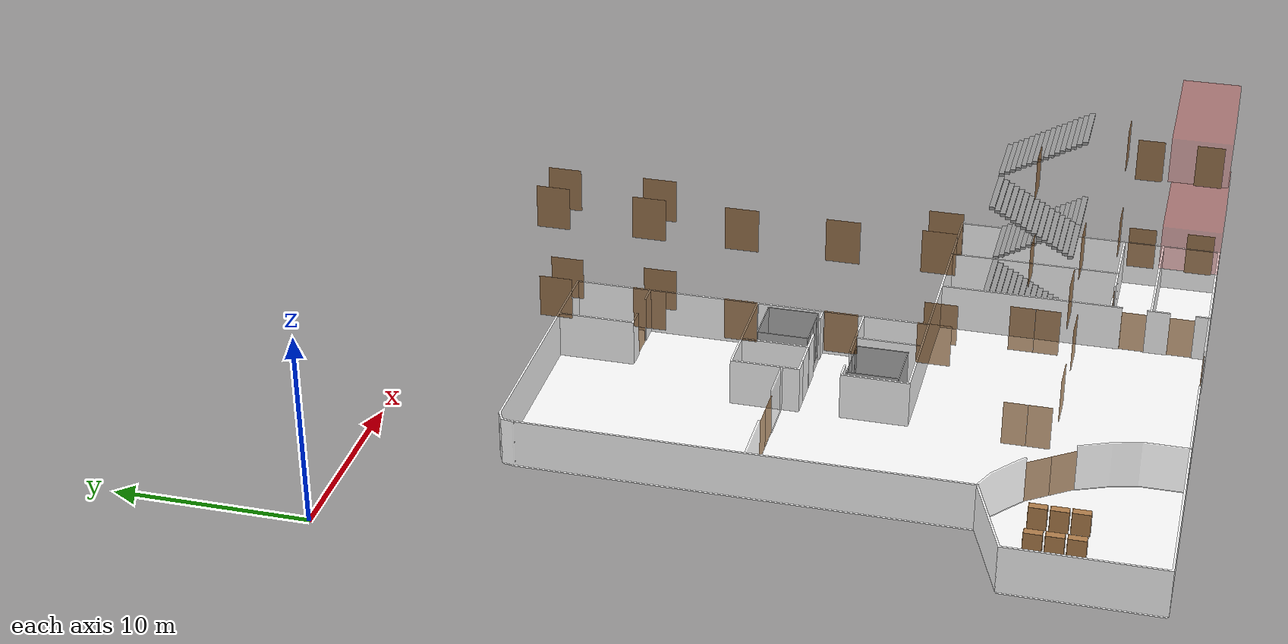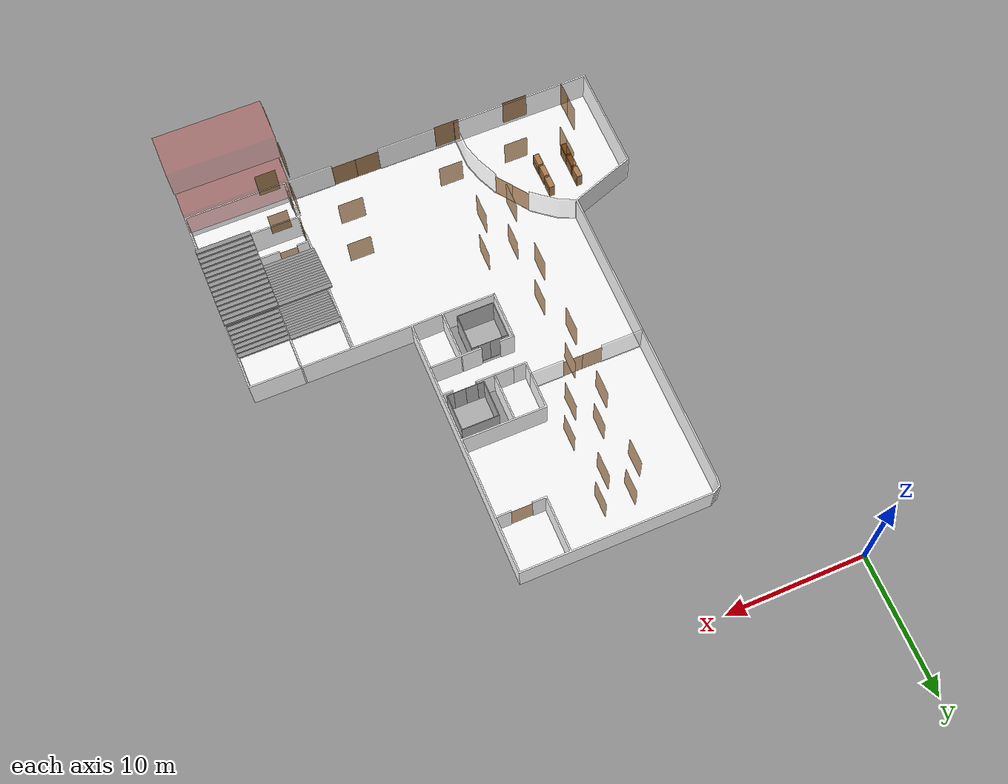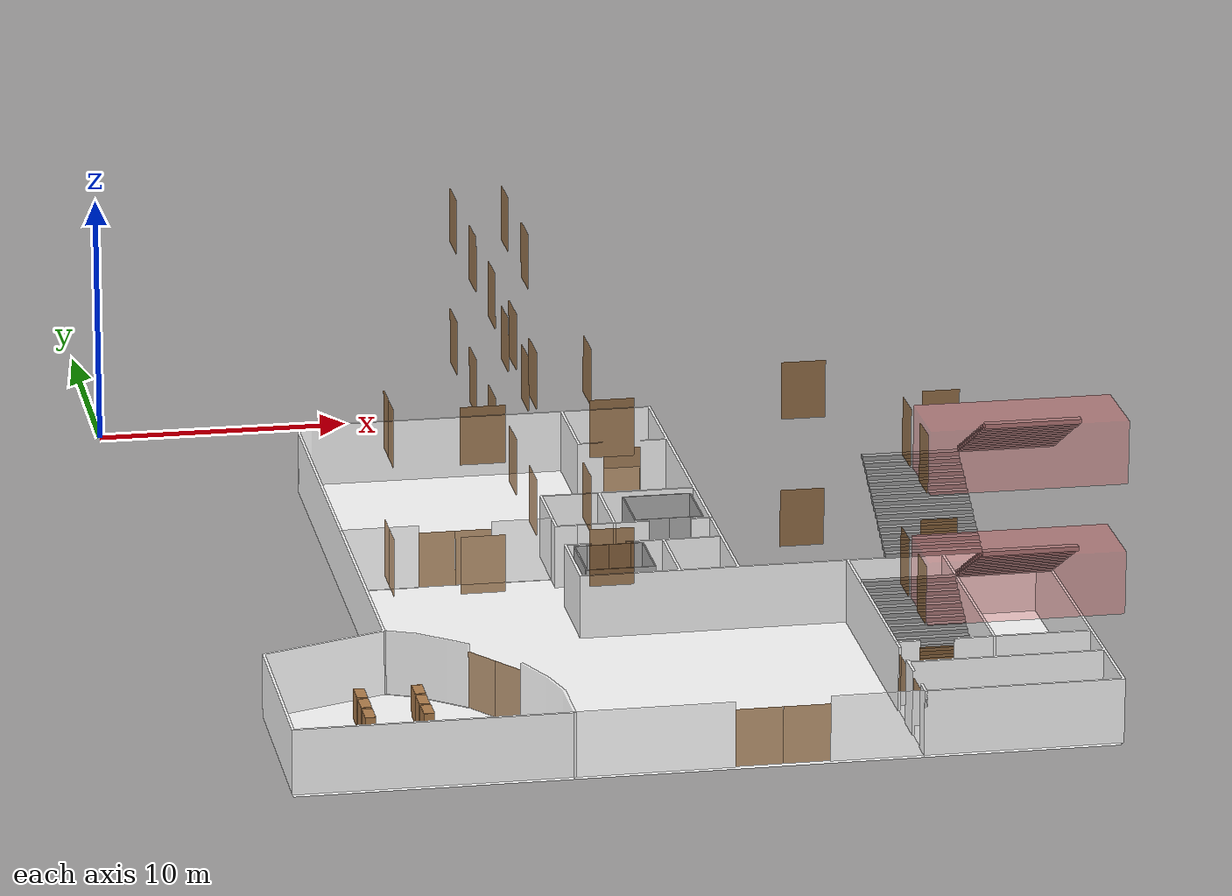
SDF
<sdf version="1.7">
 <world name="world">
  <physics type="ode">
   <max_step_size>0.001</max_step_size>
   <real_time_update_rate>1000</real_time_update_rate>
   <ode>
    <solver><iters>150</iters><sor>1.3</sor></solver>
    <constraints><erp>0.2</erp><cfm>0.0</cfm></constraints>
   </ode>
  </physics>
  <scene><ambient>0.8 0.8 0.8 1.0</ambient><background>0 0 0</background><grid>false</grid></scene>
  <include><uri>model://sun</uri></include>
  <include>
   <name>Bookshelf</name>
   <uri>model://Bookshelf</uri>
   <pose>7.7139641843624664 -35.508689695664955 0.0 0 0 1.5708</pose>
   <static>True</static>
  </include>
  <include>
   <name>Bookshelf_2</name>
   <uri>model://Bookshelf</uri>
   <pose>7.694500440356203 -34.4870372182536 0.0 0 0 1.5708</pose>
   <static>True</static>
  </include>
  <include>
   <name>Bookshelf_3</name>
   <uri>model://Bookshelf</uri>
   <pose>7.704204586228271 -33.44592099683598 0.0 0 0 1.5708</pose>
   <static>True</static>
  </include>
  <include>
   <name>Bookshelf_4</name>
   <uri>model://Bookshelf</uri>
   <pose>5.544117167367978 -35.54761718367748 0.0 0 0 1.5708</pose>
   <static>True</static>
  </include>
  <include>
   <name>Bookshelf_5</name>
   <uri>model://Bookshelf</uri>
   <pose>5.544117167367978 -34.51620510813193 0.0 0 0 1.5708</pose>
   <static>True</static>
  </include>
  <include>
   <name>Bookshelf_6</name>
   <uri>model://Bookshelf</uri>
   <pose>5.544117167367978 -33.484848484848506 0.0 0 0 1.5708</pose>
   <static>True</static>
  </include>
  <model name="L1_door1">
   <pose>10.709634015069973 -33.66240662817629 0.0 0 0 2.1908053757712316</pose>
   <link name="right">
    <pose>0.7171762283854256 0 1.11 0 0 0</pose>
    <visual name="right_visual">
     <geometry><box><size>1.4243524567708512 0.03 2.2</size></box></geometry>
     <material><ambient>0.5 0.25 0 0.6</ambient><diffuse>0.5 0.25 0 0.6</diffuse></material>
    </visual>
    <collision name="right_collision">
     <geometry><box><size>1.4243524567708512 0.03 2.2</size></box></geometry>
     <surface><contact><collide_bitmask>0x02</collide_bitmask></contact></surface>
    </collision>
    <inertial>
     <mass>50.0</mass>
     <inertia><ixx>20.17041666666667</ixx><iyy>28.619916337954837</iyy><izz>8.456999671288166</izz></inertia>
    </inertial>
   </link>
   <joint name="right_joint" type="revolute">
    <parent>world</parent>
    <child>right</child>
    <axis><xyz>0 0 1</xyz><limit><lower>0</lower><upper>1.57</upper></limit></axis>
    <pose>0.7171762283854256 0 0 0 0 0</pose>
   </joint>
   <link name="left">
    <pose>-0.7171762283854256 0 1.11 0 0 0</pose>
    <visual name="left_visual">
     <geometry><box><size>1.4243524567708512 0.03 2.2</size></box></geometry>
     <material><ambient>0.5 0.25 0 0.6</ambient><diffuse>0.5 0.25 0 0.6</diffuse></material>
    </visual>
    <collision name="left_collision">
     <geometry><box><size>1.4243524567708512 0.03 2.2</size></box></geometry>
     <surface><contact><collide_bitmask>0x02</collide_bitmask></contact></surface>
    </collision>
    <inertial>
     <mass>50.0</mass>
     <inertia><ixx>20.17041666666667</ixx><iyy>28.619916337954837</iyy><izz>8.456999671288166</izz></inertia>
    </inertial>
   </link>
   <joint name="left_joint" type="revolute">
    <parent>world</parent>
    <child>left</child>
    <axis><xyz>0 0 1</xyz><limit><lower>-1.57</lower><upper>0</upper></limit></axis>
    <pose>-0.7171762283854256 0 0 0 0 0</pose>
   </joint>
   <plugin name="double_hinged_door" filename="libdouble_hinged_door_plugin.so">
    <ros><namespace>/doors/L1_door1</namespace></ros>
    <right_joint>right_joint</right_joint>
    <left_joint>left_joint</left_joint>
    <open_angle>1.57</open_angle>
    <kp>150.0</kp>
    <kd>80.0</kd>
   </plugin>
  </model>
  <model name="L1_door2">
   <pose>11.467915973513396 -19.51919626838896 0.0 0 0 3.141592653589793</pose>
   <link name="right">
    <pose>0.7343820334670719 0 1.11 0 0 0</pose>
    <visual name="right_visual">
     <geometry><box><size>1.4587640669341437 0.03 2.2</size></box></geometry>
     <material><ambient>0.5 0.25 0 0.6</ambient><diffuse>0.5 0.25 0 0.6</diffuse></material>
    </visual>
    <collision name="right_collision">
     <geometry><box><size>1.4587640669341437 0.03 2.2</size></box></geometry>
     <surface><contact><collide_bitmask>0x02</collide_bitmask></contact></surface>
    </collision>
    <inertial>
     <mass>50.0</mass>
     <inertia><ixx>20.17041666666667</ixx><iyy>29.033302512409353</iyy><izz>8.87038584574268</izz></inertia>
    </inertial>
   </link>
   <joint name="right_joint" type="prismatic">
    <parent>world</parent>
    <child>right</child>
    <axis>
     <xyz>1 0 0</xyz>
     <limit><lower>0.0</lower><upper>1.4687640669341437</upper><effort>500.0</effort></limit>
    </axis>
   </joint>
   <link name="left">
    <pose>-0.7343820334670719 0 1.11 0 0 0</pose>
    <visual name="left_visual">
     <geometry><box><size>1.4587640669341437 0.03 2.2</size></box></geometry>
     <material><ambient>0.5 0.25 0 0.6</ambient><diffuse>0.5 0.25 0 0.6</diffuse></material>
    </visual>
    <collision name="left_collision">
     <geometry><box><size>1.4587640669341437 0.03 2.2</size></box></geometry>
     <surface><contact><collide_bitmask>0x02</collide_bitmask></contact></surface>
    </collision>
    <inertial>
     <mass>50.0</mass>
     <inertia><ixx>20.17041666666667</ixx><iyy>29.033302512409353</iyy><izz>8.87038584574268</izz></inertia>
    </inertial>
   </link>
   <joint name="left_joint" type="prismatic">
    <parent>world</parent>
    <child>left</child>
    <axis>
     <xyz>1 0 0</xyz>
     <limit><lower>-1.4687640669341437</lower><upper>0.0</upper><effort>500.0</effort></limit>
    </axis>
   </joint>
   <plugin name="double_sliding_door" filename="libdouble_sliding_door_plugin.so">
    <ros><namespace>/doors/L1_door2</namespace></ros>
    <right_joint>right_joint</right_joint>
    <left_joint>left_joint</left_joint>
    <open_distance>1.3</open_distance>
    <kp>100.0</kp>
    <kd>120.0</kd>
   </plugin>
  </model>
  <model name="L1_door3">
   <pose>20.250916593273978 -40.03653325504781 0.0 0 0 3.141592653589793</pose>
   <link name="right">
    <pose>0.9032757608376549 0 1.11 0 0 0</pose>
    <visual name="right_visual">
     <geometry><box><size>1.7965515216753098 0.03 2.2</size></box></geometry>
     <material><ambient>0.5 0.25 0 0.6</ambient><diffuse>0.5 0.25 0 0.6</diffuse></material>
    </visual>
    <collision name="right_collision">
     <geometry><box><size>1.7965515216753098 0.03 2.2</size></box></geometry>
     <surface><contact><collide_bitmask>0x02</collide_bitmask></contact></surface>
    </collision>
    <inertial>
     <mass>50.0</mass>
     <inertia><ixx>20.17041666666667</ixx><iyy>33.61498904180781</iyy><izz>13.452072375141132</izz></inertia>
    </inertial>
   </link>
   <joint name="right_joint" type="prismatic">
    <parent>world</parent>
    <child>right</child>
    <axis>
     <xyz>1 0 0</xyz>
     <limit><lower>0.0</lower><upper>1.8065515216753099</upper><effort>500.0</effort></limit>
    </axis>
   </joint>
   <link name="left">
    <pose>-0.9032757608376549 0 1.11 0 0 0</pose>
    <visual name="left_visual">
     <geometry><box><size>1.7965515216753098 0.03 2.2</size></box></geometry>
     <material><ambient>0.5 0.25 0 0.6</ambient><diffuse>0.5 0.25 0 0.6</diffuse></material>
    </visual>
    <collision name="left_collision">
     <geometry><box><size>1.7965515216753098 0.03 2.2</size></box></geometry>
     <surface><contact><collide_bitmask>0x02</collide_bitmask></contact></surface>
    </collision>
    <inertial>
     <mass>50.0</mass>
     <inertia><ixx>20.17041666666667</ixx><iyy>33.61498904180781</iyy><izz>13.452072375141132</izz></inertia>
    </inertial>
   </link>
   <joint name="left_joint" type="prismatic">
    <parent>world</parent>
    <child>left</child>
    <axis>
     <xyz>1 0 0</xyz>
     <limit><lower>-1.8065515216753099</lower><upper>0.0</upper><effort>500.0</effort></limit>
    </axis>
   </joint>
   <plugin name="double_sliding_door" filename="libdouble_sliding_door_plugin.so">
    <ros><namespace>/doors/L1_door3</namespace></ros>
    <right_joint>right_joint</right_joint>
    <left_joint>left_joint</left_joint>
    <open_distance>1.3</open_distance>
    <kp>100.0</kp>
    <kd>120.0</kd>
   </plugin>
  </model>
  <model name="L1_door4">
   <pose>19.469095149558022 -11.090452425220999 0.0 0 0 0.0</pose>
   <link name="right">
    <pose>0 0 1.11 0 0 0</pose>
    <visual name="right_visual">
     <geometry><box><size>1.5839752748148876 0.03 2.2</size></box></geometry>
     <material><ambient>0.5 0.25 0 0.6</ambient><diffuse>0.5 0.25 0 0.6</diffuse></material>
    </visual>
    <collision name="right_collision">
     <geometry><box><size>1.5839752748148876 0.03 2.2</size></box></geometry>
     <surface><contact><collide_bitmask>0x02</collide_bitmask></contact></surface>
    </collision>
    <inertial>
     <mass>50.0</mass>
     <inertia><ixx>20.17041666666667</ixx><iyy>30.620740296770418</iyy><izz>10.457823630103746</izz></inertia>
    </inertial>
   </link>
   <joint name="right_joint" type="revolute">
    <parent>world</parent>
    <child>right</child>
    <axis><xyz>0 0 1</xyz><limit><lower>0</lower><upper>1.57</upper></limit></axis>
    <pose>0.7969876374074438 0 0 0 0 0</pose>
   </joint>
   <plugin name="single_hinged_door" filename="libsingle_hinged_door_plugin.so">
    <ros><namespace>/doors/L1_door4</namespace></ros>
    <right_joint>right_joint</right_joint>
    <open_angle>1.57</open_angle>
    <kp>150.0</kp>
    <kd>80.0</kd>
   </plugin>
  </model>
  <model name="L1_door_stair2">
   <pose>27.032977786476188 -34.93492513944615 0.0 0 0 3.141592653589793</pose>
   <link name="right">
    <pose>0 0 1.11 0 0 0</pose>
    <visual name="right_visual">
     <geometry><box><size>1.3763065531526253 0.03 2.2</size></box></geometry>
     <material><ambient>0.5 0.25 0 0.6</ambient><diffuse>0.5 0.25 0 0.6</diffuse></material>
    </visual>
    <collision name="right_collision">
     <geometry><box><size>1.3763065531526253 0.03 2.2</size></box></geometry>
     <surface><contact><collide_bitmask>0x02</collide_bitmask></contact></surface>
    </collision>
    <inertial>
     <mass>50.0</mass>
     <inertia><ixx>20.17041666666667</ixx><iyy>28.059248867711922</iyy><izz>7.896332201045251</izz></inertia>
    </inertial>
   </link>
   <joint name="right_joint" type="revolute">
    <parent>world</parent>
    <child>right</child>
    <axis><xyz>0 0 1</xyz><limit><lower>0</lower><upper>1.57</upper></limit></axis>
    <pose>0.6931532765763126 0 0 0 0 0</pose>
   </joint>
   <plugin name="single_hinged_door" filename="libsingle_hinged_door_plugin.so">
    <ros><namespace>/doors/L1_door_stair2</namespace></ros>
    <right_joint>right_joint</right_joint>
    <open_angle>1.57</open_angle>
    <kp>150.0</kp>
    <kd>80.0</kd>
   </plugin>
  </model>
  <model name="L1_door_toilet">
   <pose>25.5080405780083 -38.67795283295823 0.0 0 0 1.5707963267948966</pose>
   <link name="right">
    <pose>0 0 1.11 0 0 0</pose>
    <visual name="right_visual">
     <geometry><box><size>1.3763065531526217 0.03 2.2</size></box></geometry>
     <material><ambient>0.5 0.25 0 0.6</ambient><diffuse>0.5 0.25 0 0.6</diffuse></material>
    </visual>
    <collision name="right_collision">
     <geometry><box><size>1.3763065531526217 0.03 2.2</size></box></geometry>
     <surface><contact><collide_bitmask>0x02</collide_bitmask></contact></surface>
    </collision>
    <inertial>
     <mass>50.0</mass>
     <inertia><ixx>20.17041666666667</ixx><iyy>28.059248867711883</iyy><izz>7.89633220104521</izz></inertia>
    </inertial>
   </link>
   <joint name="right_joint" type="revolute">
    <parent>world</parent>
    <child>right</child>
    <axis><xyz>0 0 1</xyz><limit><lower>0</lower><upper>1.57</upper></limit></axis>
    <pose>0.6931532765763109 0 0 0 0 0</pose>
   </joint>
   <plugin name="single_hinged_door" filename="libsingle_hinged_door_plugin.so">
    <ros><namespace>/doors/L1_door_toilet</namespace></ros>
    <right_joint>right_joint</right_joint>
    <open_angle>1.57</open_angle>
    <kp>150.0</kp>
    <kd>80.0</kd>
   </plugin>
  </model>
  <model name="L1_door_stair1">
   <pose>25.5080405780083 -36.18260103728351 0.0 0 0 -1.5707963267948966</pose>
   <link name="right">
    <pose>0 0 1.11 0 0 0</pose>
    <visual name="right_visual">
     <geometry><box><size>1.3763065531526217 0.03 2.2</size></box></geometry>
     <material><ambient>0.5 0.25 0 0.6</ambient><diffuse>0.5 0.25 0 0.6</diffuse></material>
    </visual>
    <collision name="right_collision">
     <geometry><box><size>1.3763065531526217 0.03 2.2</size></box></geometry>
     <surface><contact><collide_bitmask>0x02</collide_bitmask></contact></surface>
    </collision>
    <inertial>
     <mass>50.0</mass>
     <inertia><ixx>20.17041666666667</ixx><iyy>28.059248867711883</iyy><izz>7.89633220104521</izz></inertia>
    </inertial>
   </link>
   <joint name="right_joint" type="revolute">
    <parent>world</parent>
    <child>right</child>
    <axis><xyz>0 0 -1</xyz><limit><lower>0</lower><upper>1.57</upper></limit></axis>
    <pose>0.6931532765763109 0 0 0 0 0</pose>
   </joint>
   <plugin name="single_hinged_door" filename="libsingle_hinged_door_plugin.so">
    <ros><namespace>/doors/L1_door_stair1</namespace></ros>
    <right_joint>right_joint</right_joint>
    <open_angle>1.57</open_angle>
    <kp>150.0</kp>
    <kd>80.0</kd>
   </plugin>
  </model>
  <include><name>hotel_L1</name><uri>model://hotel_L1</uri></include>
  <include>
   <uri>file:///home/home/ros2_ws/src/RCI_quadruped_robot_navigation/rl_sar/models/restricted_zone</uri>
   <name>L2_restricted_zone</name>
   <pose>29.18 -38.66 6.25 0 0 0</pose>
  </include>
  <model name="L2_door10">
   <pose>6.967646280829374 -32.68448629721379 5.0 0 0 1.5705221665011055</pose>
   <link name="right">
    <pose>0.5645263305892074 0 1.11 0 0 0</pose>
    <visual name="right_visual">
     <geometry><box><size>1.1190526611784148 0.03 2.2</size></box></geometry>
     <material><ambient>0.5 0.25 0 0.6</ambient><diffuse>0.5 0.25 0 0.6</diffuse></material>
    </visual>
    <collision name="right_collision">
     <geometry><box><size>1.1190526611784148 0.03 2.2</size></box></geometry>
     <surface><contact><collide_bitmask>0x02</collide_bitmask></contact></surface>
    </collision>
    <inertial>
     <mass>50.0</mass>
     <inertia><ixx>20.17041666666667</ixx><iyy>25.38449524371039</iyy><izz>5.221578577043717</izz></inertia>
    </inertial>
   </link>
   <joint name="right_joint" type="revolute">
    <parent>world</parent>
    <child>right</child>
    <axis><xyz>0 0 -1</xyz><limit><lower>0</lower><upper>1.57</upper></limit></axis>
    <pose>0.5645263305892074 0 0 0 0 0</pose>
   </joint>
   <link name="left">
    <pose>-0.5645263305892074 0 1.11 0 0 0</pose>
    <visual name="left_visual">
     <geometry><box><size>1.1190526611784148 0.03 2.2</size></box></geometry>
     <material><ambient>0.5 0.25 0 0.6</ambient><diffuse>0.5 0.25 0 0.6</diffuse></material>
    </visual>
    <collision name="left_collision">
     <geometry><box><size>1.1190526611784148 0.03 2.2</size></box></geometry>
     <surface><contact><collide_bitmask>0x02</collide_bitmask></contact></surface>
    </collision>
    <inertial>
     <mass>50.0</mass>
     <inertia><ixx>20.17041666666667</ixx><iyy>25.38449524371039</iyy><izz>5.221578577043717</izz></inertia>
    </inertial>
   </link>
   <joint name="left_joint" type="revolute">
    <parent>world</parent>
    <child>left</child>
    <axis><xyz>0 0 -1</xyz><limit><lower>-1.57</lower><upper>0</upper></limit></axis>
    <pose>-0.5645263305892074 0 0 0 0 0</pose>
   </joint>
   <plugin name="double_hinged_door" filename="libdouble_hinged_door_plugin.so">
    <ros><namespace>/doors/L2_door10</namespace></ros>
    <right_joint>right_joint</right_joint>
    <left_joint>left_joint</left_joint>
    <open_angle>1.57</open_angle>
    <kp>150.0</kp>
    <kd>80.0</kd>
   </plugin>
  </model>
  <model name="L2_door5">
   <pose>13.186126390963905 -17.835334843838613 5.0 0 0 1.5705221665011058</pose>
   <link name="right">
    <pose>0 0 1.11 0 0 0</pose>
    <visual name="right_visual">
     <geometry><box><size>1.6545737934173317 0.03 2.2</size></box></geometry>
     <material><ambient>0.5 0.25 0 0.6</ambient><diffuse>0.5 0.25 0 0.6</diffuse></material>
    </visual>
    <collision name="right_collision">
     <geometry><box><size>1.6545737934173317 0.03 2.2</size></box></geometry>
     <surface><contact><collide_bitmask>0x02</collide_bitmask></contact></surface>
    </collision>
    <inertial>
     <mass>50.0</mass>
     <inertia><ixx>20.17041666666667</ixx><iyy>31.573393491097583</iyy><izz>11.410476824430914</izz></inertia>
    </inertial>
   </link>
   <joint name="right_joint" type="revolute">
    <parent>world</parent>
    <child>right</child>
    <axis><xyz>0 0 -1</xyz><limit><lower>0</lower><upper>1.57</upper></limit></axis>
    <pose>0.8322868967086658 0 0 0 0 0</pose>
   </joint>
   <plugin name="single_hinged_door" filename="libsingle_hinged_door_plugin.so">
    <ros><namespace>/doors/L2_door5</namespace></ros>
    <right_joint>right_joint</right_joint>
    <open_angle>1.57</open_angle>
    <kp>150.0</kp>
    <kd>80.0</kd>
   </plugin>
  </model>
  <model name="L2_door1">
   <pose>13.188712431159534 -8.402750368968526 5.0 0 0 1.5705221665011047</pose>
   <link name="right">
    <pose>0 0 1.11 0 0 0</pose>
    <visual name="right_visual">
     <geometry><box><size>1.6545737934173281 0.03 2.2</size></box></geometry>
     <material><ambient>0.5 0.25 0 0.6</ambient><diffuse>0.5 0.25 0 0.6</diffuse></material>
    </visual>
    <collision name="right_collision">
     <geometry><box><size>1.6545737934173281 0.03 2.2</size></box></geometry>
     <surface><contact><collide_bitmask>0x02</collide_bitmask></contact></surface>
    </collision>
    <inertial>
     <mass>50.0</mass>
     <inertia><ixx>20.17041666666667</ixx><iyy>31.573393491097537</iyy><izz>11.410476824430864</izz></inertia>
    </inertial>
   </link>
   <joint name="right_joint" type="revolute">
    <parent>world</parent>
    <child>right</child>
    <axis><xyz>0 0 -1</xyz><limit><lower>0</lower><upper>1.57</upper></limit></axis>
    <pose>0.8322868967086641 0 0 0 0 0</pose>
   </joint>
   <plugin name="single_hinged_door" filename="libsingle_hinged_door_plugin.so">
    <ros><namespace>/doors/L2_door1</namespace></ros>
    <right_joint>right_joint</right_joint>
    <open_angle>1.57</open_angle>
    <kp>150.0</kp>
    <kd>80.0</kd>
   </plugin>
  </model>
  <model name="L2_door8">
   <pose>15.236484194825934 -27.379453744808572 5.0 0 0 1.5705221665011058</pose>
   <link name="right">
    <pose>0 0 1.11 0 0 0</pose>
    <visual name="right_visual">
     <geometry><box><size>1.6545737934173281 0.03 2.2</size></box></geometry>
     <material><ambient>0.5 0.25 0 0.6</ambient><diffuse>0.5 0.25 0 0.6</diffuse></material>
    </visual>
    <collision name="right_collision">
     <geometry><box><size>1.6545737934173281 0.03 2.2</size></box></geometry>
     <surface><contact><collide_bitmask>0x02</collide_bitmask></contact></surface>
    </collision>
    <inertial>
     <mass>50.0</mass>
     <inertia><ixx>20.17041666666667</ixx><iyy>31.573393491097537</iyy><izz>11.410476824430864</izz></inertia>
    </inertial>
   </link>
   <joint name="right_joint" type="revolute">
    <parent>world</parent>
    <child>right</child>
    <axis><xyz>0 0 1</xyz><limit><lower>0</lower><upper>1.57</upper></limit></axis>
    <pose>0.8322868967086641 0 0 0 0 0</pose>
   </joint>
   <plugin name="single_hinged_door" filename="libsingle_hinged_door_plugin.so">
    <ros><namespace>/doors/L2_door8</namespace></ros>
    <right_joint>right_joint</right_joint>
    <open_angle>1.57</open_angle>
    <kp>150.0</kp>
    <kd>80.0</kd>
   </plugin>
  </model>
  <model name="L2_door9">
   <pose>22.726107627620856 -30.877112199768717 5.0 0 0 3.1413184932960023</pose>
   <link name="right">
    <pose>0 0 1.11 0 0 0</pose>
    <visual name="right_visual">
     <geometry><box><size>1.6545737934173281 0.03 2.2</size></box></geometry>
     <material><ambient>0.5 0.25 0 0.6</ambient><diffuse>0.5 0.25 0 0.6</diffuse></material>
    </visual>
    <collision name="right_collision">
     <geometry><box><size>1.6545737934173281 0.03 2.2</size></box></geometry>
     <surface><contact><collide_bitmask>0x02</collide_bitmask></contact></surface>
    </collision>
    <inertial>
     <mass>50.0</mass>
     <inertia><ixx>20.17041666666667</ixx><iyy>31.573393491097537</iyy><izz>11.410476824430864</izz></inertia>
    </inertial>
   </link>
   <joint name="right_joint" type="revolute">
    <parent>world</parent>
    <child>right</child>
    <axis><xyz>0 0 1</xyz><limit><lower>0</lower><upper>1.57</upper></limit></axis>
    <pose>0.8322868967086641 0 0 0 0 0</pose>
   </joint>
   <plugin name="single_hinged_door" filename="libsingle_hinged_door_plugin.so">
    <ros><namespace>/doors/L2_door9</namespace></ros>
    <right_joint>right_joint</right_joint>
    <open_angle>1.57</open_angle>
    <kp>150.0</kp>
    <kd>80.0</kd>
   </plugin>
  </model>
  <model name="L2_door3">
   <pose>13.187388987059418 -13.230014188460865 5.0 0 0 1.5705221665011058</pose>
   <link name="right">
    <pose>0 0 1.11 0 0 0</pose>
    <visual name="right_visual">
     <geometry><box><size>1.6545737934173281 0.03 2.2</size></box></geometry>
     <material><ambient>0.5 0.25 0 0.6</ambient><diffuse>0.5 0.25 0 0.6</diffuse></material>
    </visual>
    <collision name="right_collision">
     <geometry><box><size>1.6545737934173281 0.03 2.2</size></box></geometry>
     <surface><contact><collide_bitmask>0x02</collide_bitmask></contact></surface>
    </collision>
    <inertial>
     <mass>50.0</mass>
     <inertia><ixx>20.17041666666667</ixx><iyy>31.573393491097537</iyy><izz>11.410476824430864</izz></inertia>
    </inertial>
   </link>
   <joint name="right_joint" type="revolute">
    <parent>world</parent>
    <child>right</child>
    <axis><xyz>0 0 -1</xyz><limit><lower>0</lower><upper>1.57</upper></limit></axis>
    <pose>0.8322868967086641 0 0 0 0 0</pose>
   </joint>
   <plugin name="single_hinged_door" filename="libsingle_hinged_door_plugin.so">
    <ros><namespace>/doors/L2_door3</namespace></ros>
    <right_joint>right_joint</right_joint>
    <open_angle>1.57</open_angle>
    <kp>150.0</kp>
    <kd>80.0</kd>
   </plugin>
  </model>
  <model name="L2_door6">
   <pose>13.184757310860334 -22.829056036416894 5.0 0 0 1.5705221665011069</pose>
   <link name="right">
    <pose>0 0 1.11 0 0 0</pose>
    <visual name="right_visual">
     <geometry><box><size>1.6545737934173281 0.03 2.2</size></box></geometry>
     <material><ambient>0.5 0.25 0 0.6</ambient><diffuse>0.5 0.25 0 0.6</diffuse></material>
    </visual>
    <collision name="right_collision">
     <geometry><box><size>1.6545737934173281 0.03 2.2</size></box></geometry>
     <surface><contact><collide_bitmask>0x02</collide_bitmask></contact></surface>
    </collision>
    <inertial>
     <mass>50.0</mass>
     <inertia><ixx>20.17041666666667</ixx><iyy>31.573393491097537</iyy><izz>11.410476824430864</izz></inertia>
    </inertial>
   </link>
   <joint name="right_joint" type="revolute">
    <parent>world</parent>
    <child>right</child>
    <axis><xyz>0 0 -1</xyz><limit><lower>0</lower><upper>1.57</upper></limit></axis>
    <pose>0.8322868967086641 0 0 0 0 0</pose>
   </joint>
   <plugin name="single_hinged_door" filename="libsingle_hinged_door_plugin.so">
    <ros><namespace>/doors/L2_door6</namespace></ros>
    <right_joint>right_joint</right_joint>
    <open_angle>1.57</open_angle>
    <kp>150.0</kp>
    <kd>80.0</kd>
   </plugin>
  </model>
  <model name="L2_door7">
   <pose>13.183509926765973 -27.378890900765995 5.0 0 0 1.5705221665011058</pose>
   <link name="right">
    <pose>0 0 1.11 0 0 0</pose>
    <visual name="right_visual">
     <geometry><box><size>1.6545737934173281 0.03 2.2</size></box></geometry>
     <material><ambient>0.5 0.25 0 0.6</ambient><diffuse>0.5 0.25 0 0.6</diffuse></material>
    </visual>
    <collision name="right_collision">
     <geometry><box><size>1.6545737934173281 0.03 2.2</size></box></geometry>
     <surface><contact><collide_bitmask>0x02</collide_bitmask></contact></surface>
    </collision>
    <inertial>
     <mass>50.0</mass>
     <inertia><ixx>20.17041666666667</ixx><iyy>31.573393491097537</iyy><izz>11.410476824430864</izz></inertia>
    </inertial>
   </link>
   <joint name="right_joint" type="revolute">
    <parent>world</parent>
    <child>right</child>
    <axis><xyz>0 0 -1</xyz><limit><lower>0</lower><upper>1.57</upper></limit></axis>
    <pose>0.8322868967086641 0 0 0 0 0</pose>
   </joint>
   <plugin name="single_hinged_door" filename="libsingle_hinged_door_plugin.so">
    <ros><namespace>/doors/L2_door7</namespace></ros>
    <right_joint>right_joint</right_joint>
    <open_angle>1.57</open_angle>
    <kp>150.0</kp>
    <kd>80.0</kd>
   </plugin>
  </model>
  <model name="L2_door11">
   <pose>10.240967986111862 -33.92540800608541 5.0 0 0 3.1413184932960045</pose>
   <link name="right">
    <pose>0 0 1.11 0 0 0</pose>
    <visual name="right_visual">
     <geometry><box><size>1.6545737934173281 0.03 2.2</size></box></geometry>
     <material><ambient>0.5 0.25 0 0.6</ambient><diffuse>0.5 0.25 0 0.6</diffuse></material>
    </visual>
    <collision name="right_collision">
     <geometry><box><size>1.6545737934173281 0.03 2.2</size></box></geometry>
     <surface><contact><collide_bitmask>0x02</collide_bitmask></contact></surface>
    </collision>
    <inertial>
     <mass>50.0</mass>
     <inertia><ixx>20.17041666666667</ixx><iyy>31.573393491097537</iyy><izz>11.410476824430864</izz></inertia>
    </inertial>
   </link>
   <joint name="right_joint" type="revolute">
    <parent>world</parent>
    <child>right</child>
    <axis><xyz>0 0 -1</xyz><limit><lower>0</lower><upper>1.57</upper></limit></axis>
    <pose>0.8322868967086641 0 0 0 0 0</pose>
   </joint>
   <plugin name="single_hinged_door" filename="libsingle_hinged_door_plugin.so">
    <ros><namespace>/doors/L2_door11</namespace></ros>
    <right_joint>right_joint</right_joint>
    <open_angle>1.57</open_angle>
    <kp>150.0</kp>
    <kd>80.0</kd>
   </plugin>
  </model>
  <model name="L2_door12">
   <pose>15.012746014575553 -33.92671623818438 5.0 0 0 3.1413184932960045</pose>
   <link name="right">
    <pose>0 0 1.11 0 0 0</pose>
    <visual name="right_visual">
     <geometry><box><size>1.6545737934173281 0.03 2.2</size></box></geometry>
     <material><ambient>0.5 0.25 0 0.6</ambient><diffuse>0.5 0.25 0 0.6</diffuse></material>
    </visual>
    <collision name="right_collision">
     <geometry><box><size>1.6545737934173281 0.03 2.2</size></box></geometry>
     <surface><contact><collide_bitmask>0x02</collide_bitmask></contact></surface>
    </collision>
    <inertial>
     <mass>50.0</mass>
     <inertia><ixx>20.17041666666667</ixx><iyy>31.573393491097537</iyy><izz>11.410476824430864</izz></inertia>
    </inertial>
   </link>
   <joint name="right_joint" type="revolute">
    <parent>world</parent>
    <child>right</child>
    <axis><xyz>0 0 -1</xyz><limit><lower>0</lower><upper>1.57</upper></limit></axis>
    <pose>0.8322868967086641 0 0 0 0 0</pose>
   </joint>
   <plugin name="single_hinged_door" filename="libsingle_hinged_door_plugin.so">
    <ros><namespace>/doors/L2_door12</namespace></ros>
    <right_joint>right_joint</right_joint>
    <open_angle>1.57</open_angle>
    <kp>150.0</kp>
    <kd>80.0</kd>
   </plugin>
  </model>
  <model name="L2_door2">
   <pose>15.241686699219496 -8.403313213011105 5.0 0 0 1.5705221665011058</pose>
   <link name="right">
    <pose>0 0 1.11 0 0 0</pose>
    <visual name="right_visual">
     <geometry><box><size>1.654573793417329 0.03 2.2</size></box></geometry>
     <material><ambient>0.5 0.25 0 0.6</ambient><diffuse>0.5 0.25 0 0.6</diffuse></material>
    </visual>
    <collision name="right_collision">
     <geometry><box><size>1.654573793417329 0.03 2.2</size></box></geometry>
     <surface><contact><collide_bitmask>0x02</collide_bitmask></contact></surface>
    </collision>
    <inertial>
     <mass>50.0</mass>
     <inertia><ixx>20.17041666666667</ixx><iyy>31.573393491097548</iyy><izz>11.410476824430877</izz></inertia>
    </inertial>
   </link>
   <joint name="right_joint" type="revolute">
    <parent>world</parent>
    <child>right</child>
    <axis><xyz>0 0 1</xyz><limit><lower>0</lower><upper>1.57</upper></limit></axis>
    <pose>0.8322868967086645 0 0 0 0 0</pose>
   </joint>
   <plugin name="single_hinged_door" filename="libsingle_hinged_door_plugin.so">
    <ros><namespace>/doors/L2_door2</namespace></ros>
    <right_joint>right_joint</right_joint>
    <open_angle>1.57</open_angle>
    <kp>150.0</kp>
    <kd>80.0</kd>
   </plugin>
  </model>
  <model name="L2_door4">
   <pose>15.240363255119378 -13.230577032503442 5.0 0 0 1.5705221665011058</pose>
   <link name="right">
    <pose>0 0 1.11 0 0 0</pose>
    <visual name="right_visual">
     <geometry><box><size>1.6545737934173281 0.03 2.2</size></box></geometry>
     <material><ambient>0.5 0.25 0 0.6</ambient><diffuse>0.5 0.25 0 0.6</diffuse></material>
    </visual>
    <collision name="right_collision">
     <geometry><box><size>1.6545737934173281 0.03 2.2</size></box></geometry>
     <surface><contact><collide_bitmask>0x02</collide_bitmask></contact></surface>
    </collision>
    <inertial>
     <mass>50.0</mass>
     <inertia><ixx>20.17041666666667</ixx><iyy>31.573393491097537</iyy><izz>11.410476824430864</izz></inertia>
    </inertial>
   </link>
   <joint name="right_joint" type="revolute">
    <parent>world</parent>
    <child>right</child>
    <axis><xyz>0 0 1</xyz><limit><lower>0</lower><upper>1.57</upper></limit></axis>
    <pose>0.8322868967086641 0 0 0 0 0</pose>
   </joint>
   <plugin name="single_hinged_door" filename="libsingle_hinged_door_plugin.so">
    <ros><namespace>/doors/L2_door4</namespace></ros>
    <right_joint>right_joint</right_joint>
    <open_angle>1.57</open_angle>
    <kp>150.0</kp>
    <kd>80.0</kd>
   </plugin>
  </model>
  <model name="L2_door_stair1">
   <pose>25.49893682694276 -36.20450873857642 5.0 0 0 -1.5710704870886905</pose>
   <link name="right">
    <pose>0 0 1.11 0 0 0</pose>
    <visual name="right_visual">
     <geometry><box><size>1.3771448278477716 0.03 2.2</size></box></geometry>
     <material><ambient>0.5 0.25 0 0.6</ambient><diffuse>0.5 0.25 0 0.6</diffuse></material>
    </visual>
    <collision name="right_collision">
     <geometry><box><size>1.3771448278477716 0.03 2.2</size></box></geometry>
     <surface><contact><collide_bitmask>0x02</collide_bitmask></contact></surface>
    </collision>
    <inertial>
     <mass>50.0</mass>
     <inertia><ixx>20.17041666666667</ixx><iyy>28.068866153616124</iyy><izz>7.905949486949452</izz></inertia>
    </inertial>
   </link>
   <joint name="right_joint" type="revolute">
    <parent>world</parent>
    <child>right</child>
    <axis><xyz>0 0 -1</xyz><limit><lower>0</lower><upper>1.57</upper></limit></axis>
    <pose>0.6935724139238858 0 0 0 0 0</pose>
   </joint>
   <plugin name="single_hinged_door" filename="libsingle_hinged_door_plugin.so">
    <ros><namespace>/doors/L2_door_stair1</namespace></ros>
    <right_joint>right_joint</right_joint>
    <open_angle>1.57</open_angle>
    <kp>150.0</kp>
    <kd>80.0</kd>
   </plugin>
  </model>
  <model name="L2_door_stair2">
   <pose>27.025138350256462 -34.9564967704635 5.0 0 0 3.141318493295999</pose>
   <link name="right">
    <pose>0 0 1.11 0 0 0</pose>
    <visual name="right_visual">
     <geometry><box><size>1.3771448278477751 0.03 2.2</size></box></geometry>
     <material><ambient>0.5 0.25 0 0.6</ambient><diffuse>0.5 0.25 0 0.6</diffuse></material>
    </visual>
    <collision name="right_collision">
     <geometry><box><size>1.3771448278477751 0.03 2.2</size></box></geometry>
     <surface><contact><collide_bitmask>0x02</collide_bitmask></contact></surface>
    </collision>
    <inertial>
     <mass>50.0</mass>
     <inertia><ixx>20.17041666666667</ixx><iyy>28.068866153616163</iyy><izz>7.905949486949493</izz></inertia>
    </inertial>
   </link>
   <joint name="right_joint" type="revolute">
    <parent>world</parent>
    <child>right</child>
    <axis><xyz>0 0 1</xyz><limit><lower>0</lower><upper>1.57</upper></limit></axis>
    <pose>0.6935724139238876 0 0 0 0 0</pose>
   </joint>
   <plugin name="single_hinged_door" filename="libsingle_hinged_door_plugin.so">
    <ros><namespace>/doors/L2_door_stair2</namespace></ros>
    <right_joint>right_joint</right_joint>
    <open_angle>1.57</open_angle>
    <kp>150.0</kp>
    <kd>80.0</kd>
   </plugin>
  </model>
  <model name="L2_door_restricted_area">
   <pose>25.49813059088177 -39.145255663094744 5.0 0 0 1.5705221665011053</pose>
   <link name="right">
    <pose>0 0 1.11 0 0 0</pose>
    <visual name="right_visual">
     <geometry><box><size>1.3771448278477787 0.03 2.2</size></box></geometry>
     <material><ambient>0.5 0.25 0 0.6</ambient><diffuse>0.5 0.25 0 0.6</diffuse></material>
    </visual>
    <collision name="right_collision">
     <geometry><box><size>1.3771448278477787 0.03 2.2</size></box></geometry>
     <surface><contact><collide_bitmask>0x02</collide_bitmask></contact></surface>
    </collision>
    <inertial>
     <mass>50.0</mass>
     <inertia><ixx>20.17041666666667</ixx><iyy>28.068866153616206</iyy><izz>7.905949486949533</izz></inertia>
    </inertial>
   </link>
   <joint name="right_joint" type="prismatic">
    <parent>world</parent>
    <child>right</child>
    <axis>
     <xyz>1 0 0</xyz>
     <limit><lower>0.0</lower><upper>1.3871448278477787</upper><effort>500.0</effort></limit>
    </axis>
   </joint>
   <plugin name="single_sliding_door" filename="libsingle_sliding_door_plugin.so">
    <ros><namespace>/doors/L2_door_restricted_area</namespace></ros>
    <right_joint>right_joint</right_joint>
    <open_distance>1.3</open_distance>
    <kp>100.0</kp>
    <kd>120.0</kd>
   </plugin>
  </model>
  <include>
   <uri>file:///home/home/ros2_ws/src/RCI_quadruped_robot_navigation/rl_sar/models/restricted_zone</uri>
   <name>L3_restricted_zone</name>
   <pose>29.18 -38.66 11.25 0 0 0</pose>
  </include>
  <model name="L3_door10">
   <pose>6.967646280829374 -32.68448629721379 10.0 0 0 1.5705221665011055</pose>
   <link name="right">
    <pose>0.5645263305892074 0 1.11 0 0 0</pose>
    <visual name="right_visual">
     <geometry><box><size>1.1190526611784148 0.03 2.2</size></box></geometry>
     <material><ambient>0.5 0.25 0 0.6</ambient><diffuse>0.5 0.25 0 0.6</diffuse></material>
    </visual>
    <collision name="right_collision">
     <geometry><box><size>1.1190526611784148 0.03 2.2</size></box></geometry>
     <surface><contact><collide_bitmask>0x02</collide_bitmask></contact></surface>
    </collision>
    <inertial>
     <mass>50.0</mass>
     <inertia><ixx>20.17041666666667</ixx><iyy>25.38449524371039</iyy><izz>5.221578577043717</izz></inertia>
    </inertial>
   </link>
   <joint name="right_joint" type="revolute">
    <parent>world</parent>
    <child>right</child>
    <axis><xyz>0 0 -1</xyz><limit><lower>0</lower><upper>1.57</upper></limit></axis>
    <pose>0.5645263305892074 0 0 0 0 0</pose>
   </joint>
   <link name="left">
    <pose>-0.5645263305892074 0 1.11 0 0 0</pose>
    <visual name="left_visual">
     <geometry><box><size>1.1190526611784148 0.03 2.2</size></box></geometry>
     <material><ambient>0.5 0.25 0 0.6</ambient><diffuse>0.5 0.25 0 0.6</diffuse></material>
    </visual>
    <collision name="left_collision">
     <geometry><box><size>1.1190526611784148 0.03 2.2</size></box></geometry>
     <surface><contact><collide_bitmask>0x02</collide_bitmask></contact></surface>
    </collision>
    <inertial>
     <mass>50.0</mass>
     <inertia><ixx>20.17041666666667</ixx><iyy>25.38449524371039</iyy><izz>5.221578577043717</izz></inertia>
    </inertial>
   </link>
   <joint name="left_joint" type="revolute">
    <parent>world</parent>
    <child>left</child>
    <axis><xyz>0 0 -1</xyz><limit><lower>-1.57</lower><upper>0</upper></limit></axis>
    <pose>-0.5645263305892074 0 0 0 0 0</pose>
   </joint>
   <plugin name="double_hinged_door" filename="libdouble_hinged_door_plugin.so">
    <ros><namespace>/doors/L3_door10</namespace></ros>
    <right_joint>right_joint</right_joint>
    <left_joint>left_joint</left_joint>
    <open_angle>1.57</open_angle>
    <kp>150.0</kp>
    <kd>80.0</kd>
   </plugin>
  </model>
  <model name="L3_door5">
   <pose>13.186126390963905 -17.835334843838613 10.0 0 0 1.5705221665011058</pose>
   <link name="right">
    <pose>0 0 1.11 0 0 0</pose>
    <visual name="right_visual">
     <geometry><box><size>1.6545737934173317 0.03 2.2</size></box></geometry>
     <material><ambient>0.5 0.25 0 0.6</ambient><diffuse>0.5 0.25 0 0.6</diffuse></material>
    </visual>
    <collision name="right_collision">
     <geometry><box><size>1.6545737934173317 0.03 2.2</size></box></geometry>
     <surface><contact><collide_bitmask>0x02</collide_bitmask></contact></surface>
    </collision>
    <inertial>
     <mass>50.0</mass>
     <inertia><ixx>20.17041666666667</ixx><iyy>31.573393491097583</iyy><izz>11.410476824430914</izz></inertia>
    </inertial>
   </link>
   <joint name="right_joint" type="revolute">
    <parent>world</parent>
    <child>right</child>
    <axis><xyz>0 0 -1</xyz><limit><lower>0</lower><upper>1.57</upper></limit></axis>
    <pose>0.8322868967086658 0 0 0 0 0</pose>
   </joint>
   <plugin name="single_hinged_door" filename="libsingle_hinged_door_plugin.so">
    <ros><namespace>/doors/L3_door5</namespace></ros>
    <right_joint>right_joint</right_joint>
    <open_angle>1.57</open_angle>
    <kp>150.0</kp>
    <kd>80.0</kd>
   </plugin>
  </model>
  <model name="L3_door1">
   <pose>13.188712431159534 -8.402750368968526 10.0 0 0 1.5705221665011047</pose>
   <link name="right">
    <pose>0 0 1.11 0 0 0</pose>
    <visual name="right_visual">
     <geometry><box><size>1.6545737934173281 0.03 2.2</size></box></geometry>
     <material><ambient>0.5 0.25 0 0.6</ambient><diffuse>0.5 0.25 0 0.6</diffuse></material>
    </visual>
    <collision name="right_collision">
     <geometry><box><size>1.6545737934173281 0.03 2.2</size></box></geometry>
     <surface><contact><collide_bitmask>0x02</collide_bitmask></contact></surface>
    </collision>
    <inertial>
     <mass>50.0</mass>
     <inertia><ixx>20.17041666666667</ixx><iyy>31.573393491097537</iyy><izz>11.410476824430864</izz></inertia>
    </inertial>
   </link>
   <joint name="right_joint" type="revolute">
    <parent>world</parent>
    <child>right</child>
    <axis><xyz>0 0 -1</xyz><limit><lower>0</lower><upper>1.57</upper></limit></axis>
    <pose>0.8322868967086641 0 0 0 0 0</pose>
   </joint>
   <plugin name="single_hinged_door" filename="libsingle_hinged_door_plugin.so">
    <ros><namespace>/doors/L3_door1</namespace></ros>
    <right_joint>right_joint</right_joint>
    <open_angle>1.57</open_angle>
    <kp>150.0</kp>
    <kd>80.0</kd>
   </plugin>
  </model>
  <model name="L3_door8">
   <pose>15.236484194825934 -27.379453744808572 10.0 0 0 1.5705221665011058</pose>
   <link name="right">
    <pose>0 0 1.11 0 0 0</pose>
    <visual name="right_visual">
     <geometry><box><size>1.6545737934173281 0.03 2.2</size></box></geometry>
     <material><ambient>0.5 0.25 0 0.6</ambient><diffuse>0.5 0.25 0 0.6</diffuse></material>
    </visual>
    <collision name="right_collision">
     <geometry><box><size>1.6545737934173281 0.03 2.2</size></box></geometry>
     <surface><contact><collide_bitmask>0x02</collide_bitmask></contact></surface>
    </collision>
    <inertial>
     <mass>50.0</mass>
     <inertia><ixx>20.17041666666667</ixx><iyy>31.573393491097537</iyy><izz>11.410476824430864</izz></inertia>
    </inertial>
   </link>
   <joint name="right_joint" type="revolute">
    <parent>world</parent>
    <child>right</child>
    <axis><xyz>0 0 1</xyz><limit><lower>0</lower><upper>1.57</upper></limit></axis>
    <pose>0.8322868967086641 0 0 0 0 0</pose>
   </joint>
   <plugin name="single_hinged_door" filename="libsingle_hinged_door_plugin.so">
    <ros><namespace>/doors/L3_door8</namespace></ros>
    <right_joint>right_joint</right_joint>
    <open_angle>1.57</open_angle>
    <kp>150.0</kp>
    <kd>80.0</kd>
   </plugin>
  </model>
  <model name="L3_door9">
   <pose>22.726107627620856 -30.877112199768717 10.0 0 0 3.1413184932960023</pose>
   <link name="right">
    <pose>0 0 1.11 0 0 0</pose>
    <visual name="right_visual">
     <geometry><box><size>1.6545737934173281 0.03 2.2</size></box></geometry>
     <material><ambient>0.5 0.25 0 0.6</ambient><diffuse>0.5 0.25 0 0.6</diffuse></material>
    </visual>
    <collision name="right_collision">
     <geometry><box><size>1.6545737934173281 0.03 2.2</size></box></geometry>
     <surface><contact><collide_bitmask>0x02</collide_bitmask></contact></surface>
    </collision>
    <inertial>
     <mass>50.0</mass>
     <inertia><ixx>20.17041666666667</ixx><iyy>31.573393491097537</iyy><izz>11.410476824430864</izz></inertia>
    </inertial>
   </link>
   <joint name="right_joint" type="revolute">
    <parent>world</parent>
    <child>right</child>
    <axis><xyz>0 0 1</xyz><limit><lower>0</lower><upper>1.57</upper></limit></axis>
    <pose>0.8322868967086641 0 0 0 0 0</pose>
   </joint>
   <plugin name="single_hinged_door" filename="libsingle_hinged_door_plugin.so">
    <ros><namespace>/doors/L3_door9</namespace></ros>
    <right_joint>right_joint</right_joint>
    <open_angle>1.57</open_angle>
    <kp>150.0</kp>
    <kd>80.0</kd>
   </plugin>
  </model>
  <model name="L3_door12">
   <pose>15.012746014575553 -33.92671623818438 10.0 0 0 3.1413184932960045</pose>
   <link name="right">
    <pose>0 0 1.11 0 0 0</pose>
    <visual name="right_visual">
     <geometry><box><size>1.6545737934173281 0.03 2.2</size></box></geometry>
     <material><ambient>0.5 0.25 0 0.6</ambient><diffuse>0.5 0.25 0 0.6</diffuse></material>
    </visual>
    <collision name="right_collision">
     <geometry><box><size>1.6545737934173281 0.03 2.2</size></box></geometry>
     <surface><contact><collide_bitmask>0x02</collide_bitmask></contact></surface>
    </collision>
    <inertial>
     <mass>50.0</mass>
     <inertia><ixx>20.17041666666667</ixx><iyy>31.573393491097537</iyy><izz>11.410476824430864</izz></inertia>
    </inertial>
   </link>
   <joint name="right_joint" type="revolute">
    <parent>world</parent>
    <child>right</child>
    <axis><xyz>0 0 -1</xyz><limit><lower>0</lower><upper>1.57</upper></limit></axis>
    <pose>0.8322868967086641 0 0 0 0 0</pose>
   </joint>
   <plugin name="single_hinged_door" filename="libsingle_hinged_door_plugin.so">
    <ros><namespace>/doors/L3_door12</namespace></ros>
    <right_joint>right_joint</right_joint>
    <open_angle>1.57</open_angle>
    <kp>150.0</kp>
    <kd>80.0</kd>
   </plugin>
  </model>
  <model name="L3_door11">
   <pose>10.240967986111862 -33.92540800608541 10.0 0 0 3.1413184932960045</pose>
   <link name="right">
    <pose>0 0 1.11 0 0 0</pose>
    <visual name="right_visual">
     <geometry><box><size>1.6545737934173281 0.03 2.2</size></box></geometry>
     <material><ambient>0.5 0.25 0 0.6</ambient><diffuse>0.5 0.25 0 0.6</diffuse></material>
    </visual>
    <collision name="right_collision">
     <geometry><box><size>1.6545737934173281 0.03 2.2</size></box></geometry>
     <surface><contact><collide_bitmask>0x02</collide_bitmask></contact></surface>
    </collision>
    <inertial>
     <mass>50.0</mass>
     <inertia><ixx>20.17041666666667</ixx><iyy>31.573393491097537</iyy><izz>11.410476824430864</izz></inertia>
    </inertial>
   </link>
   <joint name="right_joint" type="revolute">
    <parent>world</parent>
    <child>right</child>
    <axis><xyz>0 0 -1</xyz><limit><lower>0</lower><upper>1.57</upper></limit></axis>
    <pose>0.8322868967086641 0 0 0 0 0</pose>
   </joint>
   <plugin name="single_hinged_door" filename="libsingle_hinged_door_plugin.so">
    <ros><namespace>/doors/L3_door11</namespace></ros>
    <right_joint>right_joint</right_joint>
    <open_angle>1.57</open_angle>
    <kp>150.0</kp>
    <kd>80.0</kd>
   </plugin>
  </model>
  <model name="L3_door7">
   <pose>13.183509926765973 -27.378890900765995 10.0 0 0 1.5705221665011058</pose>
   <link name="right">
    <pose>0 0 1.11 0 0 0</pose>
    <visual name="right_visual">
     <geometry><box><size>1.6545737934173281 0.03 2.2</size></box></geometry>
     <material><ambient>0.5 0.25 0 0.6</ambient><diffuse>0.5 0.25 0 0.6</diffuse></material>
    </visual>
    <collision name="right_collision">
     <geometry><box><size>1.6545737934173281 0.03 2.2</size></box></geometry>
     <surface><contact><collide_bitmask>0x02</collide_bitmask></contact></surface>
    </collision>
    <inertial>
     <mass>50.0</mass>
     <inertia><ixx>20.17041666666667</ixx><iyy>31.573393491097537</iyy><izz>11.410476824430864</izz></inertia>
    </inertial>
   </link>
   <joint name="right_joint" type="revolute">
    <parent>world</parent>
    <child>right</child>
    <axis><xyz>0 0 -1</xyz><limit><lower>0</lower><upper>1.57</upper></limit></axis>
    <pose>0.8322868967086641 0 0 0 0 0</pose>
   </joint>
   <plugin name="single_hinged_door" filename="libsingle_hinged_door_plugin.so">
    <ros><namespace>/doors/L3_door7</namespace></ros>
    <right_joint>right_joint</right_joint>
    <open_angle>1.57</open_angle>
    <kp>150.0</kp>
    <kd>80.0</kd>
   </plugin>
  </model>
  <model name="L3_door6">
   <pose>13.184772522861486 -22.773570245388242 10.0 0 0 1.5705221665011058</pose>
   <link name="right">
    <pose>0 0 1.11 0 0 0</pose>
    <visual name="right_visual">
     <geometry><box><size>1.6545737934173281 0.03 2.2</size></box></geometry>
     <material><ambient>0.5 0.25 0 0.6</ambient><diffuse>0.5 0.25 0 0.6</diffuse></material>
    </visual>
    <collision name="right_collision">
     <geometry><box><size>1.6545737934173281 0.03 2.2</size></box></geometry>
     <surface><contact><collide_bitmask>0x02</collide_bitmask></contact></surface>
    </collision>
    <inertial>
     <mass>50.0</mass>
     <inertia><ixx>20.17041666666667</ixx><iyy>31.573393491097537</iyy><izz>11.410476824430864</izz></inertia>
    </inertial>
   </link>
   <joint name="right_joint" type="revolute">
    <parent>world</parent>
    <child>right</child>
    <axis><xyz>0 0 -1</xyz><limit><lower>0</lower><upper>1.57</upper></limit></axis>
    <pose>0.8322868967086641 0 0 0 0 0</pose>
   </joint>
   <plugin name="single_hinged_door" filename="libsingle_hinged_door_plugin.so">
    <ros><namespace>/doors/L3_door6</namespace></ros>
    <right_joint>right_joint</right_joint>
    <open_angle>1.57</open_angle>
    <kp>150.0</kp>
    <kd>80.0</kd>
   </plugin>
  </model>
  <model name="L3_door3">
   <pose>13.187388987059418 -13.230014188460865 10.0 0 0 1.5705221665011058</pose>
   <link name="right">
    <pose>0 0 1.11 0 0 0</pose>
    <visual name="right_visual">
     <geometry><box><size>1.6545737934173281 0.03 2.2</size></box></geometry>
     <material><ambient>0.5 0.25 0 0.6</ambient><diffuse>0.5 0.25 0 0.6</diffuse></material>
    </visual>
    <collision name="right_collision">
     <geometry><box><size>1.6545737934173281 0.03 2.2</size></box></geometry>
     <surface><contact><collide_bitmask>0x02</collide_bitmask></contact></surface>
    </collision>
    <inertial>
     <mass>50.0</mass>
     <inertia><ixx>20.17041666666667</ixx><iyy>31.573393491097537</iyy><izz>11.410476824430864</izz></inertia>
    </inertial>
   </link>
   <joint name="right_joint" type="revolute">
    <parent>world</parent>
    <child>right</child>
    <axis><xyz>0 0 -1</xyz><limit><lower>0</lower><upper>1.57</upper></limit></axis>
    <pose>0.8322868967086641 0 0 0 0 0</pose>
   </joint>
   <plugin name="single_hinged_door" filename="libsingle_hinged_door_plugin.so">
    <ros><namespace>/doors/L3_door3</namespace></ros>
    <right_joint>right_joint</right_joint>
    <open_angle>1.57</open_angle>
    <kp>150.0</kp>
    <kd>80.0</kd>
   </plugin>
  </model>
  <model name="L3_door4">
   <pose>15.240363255119378 -13.230577032503442 10.0 0 0 1.5705221665011058</pose>
   <link name="right">
    <pose>0 0 1.11 0 0 0</pose>
    <visual name="right_visual">
     <geometry><box><size>1.6545737934173281 0.03 2.2</size></box></geometry>
     <material><ambient>0.5 0.25 0 0.6</ambient><diffuse>0.5 0.25 0 0.6</diffuse></material>
    </visual>
    <collision name="right_collision">
     <geometry><box><size>1.6545737934173281 0.03 2.2</size></box></geometry>
     <surface><contact><collide_bitmask>0x02</collide_bitmask></contact></surface>
    </collision>
    <inertial>
     <mass>50.0</mass>
     <inertia><ixx>20.17041666666667</ixx><iyy>31.573393491097537</iyy><izz>11.410476824430864</izz></inertia>
    </inertial>
   </link>
   <joint name="right_joint" type="revolute">
    <parent>world</parent>
    <child>right</child>
    <axis><xyz>0 0 1</xyz><limit><lower>0</lower><upper>1.57</upper></limit></axis>
    <pose>0.8322868967086641 0 0 0 0 0</pose>
   </joint>
   <plugin name="single_hinged_door" filename="libsingle_hinged_door_plugin.so">
    <ros><namespace>/doors/L3_door4</namespace></ros>
    <right_joint>right_joint</right_joint>
    <open_angle>1.57</open_angle>
    <kp>150.0</kp>
    <kd>80.0</kd>
   </plugin>
  </model>
  <model name="L3_door_stair2">
   <pose>27.025138350256462 -34.9564967704635 10.0 0 0 3.141318493295999</pose>
   <link name="right">
    <pose>0 0 1.11 0 0 0</pose>
    <visual name="right_visual">
     <geometry><box><size>1.3771448278477751 0.03 2.2</size></box></geometry>
     <material><ambient>0.5 0.25 0 0.6</ambient><diffuse>0.5 0.25 0 0.6</diffuse></material>
    </visual>
    <collision name="right_collision">
     <geometry><box><size>1.3771448278477751 0.03 2.2</size></box></geometry>
     <surface><contact><collide_bitmask>0x02</collide_bitmask></contact></surface>
    </collision>
    <inertial>
     <mass>50.0</mass>
     <inertia><ixx>20.17041666666667</ixx><iyy>28.068866153616163</iyy><izz>7.905949486949493</izz></inertia>
    </inertial>
   </link>
   <joint name="right_joint" type="revolute">
    <parent>world</parent>
    <child>right</child>
    <axis><xyz>0 0 1</xyz><limit><lower>0</lower><upper>1.57</upper></limit></axis>
    <pose>0.6935724139238876 0 0 0 0 0</pose>
   </joint>
   <plugin name="single_hinged_door" filename="libsingle_hinged_door_plugin.so">
    <ros><namespace>/doors/L3_door_stair2</namespace></ros>
    <right_joint>right_joint</right_joint>
    <open_angle>1.57</open_angle>
    <kp>150.0</kp>
    <kd>80.0</kd>
   </plugin>
  </model>
  <model name="L3_door_stair1">
   <pose>25.49894062994305 -36.19063729081926 10.0 0 0 -1.57107048708869</pose>
   <link name="right">
    <pose>0 0 1.11 0 0 0</pose>
    <visual name="right_visual">
     <geometry><box><size>1.3494019312908105 0.03 2.2</size></box></geometry>
     <material><ambient>0.5 0.25 0 0.6</ambient><diffuse>0.5 0.25 0 0.6</diffuse></material>
    </visual>
    <collision name="right_collision">
     <geometry><box><size>1.3494019312908105 0.03 2.2</size></box></geometry>
     <surface><contact><collide_bitmask>0x02</collide_bitmask></contact></surface>
    </collision>
    <inertial>
     <mass>50.0</mass>
     <inertia><ixx>20.17041666666667</ixx><iyy>27.75368988404738</iyy><izz>7.590773217380706</izz></inertia>
    </inertial>
   </link>
   <joint name="right_joint" type="revolute">
    <parent>world</parent>
    <child>right</child>
    <axis><xyz>0 0 -1</xyz><limit><lower>0</lower><upper>1.57</upper></limit></axis>
    <pose>0.6797009656454053 0 0 0 0 0</pose>
   </joint>
   <plugin name="single_hinged_door" filename="libsingle_hinged_door_plugin.so">
    <ros><namespace>/doors/L3_door_stair1</namespace></ros>
    <right_joint>right_joint</right_joint>
    <open_angle>1.57</open_angle>
    <kp>150.0</kp>
    <kd>80.0</kd>
   </plugin>
  </model>
  <model name="L3_door_restricted_area">
   <pose>25.49813059088177 -39.145255663094744 10.0 0 0 1.5705221665011053</pose>
   <link name="right">
    <pose>0 0 1.11 0 0 0</pose>
    <visual name="right_visual">
     <geometry><box><size>1.3771448278477787 0.03 2.2</size></box></geometry>
     <material><ambient>0.5 0.25 0 0.6</ambient><diffuse>0.5 0.25 0 0.6</diffuse></material>
    </visual>
    <collision name="right_collision">
     <geometry><box><size>1.3771448278477787 0.03 2.2</size></box></geometry>
     <surface><contact><collide_bitmask>0x02</collide_bitmask></contact></surface>
    </collision>
    <inertial>
     <mass>50.0</mass>
     <inertia><ixx>20.17041666666667</ixx><iyy>28.068866153616206</iyy><izz>7.905949486949533</izz></inertia>
    </inertial>
   </link>
   <joint name="right_joint" type="prismatic">
    <parent>world</parent>
    <child>right</child>
    <axis>
     <xyz>1 0 0</xyz>
     <limit><lower>0.0</lower><upper>1.3871448278477787</upper><effort>500.0</effort></limit>
    </axis>
   </joint>
   <plugin name="single_sliding_door" filename="libsingle_sliding_door_plugin.so">
    <ros><namespace>/doors/L3_door_restricted_area</namespace></ros>
    <right_joint>right_joint</right_joint>
    <open_distance>1.3</open_distance>
    <kp>100.0</kp>
    <kd>120.0</kd>
   </plugin>
  </model>
  <model name="L3_door2">
   <pose>15.241686699219496 -8.403313213011105 10.0 0 0 1.5705221665011058</pose>
   <link name="right">
    <pose>0 0 1.11 0 0 0</pose>
    <visual name="right_visual">
     <geometry><box><size>1.654573793417329 0.03 2.2</size></box></geometry>
     <material><ambient>0.5 0.25 0 0.6</ambient><diffuse>0.5 0.25 0 0.6</diffuse></material>
    </visual>
    <collision name="right_collision">
     <geometry><box><size>1.654573793417329 0.03 2.2</size></box></geometry>
     <surface><contact><collide_bitmask>0x02</collide_bitmask></contact></surface>
    </collision>
    <inertial>
     <mass>50.0</mass>
     <inertia><ixx>20.17041666666667</ixx><iyy>31.573393491097548</iyy><izz>11.410476824430877</izz></inertia>
    </inertial>
   </link>
   <joint name="right_joint" type="revolute">
    <parent>world</parent>
    <child>right</child>
    <axis><xyz>0 0 1</xyz><limit><lower>0</lower><upper>1.57</upper></limit></axis>
    <pose>0.8322868967086645 0 0 0 0 0</pose>
   </joint>
   <plugin name="single_hinged_door" filename="libsingle_hinged_door_plugin.so">
    <ros><namespace>/doors/L3_door2</namespace></ros>
    <right_joint>right_joint</right_joint>
    <open_angle>1.57</open_angle>
    <kp>150.0</kp>
    <kd>80.0</kd>
   </plugin>
  </model>
  <model name="stairs_new">
   <pose>27.35 -34.334000 0.065 0 -0 1.570796</pose>
   <link name="Stairs">
    <pose>3 1e-06 0 0 -0 0</pose>
    <inertial>
     <mass>1</mass>
     <inertia><ixx>1</ixx><ixy>0</ixy><ixz>0</ixz><iyy>1</iyy><iyz>0</iyz><izz>1</izz></inertia>
    </inertial>
    <visual name="Stairs_Visual_7">
     <pose>0.70875 0 1.09375 0 -0 1.5708</pose>
     <geometry><box><size>3.66 0.28125 0.15625</size></box></geometry>
     <material>
      <script><uri>file://media/materials/scripts/gazebo.material</uri><name>Gazebo/Grey</name></script>
      <ambient>1 1 1 1</ambient>
      <shader type="pixel"><normal_map>__default__</normal_map></shader>
      <diffuse>0.7 0.7 0.7 1</diffuse>
      <specular>0.01 0.01 0.01 1</specular>
      <emissive>0 0 0 1</emissive>
     </material>
     <meta><layer>0</layer></meta>
    </visual>
    <visual name="Stairs_Visual_10">
     <pose>1.5525 0 1.5625 0 -0 1.5708</pose>
     <geometry><box><size>3.66 0.28125 0.15625</size></box></geometry>
     <material>
      <script><uri>file://media/materials/scripts/gazebo.material</uri><name>Gazebo/Grey</name></script>
      <ambient>1 1 1 1</ambient>
      <shader type="pixel"><normal_map>__default__</normal_map></shader>
      <diffuse>0.7 0.7 0.7 1</diffuse>
      <specular>0.01 0.01 0.01 1</specular>
      <emissive>0 0 0 1</emissive>
     </material>
     <meta><layer>0</layer></meta>
    </visual>
    <visual name="Stairs_Visual_11">
     <pose>1.83375 0 1.71875 0 -0 1.5708</pose>
     <geometry><box><size>3.66 0.28125 0.15625</size></box></geometry>
     <material>
      <script><uri>file://media/materials/scripts/gazebo.material</uri><name>Gazebo/Grey</name></script>
      <ambient>1 1 1 1</ambient>
      <shader type="pixel"><normal_map>__default__</normal_map></shader>
      <diffuse>0.7 0.7 0.7 1</diffuse>
      <specular>0.01 0.01 0.01 1</specular>
      <emissive>0 0 0 1</emissive>
     </material>
     <meta><layer>0</layer></meta>
    </visual>
    <visual name="Stairs_Visual_1">
     <pose>-0.97875 0 0.15625 0 -0 1.5708</pose>
     <geometry><box><size>3.66 0.28125 0.15625</size></box></geometry>
     <material>
      <script><uri>file://media/materials/scripts/gazebo.material</uri><name>Gazebo/Grey</name></script>
      <ambient>1 1 1 1</ambient>
      <shader type="pixel"><normal_map>__default__</normal_map></shader>
      <diffuse>0.7 0.7 0.7 1</diffuse>
      <specular>0.01 0.01 0.01 1</specular>
      <emissive>0 0 0 1</emissive>
     </material>
     <meta><layer>0</layer></meta>
    </visual>
    <visual name="Stairs_Visual_8">
     <pose>0.99 0 1.25 0 -0 1.5708</pose>
     <geometry><box><size>3.66 0.28125 0.15625</size></box></geometry>
     <material>
      <script><uri>file://media/materials/scripts/gazebo.material</uri><name>Gazebo/Grey</name></script>
      <ambient>1 1 1 1</ambient>
      <shader type="pixel"><normal_map>__default__</normal_map></shader>
      <diffuse>0.7 0.7 0.7 1</diffuse>
      <specular>0.01 0.01 0.01 1</specular>
      <emissive>0 0 0 1</emissive>
     </material>
     <meta><layer>0</layer></meta>
    </visual>
    <visual name="Stairs_Visual_2">
     <pose>-0.6975 0 0.3125 0 -0 1.5708</pose>
     <geometry><box><size>3.66 0.28125 0.15625</size></box></geometry>
     <material>
      <script><uri>file://media/materials/scripts/gazebo.material</uri><name>Gazebo/Grey</name></script>
      <ambient>1 1 1 1</ambient>
      <shader type="pixel"><normal_map>__default__</normal_map></shader>
      <diffuse>0.7 0.7 0.7 1</diffuse>
      <specular>0.01 0.01 0.01 1</specular>
      <emissive>0 0 0 1</emissive>
     </material>
     <meta><layer>0</layer></meta>
    </visual>
    <visual name="Stairs_Visual_0">
     <pose>-1.27 0 0.005 0 -0 1.5708</pose>
     <geometry><box><size>3.66 0.3 0.17</size></box></geometry>
     <material>
      <script><uri>file://media/materials/scripts/gazebo.material</uri><name>Gazebo/Grey</name></script>
      <ambient>1 1 1 1</ambient>
      <shader type="pixel"><normal_map>__default__</normal_map></shader>
      <diffuse>0.7 0.7 0.7 1</diffuse>
      <specular>0.01 0.01 0.01 1</specular>
      <emissive>0 0 0 1</emissive>
     </material>
     <meta><layer>0</layer></meta>
    </visual>
    <visual name="Stairs_Visual_12">
     <pose>2.115 0 1.875 0 -0 1.5708</pose>
     <geometry><box><size>3.66 0.28125 0.15625</size></box></geometry>
     <material>
      <script><uri>file://media/materials/scripts/gazebo.material</uri><name>Gazebo/Grey</name></script>
      <ambient>1 1 1 1</ambient>
      <shader type="pixel"><normal_map>__default__</normal_map></shader>
      <diffuse>0.7 0.7 0.7 1</diffuse>
      <specular>0.01 0.01 0.01 1</specular>
      <emissive>0 0 0 1</emissive>
     </material>
     <meta><layer>0</layer></meta>
    </visual>
    <visual name="Stairs_Visual_9">
     <pose>1.27125 0 1.40625 0 -0 1.5708</pose>
     <geometry><box><size>3.66 0.28125 0.15625</size></box></geometry>
     <material>
      <script><uri>file://media/materials/scripts/gazebo.material</uri><name>Gazebo/Grey</name></script>
      <ambient>1 1 1 1</ambient>
      <shader type="pixel"><normal_map>__default__</normal_map></shader>
      <diffuse>0.7 0.7 0.7 1</diffuse>
      <specular>0.01 0.01 0.01 1</specular>
      <emissive>0 0 0 1</emissive>
     </material>
     <meta><layer>0</layer></meta>
    </visual>
    <visual name="Stairs_Visual_13">
     <pose>2.39625 0 2.03125 0 -0 1.5708</pose>
     <geometry><box><size>3.66 0.28125 0.15625</size></box></geometry>
     <material>
      <script><uri>file://media/materials/scripts/gazebo.material</uri><name>Gazebo/Grey</name></script>
      <ambient>1 1 1 1</ambient>
      <shader type="pixel"><normal_map>__default__</normal_map></shader>
      <diffuse>0.7 0.7 0.7 1</diffuse>
      <specular>0.01 0.01 0.01 1</specular>
      <emissive>0 0 0 1</emissive>
     </material>
     <meta><layer>0</layer></meta>
    </visual>
    <visual name="Stairs_Visual_4">
     <pose>-0.135 0 0.625 0 -0 1.5708</pose>
     <geometry><box><size>3.66 0.28125 0.15625</size></box></geometry>
     <material>
      <script><uri>file://media/materials/scripts/gazebo.material</uri><name>Gazebo/Grey</name></script>
      <ambient>1 1 1 1</ambient>
      <shader type="pixel"><normal_map>__default__</normal_map></shader>
      <diffuse>0.7 0.7 0.7 1</diffuse>
      <specular>0.01 0.01 0.01 1</specular>
      <emissive>0 0 0 1</emissive>
     </material>
     <meta><layer>0</layer></meta>
    </visual>
    <visual name="Stairs_Visual_5">
     <pose>0.14625 0 0.78125 0 -0 1.5708</pose>
     <geometry><box><size>3.66 0.28125 0.15625</size></box></geometry>
     <material>
      <script><uri>file://media/materials/scripts/gazebo.material</uri><name>Gazebo/Grey</name></script>
      <ambient>1 1 1 1</ambient>
      <shader type="pixel"><normal_map>__default__</normal_map></shader>
      <diffuse>0.7 0.7 0.7 1</diffuse>
      <specular>0.01 0.01 0.01 1</specular>
      <emissive>0 0 0 1</emissive>
     </material>
     <meta><layer>0</layer></meta>
    </visual>
    <visual name="Stairs_Visual_15">
     <pose>2.969 0 2.35 0 -0 1.5708</pose>
     <geometry><box><size>3.66 0.3 0.17</size></box></geometry>
     <material>
      <script><uri>file://media/materials/scripts/gazebo.material</uri><name>Gazebo/Grey</name></script>
      <ambient>1 1 1 1</ambient>
      <shader type="pixel"><normal_map>__default__</normal_map></shader>
      <diffuse>0.7 0.7 0.7 1</diffuse>
      <specular>0.01 0.01 0.01 1</specular>
      <emissive>0 0 0 1</emissive>
     </material>
     <meta><layer>0</layer></meta>
    </visual>
    <visual name="Stairs_Visual_3">
     <pose>-0.41625 0 0.46875 0 -0 1.5708</pose>
     <geometry><box><size>3.66 0.28125 0.15625</size></box></geometry>
     <material>
      <script><uri>file://media/materials/scripts/gazebo.material</uri><name>Gazebo/Grey</name></script>
      <ambient>1 1 1 1</ambient>
      <shader type="pixel"><normal_map>__default__</normal_map></shader>
      <diffuse>0.7 0.7 0.7 1</diffuse>
      <specular>0.01 0.01 0.01 1</specular>
      <emissive>0 0 0 1</emissive>
     </material>
     <meta><layer>0</layer></meta>
    </visual>
    <visual name="Stairs_Visual_6">
     <pose>0.4275 0 0.9375 0 -0 1.5708</pose>
     <geometry><box><size>3.66 0.28125 0.15625</size></box></geometry>
     <material>
      <script><uri>file://media/materials/scripts/gazebo.material</uri><name>Gazebo/Grey</name></script>
      <ambient>1 1 1 1</ambient>
      <shader type="pixel"><normal_map>__default__</normal_map></shader>
      <diffuse>0.7 0.7 0.7 1</diffuse>
      <specular>0.01 0.01 0.01 1</specular>
      <emissive>0 0 0 1</emissive>
     </material>
     <meta><layer>0</layer></meta>
    </visual>
    <visual name="Stairs_Visual_14">
     <pose>2.6775 0 2.1875 0 -0 1.5708</pose>
     <geometry><box><size>3.66 0.28125 0.15625</size></box></geometry>
     <material>
      <script><uri>file://media/materials/scripts/gazebo.material</uri><name>Gazebo/Grey</name></script>
      <ambient>1 1 1 1</ambient>
      <shader type="pixel"><normal_map>__default__</normal_map></shader>
      <diffuse>0.7 0.7 0.7 1</diffuse>
      <specular>0.01 0.01 0.01 1</specular>
      <emissive>0 0 0 1</emissive>
     </material>
     <meta><layer>0</layer></meta>
    </visual>
    <collision name="Stairs_Collision_9">
     <pose>1.27125 0 1.40625 0 -0 1.5708</pose>
     <geometry><box><size>3.66 0.28125 0.15625</size></box></geometry>
     <surface>
      <friction>
       <ode><mu>1</mu><mu2>1</mu2><fdir1>0 0 0</fdir1><slip1>0</slip1><slip2>0</slip2></ode>
       <torsional>
        <coefficient>1</coefficient>
        <patch_radius>0</patch_radius>
        <surface_radius>0</surface_radius>
        <use_patch_radius>1</use_patch_radius>
        <ode><slip>0</slip></ode>
       </torsional>
      </friction>
      <bounce><restitution_coefficient>0</restitution_coefficient><threshold>1e+06</threshold></bounce>
      <contact>
       <collide_without_contact>0</collide_without_contact>
       <collide_without_contact_bitmask>1</collide_without_contact_bitmask>
       <collide_bitmask>1</collide_bitmask>
       <ode>
        <soft_cfm>0</soft_cfm>
        <soft_erp>0.2</soft_erp>
        <kp>1e+13</kp>
        <kd>1</kd>
        <max_vel>0.01</max_vel>
        <min_depth>0</min_depth>
       </ode>
       <bullet>
        <split_impulse>1</split_impulse>
        <split_impulse_penetration_threshold>-0.01</split_impulse_penetration_threshold>
        <soft_cfm>0</soft_cfm>
        <soft_erp>0.2</soft_erp>
        <kp>1e+13</kp>
        <kd>1</kd>
       </bullet>
      </contact>
     </surface>
    </collision>
    <collision name="Stairs_Collision_1">
     <pose>-0.97875 0 0.15625 0 -0 1.5708</pose>
     <geometry><box><size>3.66 0.3 0.1566</size></box></geometry>
     <surface>
      <friction>
       <ode><mu>1</mu><mu2>1</mu2><fdir1>0 0 0</fdir1><slip1>0</slip1><slip2>0</slip2></ode>
       <torsional>
        <coefficient>1</coefficient>
        <patch_radius>0</patch_radius>
        <surface_radius>0</surface_radius>
        <use_patch_radius>1</use_patch_radius>
        <ode><slip>0</slip></ode>
       </torsional>
      </friction>
      <bounce><restitution_coefficient>0</restitution_coefficient><threshold>1e+06</threshold></bounce>
      <contact>
       <collide_without_contact>0</collide_without_contact>
       <collide_without_contact_bitmask>1</collide_without_contact_bitmask>
       <collide_bitmask>1</collide_bitmask>
       <ode>
        <soft_cfm>0</soft_cfm>
        <soft_erp>0.2</soft_erp>
        <kp>1e+13</kp>
        <kd>1</kd>
        <max_vel>0.01</max_vel>
        <min_depth>0</min_depth>
       </ode>
       <bullet>
        <split_impulse>1</split_impulse>
        <split_impulse_penetration_threshold>-0.01</split_impulse_penetration_threshold>
        <soft_cfm>0</soft_cfm>
        <soft_erp>0.2</soft_erp>
        <kp>1e+13</kp>
        <kd>1</kd>
       </bullet>
      </contact>
     </surface>
    </collision>
    <collision name="Stairs_Collision_6">
     <pose>0.4275 0 0.9375 0 -0 1.5708</pose>
     <geometry><box><size>3.66 0.28125 0.15625</size></box></geometry>
     <surface>
      <friction>
       <ode><mu>1</mu><mu2>1</mu2><fdir1>0 0 0</fdir1><slip1>0</slip1><slip2>0</slip2></ode>
       <torsional>
        <coefficient>1</coefficient>
        <patch_radius>0</patch_radius>
        <surface_radius>0</surface_radius>
        <use_patch_radius>1</use_patch_radius>
        <ode><slip>0</slip></ode>
       </torsional>
      </friction>
      <bounce><restitution_coefficient>0</restitution_coefficient><threshold>1e+06</threshold></bounce>
      <contact>
       <collide_without_contact>0</collide_without_contact>
       <collide_without_contact_bitmask>1</collide_without_contact_bitmask>
       <collide_bitmask>1</collide_bitmask>
       <ode>
        <soft_cfm>0</soft_cfm>
        <soft_erp>0.2</soft_erp>
        <kp>1e+13</kp>
        <kd>1</kd>
        <max_vel>0.01</max_vel>
        <min_depth>0</min_depth>
       </ode>
       <bullet>
        <split_impulse>1</split_impulse>
        <split_impulse_penetration_threshold>-0.01</split_impulse_penetration_threshold>
        <soft_cfm>0</soft_cfm>
        <soft_erp>0.2</soft_erp>
        <kp>1e+13</kp>
        <kd>1</kd>
       </bullet>
      </contact>
     </surface>
    </collision>
    <collision name="Stairs_Collision_7">
     <pose>0.70875 0 1.09375 0 -0 1.5708</pose>
     <geometry><box><size>3.66 0.28125 0.15625</size></box></geometry>
     <surface>
      <friction>
       <ode><mu>1</mu><mu2>1</mu2><fdir1>0 0 0</fdir1><slip1>0</slip1><slip2>0</slip2></ode>
       <torsional>
        <coefficient>1</coefficient>
        <patch_radius>0</patch_radius>
        <surface_radius>0</surface_radius>
        <use_patch_radius>1</use_patch_radius>
        <ode><slip>0</slip></ode>
       </torsional>
      </friction>
      <bounce><restitution_coefficient>0</restitution_coefficient><threshold>1e+06</threshold></bounce>
      <contact>
       <collide_without_contact>0</collide_without_contact>
       <collide_without_contact_bitmask>1</collide_without_contact_bitmask>
       <collide_bitmask>1</collide_bitmask>
       <ode>
        <soft_cfm>0</soft_cfm>
        <soft_erp>0.2</soft_erp>
        <kp>1e+13</kp>
        <kd>1</kd>
        <max_vel>0.01</max_vel>
        <min_depth>0</min_depth>
       </ode>
       <bullet>
        <split_impulse>1</split_impulse>
        <split_impulse_penetration_threshold>-0.01</split_impulse_penetration_threshold>
        <soft_cfm>0</soft_cfm>
        <soft_erp>0.2</soft_erp>
        <kp>1e+13</kp>
        <kd>1</kd>
       </bullet>
      </contact>
     </surface>
    </collision>
    <collision name="Stairs_Collision_5">
     <pose>0.14625 0 0.78125 0 -0 1.5708</pose>
     <geometry><box><size>3.66 0.28125 0.15625</size></box></geometry>
     <surface>
      <friction>
       <ode><mu>1</mu><mu2>1</mu2><fdir1>0 0 0</fdir1><slip1>0</slip1><slip2>0</slip2></ode>
       <torsional>
        <coefficient>1</coefficient>
        <patch_radius>0</patch_radius>
        <surface_radius>0</surface_radius>
        <use_patch_radius>1</use_patch_radius>
        <ode><slip>0</slip></ode>
       </torsional>
      </friction>
      <bounce><restitution_coefficient>0</restitution_coefficient><threshold>1e+06</threshold></bounce>
      <contact>
       <collide_without_contact>0</collide_without_contact>
       <collide_without_contact_bitmask>1</collide_without_contact_bitmask>
       <collide_bitmask>1</collide_bitmask>
       <ode>
        <soft_cfm>0</soft_cfm>
        <soft_erp>0.2</soft_erp>
        <kp>1e+13</kp>
        <kd>1</kd>
        <max_vel>0.01</max_vel>
        <min_depth>0</min_depth>
       </ode>
       <bullet>
        <split_impulse>1</split_impulse>
        <split_impulse_penetration_threshold>-0.01</split_impulse_penetration_threshold>
        <soft_cfm>0</soft_cfm>
        <soft_erp>0.2</soft_erp>
        <kp>1e+13</kp>
        <kd>1</kd>
       </bullet>
      </contact>
     </surface>
    </collision>
    <collision name="Stairs_Collision_10">
     <pose>1.5525 0 1.5625 0 -0 1.5708</pose>
     <geometry><box><size>3.66 0.28125 0.15625</size></box></geometry>
     <surface>
      <friction>
       <ode><mu>1</mu><mu2>1</mu2><fdir1>0 0 0</fdir1><slip1>0</slip1><slip2>0</slip2></ode>
       <torsional>
        <coefficient>1</coefficient>
        <patch_radius>0</patch_radius>
        <surface_radius>0</surface_radius>
        <use_patch_radius>1</use_patch_radius>
        <ode><slip>0</slip></ode>
       </torsional>
      </friction>
      <bounce><restitution_coefficient>0</restitution_coefficient><threshold>1e+06</threshold></bounce>
      <contact>
       <collide_without_contact>0</collide_without_contact>
       <collide_without_contact_bitmask>1</collide_without_contact_bitmask>
       <collide_bitmask>1</collide_bitmask>
       <ode>
        <soft_cfm>0</soft_cfm>
        <soft_erp>0.2</soft_erp>
        <kp>1e+13</kp>
        <kd>1</kd>
        <max_vel>0.01</max_vel>
        <min_depth>0</min_depth>
       </ode>
       <bullet>
        <split_impulse>1</split_impulse>
        <split_impulse_penetration_threshold>-0.01</split_impulse_penetration_threshold>
        <soft_cfm>0</soft_cfm>
        <soft_erp>0.2</soft_erp>
        <kp>1e+13</kp>
        <kd>1</kd>
       </bullet>
      </contact>
     </surface>
    </collision>
    <collision name="Stairs_Collision_2">
     <pose>-0.6975 0 0.3125 0 -0 1.5708</pose>
     <geometry><box><size>3.66 0.28125 0.15625</size></box></geometry>
     <surface>
      <friction>
       <ode><mu>1</mu><mu2>1</mu2><fdir1>0 0 0</fdir1><slip1>0</slip1><slip2>0</slip2></ode>
       <torsional>
        <coefficient>1</coefficient>
        <patch_radius>0</patch_radius>
        <surface_radius>0</surface_radius>
        <use_patch_radius>1</use_patch_radius>
        <ode><slip>0</slip></ode>
       </torsional>
      </friction>
      <bounce><restitution_coefficient>0</restitution_coefficient><threshold>1e+06</threshold></bounce>
      <contact>
       <collide_without_contact>0</collide_without_contact>
       <collide_without_contact_bitmask>1</collide_without_contact_bitmask>
       <collide_bitmask>1</collide_bitmask>
       <ode>
        <soft_cfm>0</soft_cfm>
        <soft_erp>0.2</soft_erp>
        <kp>1e+13</kp>
        <kd>1</kd>
        <max_vel>0.01</max_vel>
        <min_depth>0</min_depth>
       </ode>
       <bullet>
        <split_impulse>1</split_impulse>
        <split_impulse_penetration_threshold>-0.01</split_impulse_penetration_threshold>
        <soft_cfm>0</soft_cfm>
        <soft_erp>0.2</soft_erp>
        <kp>1e+13</kp>
        <kd>1</kd>
       </bullet>
      </contact>
     </surface>
    </collision>
    <collision name="Stairs_Collision_8">
     <pose>0.99 0 1.25 0 -0 1.5708</pose>
     <geometry><box><size>3.66 0.28125 0.15625</size></box></geometry>
     <surface>
      <friction>
       <ode><mu>1</mu><mu2>1</mu2><fdir1>0 0 0</fdir1><slip1>0</slip1><slip2>0</slip2></ode>
       <torsional>
        <coefficient>1</coefficient>
        <patch_radius>0</patch_radius>
        <surface_radius>0</surface_radius>
        <use_patch_radius>1</use_patch_radius>
        <ode><slip>0</slip></ode>
       </torsional>
      </friction>
      <bounce><restitution_coefficient>0</restitution_coefficient><threshold>1e+06</threshold></bounce>
      <contact>
       <collide_without_contact>0</collide_without_contact>
       <collide_without_contact_bitmask>1</collide_without_contact_bitmask>
       <collide_bitmask>1</collide_bitmask>
       <ode>
        <soft_cfm>0</soft_cfm>
        <soft_erp>0.2</soft_erp>
        <kp>1e+13</kp>
        <kd>1</kd>
        <max_vel>0.01</max_vel>
        <min_depth>0</min_depth>
       </ode>
       <bullet>
        <split_impulse>1</split_impulse>
        <split_impulse_penetration_threshold>-0.01</split_impulse_penetration_threshold>
        <soft_cfm>0</soft_cfm>
        <soft_erp>0.2</soft_erp>
        <kp>1e+13</kp>
        <kd>1</kd>
       </bullet>
      </contact>
     </surface>
    </collision>
    <collision name="Stairs_Collision_4">
     <pose>-0.135 0 0.625 0 -0 1.5708</pose>
     <geometry><box><size>3.66 0.30125 0.15625</size></box></geometry>
     <surface>
      <friction>
       <ode><mu>1</mu><mu2>1</mu2><fdir1>0 0 0</fdir1><slip1>0</slip1><slip2>0</slip2></ode>
       <torsional>
        <coefficient>1</coefficient>
        <patch_radius>0</patch_radius>
        <surface_radius>0</surface_radius>
        <use_patch_radius>1</use_patch_radius>
        <ode><slip>0</slip></ode>
       </torsional>
      </friction>
      <bounce><restitution_coefficient>0</restitution_coefficient><threshold>1e+06</threshold></bounce>
      <contact>
       <collide_without_contact>0</collide_without_contact>
       <collide_without_contact_bitmask>1</collide_without_contact_bitmask>
       <collide_bitmask>1</collide_bitmask>
       <ode>
        <soft_cfm>0</soft_cfm>
        <soft_erp>0.2</soft_erp>
        <kp>1e+13</kp>
        <kd>1</kd>
        <max_vel>0.01</max_vel>
        <min_depth>0</min_depth>
       </ode>
       <bullet>
        <split_impulse>1</split_impulse>
        <split_impulse_penetration_threshold>-0.01</split_impulse_penetration_threshold>
        <soft_cfm>0</soft_cfm>
        <soft_erp>0.2</soft_erp>
        <kp>1e+13</kp>
        <kd>1</kd>
       </bullet>
      </contact>
     </surface>
    </collision>
    <collision name="Stairs_Collision_13">
     <pose>2.39625 0 2.03125 0 -0 1.5708</pose>
     <geometry><box><size>3.66 0.28125 0.15625</size></box></geometry>
     <surface>
      <friction>
       <ode><mu>1</mu><mu2>1</mu2><fdir1>0 0 0</fdir1><slip1>0</slip1><slip2>0</slip2></ode>
       <torsional>
        <coefficient>1</coefficient>
        <patch_radius>0</patch_radius>
        <surface_radius>0</surface_radius>
        <use_patch_radius>1</use_patch_radius>
        <ode><slip>0</slip></ode>
       </torsional>
      </friction>
      <bounce><restitution_coefficient>0</restitution_coefficient><threshold>1e+06</threshold></bounce>
      <contact>
       <collide_without_contact>0</collide_without_contact>
       <collide_without_contact_bitmask>1</collide_without_contact_bitmask>
       <collide_bitmask>1</collide_bitmask>
       <ode>
        <soft_cfm>0</soft_cfm>
        <soft_erp>0.2</soft_erp>
        <kp>1e+13</kp>
        <kd>1</kd>
        <max_vel>0.01</max_vel>
        <min_depth>0</min_depth>
       </ode>
       <bullet>
        <split_impulse>1</split_impulse>
        <split_impulse_penetration_threshold>-0.01</split_impulse_penetration_threshold>
        <soft_cfm>0</soft_cfm>
        <soft_erp>0.2</soft_erp>
        <kp>1e+13</kp>
        <kd>1</kd>
       </bullet>
      </contact>
     </surface>
    </collision>
    <collision name="Stairs_Collision_11">
     <pose>1.83375 0 1.71875 0 -0 1.5708</pose>
     <geometry><box><size>3.66 0.28125 0.15625</size></box></geometry>
     <surface>
      <friction>
       <ode><mu>1</mu><mu2>1</mu2><fdir1>0 0 0</fdir1><slip1>0</slip1><slip2>0</slip2></ode>
       <torsional>
        <coefficient>1</coefficient>
        <patch_radius>0</patch_radius>
        <surface_radius>0</surface_radius>
        <use_patch_radius>1</use_patch_radius>
        <ode><slip>0</slip></ode>
       </torsional>
      </friction>
      <bounce><restitution_coefficient>0</restitution_coefficient><threshold>1e+06</threshold></bounce>
      <contact>
       <collide_without_contact>0</collide_without_contact>
       <collide_without_contact_bitmask>1</collide_without_contact_bitmask>
       <collide_bitmask>1</collide_bitmask>
       <ode>
        <soft_cfm>0</soft_cfm>
        <soft_erp>0.2</soft_erp>
        <kp>1e+13</kp>
        <kd>1</kd>
        <max_vel>0.01</max_vel>
        <min_depth>0</min_depth>
       </ode>
       <bullet>
        <split_impulse>1</split_impulse>
        <split_impulse_penetration_threshold>-0.01</split_impulse_penetration_threshold>
        <soft_cfm>0</soft_cfm>
        <soft_erp>0.2</soft_erp>
        <kp>1e+13</kp>
        <kd>1</kd>
       </bullet>
      </contact>
     </surface>
    </collision>
    <collision name="Stairs_Collision_0">
     <pose>-1.27 0 -0.005 0 -0 1.5708</pose>
     <geometry><box><size>3.66 0.3 0.2</size></box></geometry>
     <surface>
      <friction>
       <ode><mu>1</mu><mu2>1</mu2><fdir1>0 0 0</fdir1><slip1>0</slip1><slip2>0</slip2></ode>
       <torsional>
        <coefficient>1</coefficient>
        <patch_radius>0</patch_radius>
        <surface_radius>0</surface_radius>
        <use_patch_radius>1</use_patch_radius>
        <ode><slip>0</slip></ode>
       </torsional>
      </friction>
      <bounce><restitution_coefficient>0</restitution_coefficient><threshold>1e+06</threshold></bounce>
      <contact>
       <collide_without_contact>0</collide_without_contact>
       <collide_without_contact_bitmask>1</collide_without_contact_bitmask>
       <collide_bitmask>1</collide_bitmask>
       <ode>
        <soft_cfm>0</soft_cfm>
        <soft_erp>0.2</soft_erp>
        <kp>1e+13</kp>
        <kd>1</kd>
        <max_vel>0.01</max_vel>
        <min_depth>0</min_depth>
       </ode>
       <bullet>
        <split_impulse>1</split_impulse>
        <split_impulse_penetration_threshold>-0.01</split_impulse_penetration_threshold>
        <soft_cfm>0</soft_cfm>
        <soft_erp>0.2</soft_erp>
        <kp>1e+13</kp>
        <kd>1</kd>
       </bullet>
      </contact>
     </surface>
    </collision>
    <collision name="Stairs_Collision_3">
     <pose>-0.41625 0 0.46875 0 -0 1.5708</pose>
     <geometry><box><size>3.66 0.28125 0.15625</size></box></geometry>
     <surface>
      <friction>
       <ode><mu>1</mu><mu2>1</mu2><fdir1>0 0 0</fdir1><slip1>0</slip1><slip2>0</slip2></ode>
       <torsional>
        <coefficient>1</coefficient>
        <patch_radius>0</patch_radius>
        <surface_radius>0</surface_radius>
        <use_patch_radius>1</use_patch_radius>
        <ode><slip>0</slip></ode>
       </torsional>
      </friction>
      <bounce><restitution_coefficient>0</restitution_coefficient><threshold>1e+06</threshold></bounce>
      <contact>
       <collide_without_contact>0</collide_without_contact>
       <collide_without_contact_bitmask>1</collide_without_contact_bitmask>
       <collide_bitmask>1</collide_bitmask>
       <ode>
        <soft_cfm>0</soft_cfm>
        <soft_erp>0.2</soft_erp>
        <kp>1e+13</kp>
        <kd>1</kd>
        <max_vel>0.01</max_vel>
        <min_depth>0</min_depth>
       </ode>
       <bullet>
        <split_impulse>1</split_impulse>
        <split_impulse_penetration_threshold>-0.01</split_impulse_penetration_threshold>
        <soft_cfm>0</soft_cfm>
        <soft_erp>0.2</soft_erp>
        <kp>1e+13</kp>
        <kd>1</kd>
       </bullet>
      </contact>
     </surface>
    </collision>
    <collision name="Stairs_Collision_12">
     <pose>2.115 0 1.875 0 -0 1.5708</pose>
     <geometry><box><size>3.66 0.28125 0.15625</size></box></geometry>
     <surface>
      <friction>
       <ode><mu>1</mu><mu2>1</mu2><fdir1>0 0 0</fdir1><slip1>0</slip1><slip2>0</slip2></ode>
       <torsional>
        <coefficient>1</coefficient>
        <patch_radius>0</patch_radius>
        <surface_radius>0</surface_radius>
        <use_patch_radius>1</use_patch_radius>
        <ode><slip>0</slip></ode>
       </torsional>
      </friction>
      <bounce><restitution_coefficient>0</restitution_coefficient><threshold>1e+06</threshold></bounce>
      <contact>
       <collide_without_contact>0</collide_without_contact>
       <collide_without_contact_bitmask>1</collide_without_contact_bitmask>
       <collide_bitmask>1</collide_bitmask>
       <ode>
        <soft_cfm>0</soft_cfm>
        <soft_erp>0.2</soft_erp>
        <kp>1e+13</kp>
        <kd>1</kd>
        <max_vel>0.01</max_vel>
        <min_depth>0</min_depth>
       </ode>
       <bullet>
        <split_impulse>1</split_impulse>
        <split_impulse_penetration_threshold>-0.01</split_impulse_penetration_threshold>
        <soft_cfm>0</soft_cfm>
        <soft_erp>0.2</soft_erp>
        <kp>1e+13</kp>
        <kd>1</kd>
       </bullet>
      </contact>
     </surface>
    </collision>
    <collision name="Stairs_Collision_14">
     <pose>2.6775 0 2.1875 0 -0 1.5708</pose>
     <geometry><box><size>3.66 0.28125 0.15625</size></box></geometry>
     <surface>
      <friction>
       <ode><mu>1</mu><mu2>1</mu2><fdir1>0 0 0</fdir1><slip1>0</slip1><slip2>0</slip2></ode>
       <torsional>
        <coefficient>1</coefficient>
        <patch_radius>0</patch_radius>
        <surface_radius>0</surface_radius>
        <use_patch_radius>1</use_patch_radius>
        <ode><slip>0</slip></ode>
       </torsional>
      </friction>
      <bounce><restitution_coefficient>0</restitution_coefficient><threshold>1e+06</threshold></bounce>
      <contact>
       <collide_without_contact>0</collide_without_contact>
       <collide_without_contact_bitmask>1</collide_without_contact_bitmask>
       <collide_bitmask>1</collide_bitmask>
       <ode>
        <soft_cfm>0</soft_cfm>
        <soft_erp>0.2</soft_erp>
        <kp>1e+13</kp>
        <kd>1</kd>
        <max_vel>0.01</max_vel>
        <min_depth>0</min_depth>
       </ode>
       <bullet>
        <split_impulse>1</split_impulse>
        <split_impulse_penetration_threshold>-0.01</split_impulse_penetration_threshold>
        <soft_cfm>0</soft_cfm>
        <soft_erp>0.2</soft_erp>
        <kp>1e+13</kp>
        <kd>1</kd>
       </bullet>
      </contact>
     </surface>
    </collision>
    <collision name="Stairs_Collision_15">
     <pose>2.969 0 2.35 0 -0 1.5708</pose>
     <geometry><box><size>3.66 0.3 0.17</size></box></geometry>
     <surface>
      <friction>
       <ode><mu>1</mu><mu2>1</mu2><fdir1>0 0 0</fdir1><slip1>0</slip1><slip2>0</slip2></ode>
       <torsional>
        <coefficient>1</coefficient>
        <patch_radius>0</patch_radius>
        <surface_radius>0</surface_radius>
        <use_patch_radius>1</use_patch_radius>
        <ode><slip>0</slip></ode>
       </torsional>
      </friction>
      <bounce><restitution_coefficient>0</restitution_coefficient><threshold>1e+06</threshold></bounce>
      <contact>
       <collide_without_contact>0</collide_without_contact>
       <collide_without_contact_bitmask>1</collide_without_contact_bitmask>
       <collide_bitmask>1</collide_bitmask>
       <ode>
        <soft_cfm>0</soft_cfm>
        <soft_erp>0.2</soft_erp>
        <kp>1e+13</kp>
        <kd>1</kd>
        <max_vel>0.01</max_vel>
        <min_depth>0</min_depth>
       </ode>
       <bullet>
        <split_impulse>1</split_impulse>
        <split_impulse_penetration_threshold>-0.01</split_impulse_penetration_threshold>
        <soft_cfm>0</soft_cfm>
        <soft_erp>0.2</soft_erp>
        <kp>1e+13</kp>
        <kd>1</kd>
       </bullet>
      </contact>
     </surface>
    </collision>
    <scale>1 1 1</scale>
   </link>
   <static>1</static>
   <pose>18.9268 -32.7858 0 0 -0 0</pose>
  </model>
  <model name="stairs_new_clone">
   <pose>27.35 -34.334000 5.065 0 -0 1.570796</pose>
   <link name="Stairs">
    <pose>3 1e-06 0 0 -0 0</pose>
    <inertial>
     <mass>1</mass>
     <inertia><ixx>1</ixx><ixy>0</ixy><ixz>0</ixz><iyy>1</iyy><iyz>0</iyz><izz>1</izz></inertia>
    </inertial>
    <visual name="Stairs_Visual_7">
     <pose>0.70875 0 1.09375 0 -0 1.5708</pose>
     <geometry><box><size>3.66 0.28125 0.15625</size></box></geometry>
     <material>
      <script><uri>file://media/materials/scripts/gazebo.material</uri><name>Gazebo/Grey</name></script>
      <ambient>1 1 1 1</ambient>
      <shader type="pixel"><normal_map>__default__</normal_map></shader>
      <diffuse>0.7 0.7 0.7 1</diffuse>
      <specular>0.01 0.01 0.01 1</specular>
      <emissive>0 0 0 1</emissive>
     </material>
     <meta><layer>0</layer></meta>
    </visual>
    <visual name="Stairs_Visual_10">
     <pose>1.5525 0 1.5625 0 -0 1.5708</pose>
     <geometry><box><size>3.66 0.28125 0.15625</size></box></geometry>
     <material>
      <script><uri>file://media/materials/scripts/gazebo.material</uri><name>Gazebo/Grey</name></script>
      <ambient>1 1 1 1</ambient>
      <shader type="pixel"><normal_map>__default__</normal_map></shader>
      <diffuse>0.7 0.7 0.7 1</diffuse>
      <specular>0.01 0.01 0.01 1</specular>
      <emissive>0 0 0 1</emissive>
     </material>
     <meta><layer>0</layer></meta>
    </visual>
    <visual name="Stairs_Visual_11">
     <pose>1.83375 0 1.71875 0 -0 1.5708</pose>
     <geometry><box><size>3.66 0.28125 0.15625</size></box></geometry>
     <material>
      <script><uri>file://media/materials/scripts/gazebo.material</uri><name>Gazebo/Grey</name></script>
      <ambient>1 1 1 1</ambient>
      <shader type="pixel"><normal_map>__default__</normal_map></shader>
      <diffuse>0.7 0.7 0.7 1</diffuse>
      <specular>0.01 0.01 0.01 1</specular>
      <emissive>0 0 0 1</emissive>
     </material>
     <meta><layer>0</layer></meta>
    </visual>
    <visual name="Stairs_Visual_1">
     <pose>-0.97875 0 0.15625 0 -0 1.5708</pose>
     <geometry><box><size>3.66 0.28125 0.15625</size></box></geometry>
     <material>
      <script><uri>file://media/materials/scripts/gazebo.material</uri><name>Gazebo/Grey</name></script>
      <ambient>1 1 1 1</ambient>
      <shader type="pixel"><normal_map>__default__</normal_map></shader>
      <diffuse>0.7 0.7 0.7 1</diffuse>
      <specular>0.01 0.01 0.01 1</specular>
      <emissive>0 0 0 1</emissive>
     </material>
     <meta><layer>0</layer></meta>
    </visual>
    <visual name="Stairs_Visual_8">
     <pose>0.99 0 1.25 0 -0 1.5708</pose>
     <geometry><box><size>3.66 0.28125 0.15625</size></box></geometry>
     <material>
      <script><uri>file://media/materials/scripts/gazebo.material</uri><name>Gazebo/Grey</name></script>
      <ambient>1 1 1 1</ambient>
      <shader type="pixel"><normal_map>__default__</normal_map></shader>
      <diffuse>0.7 0.7 0.7 1</diffuse>
      <specular>0.01 0.01 0.01 1</specular>
      <emissive>0 0 0 1</emissive>
     </material>
     <meta><layer>0</layer></meta>
    </visual>
    <visual name="Stairs_Visual_2">
     <pose>-0.6975 0 0.3125 0 -0 1.5708</pose>
     <geometry><box><size>3.66 0.28125 0.15625</size></box></geometry>
     <material>
      <script><uri>file://media/materials/scripts/gazebo.material</uri><name>Gazebo/Grey</name></script>
      <ambient>1 1 1 1</ambient>
      <shader type="pixel"><normal_map>__default__</normal_map></shader>
      <diffuse>0.7 0.7 0.7 1</diffuse>
      <specular>0.01 0.01 0.01 1</specular>
      <emissive>0 0 0 1</emissive>
     </material>
     <meta><layer>0</layer></meta>
    </visual>
    <visual name="Stairs_Visual_0">
     <pose>-1.27 0 0.005 0 -0 1.5708</pose>
     <geometry><box><size>3.66 0.3 0.17</size></box></geometry>
     <material>
      <script><uri>file://media/materials/scripts/gazebo.material</uri><name>Gazebo/Grey</name></script>
      <ambient>1 1 1 1</ambient>
      <shader type="pixel"><normal_map>__default__</normal_map></shader>
      <diffuse>0.7 0.7 0.7 1</diffuse>
      <specular>0.01 0.01 0.01 1</specular>
      <emissive>0 0 0 1</emissive>
     </material>
     <meta><layer>0</layer></meta>
    </visual>
    <visual name="Stairs_Visual_12">
     <pose>2.115 0 1.875 0 -0 1.5708</pose>
     <geometry><box><size>3.66 0.28125 0.15625</size></box></geometry>
     <material>
      <script><uri>file://media/materials/scripts/gazebo.material</uri><name>Gazebo/Grey</name></script>
      <ambient>1 1 1 1</ambient>
      <shader type="pixel"><normal_map>__default__</normal_map></shader>
      <diffuse>0.7 0.7 0.7 1</diffuse>
      <specular>0.01 0.01 0.01 1</specular>
      <emissive>0 0 0 1</emissive>
     </material>
     <meta><layer>0</layer></meta>
    </visual>
    <visual name="Stairs_Visual_9">
     <pose>1.27125 0 1.40625 0 -0 1.5708</pose>
     <geometry><box><size>3.66 0.28125 0.15625</size></box></geometry>
     <material>
      <script><uri>file://media/materials/scripts/gazebo.material</uri><name>Gazebo/Grey</name></script>
      <ambient>1 1 1 1</ambient>
      <shader type="pixel"><normal_map>__default__</normal_map></shader>
      <diffuse>0.7 0.7 0.7 1</diffuse>
      <specular>0.01 0.01 0.01 1</specular>
      <emissive>0 0 0 1</emissive>
     </material>
     <meta><layer>0</layer></meta>
    </visual>
    <visual name="Stairs_Visual_13">
     <pose>2.39625 0 2.03125 0 -0 1.5708</pose>
     <geometry><box><size>3.66 0.28125 0.15625</size></box></geometry>
     <material>
      <script><uri>file://media/materials/scripts/gazebo.material</uri><name>Gazebo/Grey</name></script>
      <ambient>1 1 1 1</ambient>
      <shader type="pixel"><normal_map>__default__</normal_map></shader>
      <diffuse>0.7 0.7 0.7 1</diffuse>
      <specular>0.01 0.01 0.01 1</specular>
      <emissive>0 0 0 1</emissive>
     </material>
     <meta><layer>0</layer></meta>
    </visual>
    <visual name="Stairs_Visual_4">
     <pose>-0.135 0 0.625 0 -0 1.5708</pose>
     <geometry><box><size>3.66 0.28125 0.15625</size></box></geometry>
     <material>
      <script><uri>file://media/materials/scripts/gazebo.material</uri><name>Gazebo/Grey</name></script>
      <ambient>1 1 1 1</ambient>
      <shader type="pixel"><normal_map>__default__</normal_map></shader>
      <diffuse>0.7 0.7 0.7 1</diffuse>
      <specular>0.01 0.01 0.01 1</specular>
      <emissive>0 0 0 1</emissive>
     </material>
     <meta><layer>0</layer></meta>
    </visual>
    <visual name="Stairs_Visual_5">
     <pose>0.14625 0 0.78125 0 -0 1.5708</pose>
     <geometry><box><size>3.66 0.28125 0.15625</size></box></geometry>
     <material>
      <script><uri>file://media/materials/scripts/gazebo.material</uri><name>Gazebo/Grey</name></script>
      <ambient>1 1 1 1</ambient>
      <shader type="pixel"><normal_map>__default__</normal_map></shader>
      <diffuse>0.7 0.7 0.7 1</diffuse>
      <specular>0.01 0.01 0.01 1</specular>
      <emissive>0 0 0 1</emissive>
     </material>
     <meta><layer>0</layer></meta>
    </visual>
    <visual name="Stairs_Visual_15">
     <pose>2.969 0 2.35 0 -0 1.5708</pose>
     <geometry><box><size>3.66 0.3 0.17</size></box></geometry>
     <material>
      <script><uri>file://media/materials/scripts/gazebo.material</uri><name>Gazebo/Grey</name></script>
      <ambient>1 1 1 1</ambient>
      <shader type="pixel"><normal_map>__default__</normal_map></shader>
      <diffuse>0.7 0.7 0.7 1</diffuse>
      <specular>0.01 0.01 0.01 1</specular>
      <emissive>0 0 0 1</emissive>
     </material>
     <meta><layer>0</layer></meta>
    </visual>
    <visual name="Stairs_Visual_3">
     <pose>-0.41625 0 0.46875 0 -0 1.5708</pose>
     <geometry><box><size>3.66 0.28125 0.15625</size></box></geometry>
     <material>
      <script><uri>file://media/materials/scripts/gazebo.material</uri><name>Gazebo/Grey</name></script>
      <ambient>1 1 1 1</ambient>
      <shader type="pixel"><normal_map>__default__</normal_map></shader>
      <diffuse>0.7 0.7 0.7 1</diffuse>
      <specular>0.01 0.01 0.01 1</specular>
      <emissive>0 0 0 1</emissive>
     </material>
     <meta><layer>0</layer></meta>
    </visual>
    <visual name="Stairs_Visual_6">
     <pose>0.4275 0 0.9375 0 -0 1.5708</pose>
     <geometry><box><size>3.66 0.28125 0.15625</size></box></geometry>
     <material>
      <script><uri>file://media/materials/scripts/gazebo.material</uri><name>Gazebo/Grey</name></script>
      <ambient>1 1 1 1</ambient>
      <shader type="pixel"><normal_map>__default__</normal_map></shader>
      <diffuse>0.7 0.7 0.7 1</diffuse>
      <specular>0.01 0.01 0.01 1</specular>
      <emissive>0 0 0 1</emissive>
     </material>
     <meta><layer>0</layer></meta>
    </visual>
    <visual name="Stairs_Visual_14">
     <pose>2.6775 0 2.1875 0 -0 1.5708</pose>
     <geometry><box><size>3.66 0.28125 0.15625</size></box></geometry>
     <material>
      <script><uri>file://media/materials/scripts/gazebo.material</uri><name>Gazebo/Grey</name></script>
      <ambient>1 1 1 1</ambient>
      <shader type="pixel"><normal_map>__default__</normal_map></shader>
      <diffuse>0.7 0.7 0.7 1</diffuse>
      <specular>0.01 0.01 0.01 1</specular>
      <emissive>0 0 0 1</emissive>
     </material>
     <meta><layer>0</layer></meta>
    </visual>
    <collision name="Stairs_Collision_9">
     <pose>1.27125 0 1.40625 0 -0 1.5708</pose>
     <geometry><box><size>3.66 0.28125 0.15625</size></box></geometry>
     <surface>
      <friction>
       <ode><mu>1</mu><mu2>1</mu2><fdir1>0 0 0</fdir1><slip1>0</slip1><slip2>0</slip2></ode>
       <torsional>
        <coefficient>1</coefficient>
        <patch_radius>0</patch_radius>
        <surface_radius>0</surface_radius>
        <use_patch_radius>1</use_patch_radius>
        <ode><slip>0</slip></ode>
       </torsional>
      </friction>
      <bounce><restitution_coefficient>0</restitution_coefficient><threshold>1e+06</threshold></bounce>
      <contact>
       <collide_without_contact>0</collide_without_contact>
       <collide_without_contact_bitmask>1</collide_without_contact_bitmask>
       <collide_bitmask>1</collide_bitmask>
       <ode>
        <soft_cfm>0</soft_cfm>
        <soft_erp>0.2</soft_erp>
        <kp>1e+13</kp>
        <kd>1</kd>
        <max_vel>0.01</max_vel>
        <min_depth>0</min_depth>
       </ode>
       <bullet>
        <split_impulse>1</split_impulse>
        <split_impulse_penetration_threshold>-0.01</split_impulse_penetration_threshold>
        <soft_cfm>0</soft_cfm>
        <soft_erp>0.2</soft_erp>
        <kp>1e+13</kp>
        <kd>1</kd>
       </bullet>
      </contact>
     </surface>
    </collision>
    <collision name="Stairs_Collision_1">
     <pose>-0.97875 0 0.15625 0 -0 1.5708</pose>
     <geometry><box><size>3.66 0.3 0.1566</size></box></geometry>
     <surface>
      <friction>
       <ode><mu>1</mu><mu2>1</mu2><fdir1>0 0 0</fdir1><slip1>0</slip1><slip2>0</slip2></ode>
       <torsional>
        <coefficient>1</coefficient>
        <patch_radius>0</patch_radius>
        <surface_radius>0</surface_radius>
        <use_patch_radius>1</use_patch_radius>
        <ode><slip>0</slip></ode>
       </torsional>
      </friction>
      <bounce><restitution_coefficient>0</restitution_coefficient><threshold>1e+06</threshold></bounce>
      <contact>
       <collide_without_contact>0</collide_without_contact>
       <collide_without_contact_bitmask>1</collide_without_contact_bitmask>
       <collide_bitmask>1</collide_bitmask>
       <ode>
        <soft_cfm>0</soft_cfm>
        <soft_erp>0.2</soft_erp>
        <kp>1e+13</kp>
        <kd>1</kd>
        <max_vel>0.01</max_vel>
        <min_depth>0</min_depth>
       </ode>
       <bullet>
        <split_impulse>1</split_impulse>
        <split_impulse_penetration_threshold>-0.01</split_impulse_penetration_threshold>
        <soft_cfm>0</soft_cfm>
        <soft_erp>0.2</soft_erp>
        <kp>1e+13</kp>
        <kd>1</kd>
       </bullet>
      </contact>
     </surface>
    </collision>
    <collision name="Stairs_Collision_6">
     <pose>0.4275 0 0.9375 0 -0 1.5708</pose>
     <geometry><box><size>3.66 0.28125 0.15625</size></box></geometry>
     <surface>
      <friction>
       <ode><mu>1</mu><mu2>1</mu2><fdir1>0 0 0</fdir1><slip1>0</slip1><slip2>0</slip2></ode>
       <torsional>
        <coefficient>1</coefficient>
        <patch_radius>0</patch_radius>
        <surface_radius>0</surface_radius>
        <use_patch_radius>1</use_patch_radius>
        <ode><slip>0</slip></ode>
       </torsional>
      </friction>
      <bounce><restitution_coefficient>0</restitution_coefficient><threshold>1e+06</threshold></bounce>
      <contact>
       <collide_without_contact>0</collide_without_contact>
       <collide_without_contact_bitmask>1</collide_without_contact_bitmask>
       <collide_bitmask>1</collide_bitmask>
       <ode>
        <soft_cfm>0</soft_cfm>
        <soft_erp>0.2</soft_erp>
        <kp>1e+13</kp>
        <kd>1</kd>
        <max_vel>0.01</max_vel>
        <min_depth>0</min_depth>
       </ode>
       <bullet>
        <split_impulse>1</split_impulse>
        <split_impulse_penetration_threshold>-0.01</split_impulse_penetration_threshold>
        <soft_cfm>0</soft_cfm>
        <soft_erp>0.2</soft_erp>
        <kp>1e+13</kp>
        <kd>1</kd>
       </bullet>
      </contact>
     </surface>
    </collision>
    <collision name="Stairs_Collision_7">
     <pose>0.70875 0 1.09375 0 -0 1.5708</pose>
     <geometry><box><size>3.66 0.28125 0.15625</size></box></geometry>
     <surface>
      <friction>
       <ode><mu>1</mu><mu2>1</mu2><fdir1>0 0 0</fdir1><slip1>0</slip1><slip2>0</slip2></ode>
       <torsional>
        <coefficient>1</coefficient>
        <patch_radius>0</patch_radius>
        <surface_radius>0</surface_radius>
        <use_patch_radius>1</use_patch_radius>
        <ode><slip>0</slip></ode>
       </torsional>
      </friction>
      <bounce><restitution_coefficient>0</restitution_coefficient><threshold>1e+06</threshold></bounce>
      <contact>
       <collide_without_contact>0</collide_without_contact>
       <collide_without_contact_bitmask>1</collide_without_contact_bitmask>
       <collide_bitmask>1</collide_bitmask>
       <ode>
        <soft_cfm>0</soft_cfm>
        <soft_erp>0.2</soft_erp>
        <kp>1e+13</kp>
        <kd>1</kd>
        <max_vel>0.01</max_vel>
        <min_depth>0</min_depth>
       </ode>
       <bullet>
        <split_impulse>1</split_impulse>
        <split_impulse_penetration_threshold>-0.01</split_impulse_penetration_threshold>
        <soft_cfm>0</soft_cfm>
        <soft_erp>0.2</soft_erp>
        <kp>1e+13</kp>
        <kd>1</kd>
       </bullet>
      </contact>
     </surface>
    </collision>
    <collision name="Stairs_Collision_5">
     <pose>0.14625 0 0.78125 0 -0 1.5708</pose>
     <geometry><box><size>3.66 0.28125 0.15625</size></box></geometry>
     <surface>
      <friction>
       <ode><mu>1</mu><mu2>1</mu2><fdir1>0 0 0</fdir1><slip1>0</slip1><slip2>0</slip2></ode>
       <torsional>
        <coefficient>1</coefficient>
        <patch_radius>0</patch_radius>
        <surface_radius>0</surface_radius>
        <use_patch_radius>1</use_patch_radius>
        <ode><slip>0</slip></ode>
       </torsional>
      </friction>
      <bounce><restitution_coefficient>0</restitution_coefficient><threshold>1e+06</threshold></bounce>
      <contact>
       <collide_without_contact>0</collide_without_contact>
       <collide_without_contact_bitmask>1</collide_without_contact_bitmask>
       <collide_bitmask>1</collide_bitmask>
       <ode>
        <soft_cfm>0</soft_cfm>
        <soft_erp>0.2</soft_erp>
        <kp>1e+13</kp>
        <kd>1</kd>
        <max_vel>0.01</max_vel>
        <min_depth>0</min_depth>
       </ode>
       <bullet>
        <split_impulse>1</split_impulse>
        <split_impulse_penetration_threshold>-0.01</split_impulse_penetration_threshold>
        <soft_cfm>0</soft_cfm>
        <soft_erp>0.2</soft_erp>
        <kp>1e+13</kp>
        <kd>1</kd>
       </bullet>
      </contact>
     </surface>
    </collision>
    <collision name="Stairs_Collision_10">
     <pose>1.5525 0 1.5625 0 -0 1.5708</pose>
     <geometry><box><size>3.66 0.28125 0.15625</size></box></geometry>
     <surface>
      <friction>
       <ode><mu>1</mu><mu2>1</mu2><fdir1>0 0 0</fdir1><slip1>0</slip1><slip2>0</slip2></ode>
       <torsional>
        <coefficient>1</coefficient>
        <patch_radius>0</patch_radius>
        <surface_radius>0</surface_radius>
        <use_patch_radius>1</use_patch_radius>
        <ode><slip>0</slip></ode>
       </torsional>
      </friction>
      <bounce><restitution_coefficient>0</restitution_coefficient><threshold>1e+06</threshold></bounce>
      <contact>
       <collide_without_contact>0</collide_without_contact>
       <collide_without_contact_bitmask>1</collide_without_contact_bitmask>
       <collide_bitmask>1</collide_bitmask>
       <ode>
        <soft_cfm>0</soft_cfm>
        <soft_erp>0.2</soft_erp>
        <kp>1e+13</kp>
        <kd>1</kd>
        <max_vel>0.01</max_vel>
        <min_depth>0</min_depth>
       </ode>
       <bullet>
        <split_impulse>1</split_impulse>
        <split_impulse_penetration_threshold>-0.01</split_impulse_penetration_threshold>
        <soft_cfm>0</soft_cfm>
        <soft_erp>0.2</soft_erp>
        <kp>1e+13</kp>
        <kd>1</kd>
       </bullet>
      </contact>
     </surface>
    </collision>
    <collision name="Stairs_Collision_2">
     <pose>-0.6975 0 0.3125 0 -0 1.5708</pose>
     <geometry><box><size>3.66 0.28125 0.15625</size></box></geometry>
     <surface>
      <friction>
       <ode><mu>1</mu><mu2>1</mu2><fdir1>0 0 0</fdir1><slip1>0</slip1><slip2>0</slip2></ode>
       <torsional>
        <coefficient>1</coefficient>
        <patch_radius>0</patch_radius>
        <surface_radius>0</surface_radius>
        <use_patch_radius>1</use_patch_radius>
        <ode><slip>0</slip></ode>
       </torsional>
      </friction>
      <bounce><restitution_coefficient>0</restitution_coefficient><threshold>1e+06</threshold></bounce>
      <contact>
       <collide_without_contact>0</collide_without_contact>
       <collide_without_contact_bitmask>1</collide_without_contact_bitmask>
       <collide_bitmask>1</collide_bitmask>
       <ode>
        <soft_cfm>0</soft_cfm>
        <soft_erp>0.2</soft_erp>
        <kp>1e+13</kp>
        <kd>1</kd>
        <max_vel>0.01</max_vel>
        <min_depth>0</min_depth>
       </ode>
       <bullet>
        <split_impulse>1</split_impulse>
        <split_impulse_penetration_threshold>-0.01</split_impulse_penetration_threshold>
        <soft_cfm>0</soft_cfm>
        <soft_erp>0.2</soft_erp>
        <kp>1e+13</kp>
        <kd>1</kd>
       </bullet>
      </contact>
     </surface>
    </collision>
    <collision name="Stairs_Collision_8">
     <pose>0.99 0 1.25 0 -0 1.5708</pose>
     <geometry><box><size>3.66 0.28125 0.15625</size></box></geometry>
     <surface>
      <friction>
       <ode><mu>1</mu><mu2>1</mu2><fdir1>0 0 0</fdir1><slip1>0</slip1><slip2>0</slip2></ode>
       <torsional>
        <coefficient>1</coefficient>
        <patch_radius>0</patch_radius>
        <surface_radius>0</surface_radius>
        <use_patch_radius>1</use_patch_radius>
        <ode><slip>0</slip></ode>
       </torsional>
      </friction>
      <bounce><restitution_coefficient>0</restitution_coefficient><threshold>1e+06</threshold></bounce>
      <contact>
       <collide_without_contact>0</collide_without_contact>
       <collide_without_contact_bitmask>1</collide_without_contact_bitmask>
       <collide_bitmask>1</collide_bitmask>
       <ode>
        <soft_cfm>0</soft_cfm>
        <soft_erp>0.2</soft_erp>
        <kp>1e+13</kp>
        <kd>1</kd>
        <max_vel>0.01</max_vel>
        <min_depth>0</min_depth>
       </ode>
       <bullet>
        <split_impulse>1</split_impulse>
        <split_impulse_penetration_threshold>-0.01</split_impulse_penetration_threshold>
        <soft_cfm>0</soft_cfm>
        <soft_erp>0.2</soft_erp>
        <kp>1e+13</kp>
        <kd>1</kd>
       </bullet>
      </contact>
     </surface>
    </collision>
    <collision name="Stairs_Collision_4">
     <pose>-0.135 0 0.625 0 -0 1.5708</pose>
     <geometry><box><size>3.66 0.30125 0.15625</size></box></geometry>
     <surface>
      <friction>
       <ode><mu>1</mu><mu2>1</mu2><fdir1>0 0 0</fdir1><slip1>0</slip1><slip2>0</slip2></ode>
       <torsional>
        <coefficient>1</coefficient>
        <patch_radius>0</patch_radius>
        <surface_radius>0</surface_radius>
        <use_patch_radius>1</use_patch_radius>
        <ode><slip>0</slip></ode>
       </torsional>
      </friction>
      <bounce><restitution_coefficient>0</restitution_coefficient><threshold>1e+06</threshold></bounce>
      <contact>
       <collide_without_contact>0</collide_without_contact>
       <collide_without_contact_bitmask>1</collide_without_contact_bitmask>
       <collide_bitmask>1</collide_bitmask>
       <ode>
        <soft_cfm>0</soft_cfm>
        <soft_erp>0.2</soft_erp>
        <kp>1e+13</kp>
        <kd>1</kd>
        <max_vel>0.01</max_vel>
        <min_depth>0</min_depth>
       </ode>
       <bullet>
        <split_impulse>1</split_impulse>
        <split_impulse_penetration_threshold>-0.01</split_impulse_penetration_threshold>
        <soft_cfm>0</soft_cfm>
        <soft_erp>0.2</soft_erp>
        <kp>1e+13</kp>
        <kd>1</kd>
       </bullet>
      </contact>
     </surface>
    </collision>
    <collision name="Stairs_Collision_13">
     <pose>2.39625 0 2.03125 0 -0 1.5708</pose>
     <geometry><box><size>3.66 0.28125 0.15625</size></box></geometry>
     <surface>
      <friction>
       <ode><mu>1</mu><mu2>1</mu2><fdir1>0 0 0</fdir1><slip1>0</slip1><slip2>0</slip2></ode>
       <torsional>
        <coefficient>1</coefficient>
        <patch_radius>0</patch_radius>
        <surface_radius>0</surface_radius>
        <use_patch_radius>1</use_patch_radius>
        <ode><slip>0</slip></ode>
       </torsional>
      </friction>
      <bounce><restitution_coefficient>0</restitution_coefficient><threshold>1e+06</threshold></bounce>
      <contact>
       <collide_without_contact>0</collide_without_contact>
       <collide_without_contact_bitmask>1</collide_without_contact_bitmask>
       <collide_bitmask>1</collide_bitmask>
       <ode>
        <soft_cfm>0</soft_cfm>
        <soft_erp>0.2</soft_erp>
        <kp>1e+13</kp>
        <kd>1</kd>
        <max_vel>0.01</max_vel>
        <min_depth>0</min_depth>
       </ode>
       <bullet>
        <split_impulse>1</split_impulse>
        <split_impulse_penetration_threshold>-0.01</split_impulse_penetration_threshold>
        <soft_cfm>0</soft_cfm>
        <soft_erp>0.2</soft_erp>
        <kp>1e+13</kp>
        <kd>1</kd>
       </bullet>
      </contact>
     </surface>
    </collision>
    <collision name="Stairs_Collision_11">
     <pose>1.83375 0 1.71875 0 -0 1.5708</pose>
     <geometry><box><size>3.66 0.28125 0.15625</size></box></geometry>
     <surface>
      <friction>
       <ode><mu>1</mu><mu2>1</mu2><fdir1>0 0 0</fdir1><slip1>0</slip1><slip2>0</slip2></ode>
       <torsional>
        <coefficient>1</coefficient>
        <patch_radius>0</patch_radius>
        <surface_radius>0</surface_radius>
        <use_patch_radius>1</use_patch_radius>
        <ode><slip>0</slip></ode>
       </torsional>
      </friction>
      <bounce><restitution_coefficient>0</restitution_coefficient><threshold>1e+06</threshold></bounce>
      <contact>
       <collide_without_contact>0</collide_without_contact>
       <collide_without_contact_bitmask>1</collide_without_contact_bitmask>
       <collide_bitmask>1</collide_bitmask>
       <ode>
        <soft_cfm>0</soft_cfm>
        <soft_erp>0.2</soft_erp>
        <kp>1e+13</kp>
        <kd>1</kd>
        <max_vel>0.01</max_vel>
        <min_depth>0</min_depth>
       </ode>
       <bullet>
        <split_impulse>1</split_impulse>
        <split_impulse_penetration_threshold>-0.01</split_impulse_penetration_threshold>
        <soft_cfm>0</soft_cfm>
        <soft_erp>0.2</soft_erp>
        <kp>1e+13</kp>
        <kd>1</kd>
       </bullet>
      </contact>
     </surface>
    </collision>
    <collision name="Stairs_Collision_0">
     <pose>-1.27 0 -0.005 0 -0 1.5708</pose>
     <geometry><box><size>3.66 0.3 0.2</size></box></geometry>
     <surface>
      <friction>
       <ode><mu>1</mu><mu2>1</mu2><fdir1>0 0 0</fdir1><slip1>0</slip1><slip2>0</slip2></ode>
       <torsional>
        <coefficient>1</coefficient>
        <patch_radius>0</patch_radius>
        <surface_radius>0</surface_radius>
        <use_patch_radius>1</use_patch_radius>
        <ode><slip>0</slip></ode>
       </torsional>
      </friction>
      <bounce><restitution_coefficient>0</restitution_coefficient><threshold>1e+06</threshold></bounce>
      <contact>
       <collide_without_contact>0</collide_without_contact>
       <collide_without_contact_bitmask>1</collide_without_contact_bitmask>
       <collide_bitmask>1</collide_bitmask>
       <ode>
        <soft_cfm>0</soft_cfm>
        <soft_erp>0.2</soft_erp>
        <kp>1e+13</kp>
        <kd>1</kd>
        <max_vel>0.01</max_vel>
        <min_depth>0</min_depth>
       </ode>
       <bullet>
        <split_impulse>1</split_impulse>
        <split_impulse_penetration_threshold>-0.01</split_impulse_penetration_threshold>
        <soft_cfm>0</soft_cfm>
        <soft_erp>0.2</soft_erp>
        <kp>1e+13</kp>
        <kd>1</kd>
       </bullet>
      </contact>
     </surface>
    </collision>
    <collision name="Stairs_Collision_3">
     <pose>-0.41625 0 0.46875 0 -0 1.5708</pose>
     <geometry><box><size>3.66 0.28125 0.15625</size></box></geometry>
     <surface>
      <friction>
       <ode><mu>1</mu><mu2>1</mu2><fdir1>0 0 0</fdir1><slip1>0</slip1><slip2>0</slip2></ode>
       <torsional>
        <coefficient>1</coefficient>
        <patch_radius>0</patch_radius>
        <surface_radius>0</surface_radius>
        <use_patch_radius>1</use_patch_radius>
        <ode><slip>0</slip></ode>
       </torsional>
      </friction>
      <bounce><restitution_coefficient>0</restitution_coefficient><threshold>1e+06</threshold></bounce>
      <contact>
       <collide_without_contact>0</collide_without_contact>
       <collide_without_contact_bitmask>1</collide_without_contact_bitmask>
       <collide_bitmask>1</collide_bitmask>
       <ode>
        <soft_cfm>0</soft_cfm>
        <soft_erp>0.2</soft_erp>
        <kp>1e+13</kp>
        <kd>1</kd>
        <max_vel>0.01</max_vel>
        <min_depth>0</min_depth>
       </ode>
       <bullet>
        <split_impulse>1</split_impulse>
        <split_impulse_penetration_threshold>-0.01</split_impulse_penetration_threshold>
        <soft_cfm>0</soft_cfm>
        <soft_erp>0.2</soft_erp>
        <kp>1e+13</kp>
        <kd>1</kd>
       </bullet>
      </contact>
     </surface>
    </collision>
    <collision name="Stairs_Collision_12">
     <pose>2.115 0 1.875 0 -0 1.5708</pose>
     <geometry><box><size>3.66 0.28125 0.15625</size></box></geometry>
     <surface>
      <friction>
       <ode><mu>1</mu><mu2>1</mu2><fdir1>0 0 0</fdir1><slip1>0</slip1><slip2>0</slip2></ode>
       <torsional>
        <coefficient>1</coefficient>
        <patch_radius>0</patch_radius>
        <surface_radius>0</surface_radius>
        <use_patch_radius>1</use_patch_radius>
        <ode><slip>0</slip></ode>
       </torsional>
      </friction>
      <bounce><restitution_coefficient>0</restitution_coefficient><threshold>1e+06</threshold></bounce>
      <contact>
       <collide_without_contact>0</collide_without_contact>
       <collide_without_contact_bitmask>1</collide_without_contact_bitmask>
       <collide_bitmask>1</collide_bitmask>
       <ode>
        <soft_cfm>0</soft_cfm>
        <soft_erp>0.2</soft_erp>
        <kp>1e+13</kp>
        <kd>1</kd>
        <max_vel>0.01</max_vel>
        <min_depth>0</min_depth>
       </ode>
       <bullet>
        <split_impulse>1</split_impulse>
        <split_impulse_penetration_threshold>-0.01</split_impulse_penetration_threshold>
        <soft_cfm>0</soft_cfm>
        <soft_erp>0.2</soft_erp>
        <kp>1e+13</kp>
        <kd>1</kd>
       </bullet>
      </contact>
     </surface>
    </collision>
    <collision name="Stairs_Collision_14">
     <pose>2.6775 0 2.1875 0 -0 1.5708</pose>
     <geometry><box><size>3.66 0.28125 0.15625</size></box></geometry>
     <surface>
      <friction>
       <ode><mu>1</mu><mu2>1</mu2><fdir1>0 0 0</fdir1><slip1>0</slip1><slip2>0</slip2></ode>
       <torsional>
        <coefficient>1</coefficient>
        <patch_radius>0</patch_radius>
        <surface_radius>0</surface_radius>
        <use_patch_radius>1</use_patch_radius>
        <ode><slip>0</slip></ode>
       </torsional>
      </friction>
      <bounce><restitution_coefficient>0</restitution_coefficient><threshold>1e+06</threshold></bounce>
      <contact>
       <collide_without_contact>0</collide_without_contact>
       <collide_without_contact_bitmask>1</collide_without_contact_bitmask>
       <collide_bitmask>1</collide_bitmask>
       <ode>
        <soft_cfm>0</soft_cfm>
        <soft_erp>0.2</soft_erp>
        <kp>1e+13</kp>
        <kd>1</kd>
        <max_vel>0.01</max_vel>
        <min_depth>0</min_depth>
       </ode>
       <bullet>
        <split_impulse>1</split_impulse>
        <split_impulse_penetration_threshold>-0.01</split_impulse_penetration_threshold>
        <soft_cfm>0</soft_cfm>
        <soft_erp>0.2</soft_erp>
        <kp>1e+13</kp>
        <kd>1</kd>
       </bullet>
      </contact>
     </surface>
    </collision>
    <collision name="Stairs_Collision_15">
     <pose>2.969 0 2.35 0 -0 1.5708</pose>
     <geometry><box><size>3.66 0.3 0.17</size></box></geometry>
     <surface>
      <friction>
       <ode><mu>1</mu><mu2>1</mu2><fdir1>0 0 0</fdir1><slip1>0</slip1><slip2>0</slip2></ode>
       <torsional>
        <coefficient>1</coefficient>
        <patch_radius>0</patch_radius>
        <surface_radius>0</surface_radius>
        <use_patch_radius>1</use_patch_radius>
        <ode><slip>0</slip></ode>
       </torsional>
      </friction>
      <bounce><restitution_coefficient>0</restitution_coefficient><threshold>1e+06</threshold></bounce>
      <contact>
       <collide_without_contact>0</collide_without_contact>
       <collide_without_contact_bitmask>1</collide_without_contact_bitmask>
       <collide_bitmask>1</collide_bitmask>
       <ode>
        <soft_cfm>0</soft_cfm>
        <soft_erp>0.2</soft_erp>
        <kp>1e+13</kp>
        <kd>1</kd>
        <max_vel>0.01</max_vel>
        <min_depth>0</min_depth>
       </ode>
       <bullet>
        <split_impulse>1</split_impulse>
        <split_impulse_penetration_threshold>-0.01</split_impulse_penetration_threshold>
        <soft_cfm>0</soft_cfm>
        <soft_erp>0.2</soft_erp>
        <kp>1e+13</kp>
        <kd>1</kd>
       </bullet>
      </contact>
     </surface>
    </collision>
    <scale>1 1 1</scale>
   </link>
   <static>1</static>
   <pose>31.1688 -29.9779 0.065 0 -0 1.5708</pose>
  </model>
  <model name="stairs_new_clone_0">
   <pose>31.03 -26.62000 2.565 0 -0 -1.570796</pose>
   <link name="Stairs">
    <pose>3 1e-06 0 0 -0 0</pose>
    <inertial>
     <mass>1</mass>
     <inertia><ixx>1</ixx><ixy>0</ixy><ixz>0</ixz><iyy>1</iyy><iyz>0</iyz><izz>1</izz></inertia>
    </inertial>
    <visual name="Stairs_Visual_7">
     <pose>0.70875 0 1.09375 0 -0 1.5708</pose>
     <geometry><box><size>3.66 0.28125 0.15625</size></box></geometry>
     <material>
      <script><uri>file://media/materials/scripts/gazebo.material</uri><name>Gazebo/Grey</name></script>
      <ambient>1 1 1 1</ambient>
      <shader type="pixel"><normal_map>__default__</normal_map></shader>
      <diffuse>0.7 0.7 0.7 1</diffuse>
      <specular>0.01 0.01 0.01 1</specular>
      <emissive>0 0 0 1</emissive>
     </material>
     <meta><layer>0</layer></meta>
    </visual>
    <visual name="Stairs_Visual_10">
     <pose>1.5525 0 1.5625 0 -0 1.5708</pose>
     <geometry><box><size>3.66 0.28125 0.15625</size></box></geometry>
     <material>
      <script><uri>file://media/materials/scripts/gazebo.material</uri><name>Gazebo/Grey</name></script>
      <ambient>1 1 1 1</ambient>
      <shader type="pixel"><normal_map>__default__</normal_map></shader>
      <diffuse>0.7 0.7 0.7 1</diffuse>
      <specular>0.01 0.01 0.01 1</specular>
      <emissive>0 0 0 1</emissive>
     </material>
     <meta><layer>0</layer></meta>
    </visual>
    <visual name="Stairs_Visual_11">
     <pose>1.83375 0 1.71875 0 -0 1.5708</pose>
     <geometry><box><size>3.66 0.28125 0.15625</size></box></geometry>
     <material>
      <script><uri>file://media/materials/scripts/gazebo.material</uri><name>Gazebo/Grey</name></script>
      <ambient>1 1 1 1</ambient>
      <shader type="pixel"><normal_map>__default__</normal_map></shader>
      <diffuse>0.7 0.7 0.7 1</diffuse>
      <specular>0.01 0.01 0.01 1</specular>
      <emissive>0 0 0 1</emissive>
     </material>
     <meta><layer>0</layer></meta>
    </visual>
    <visual name="Stairs_Visual_1">
     <pose>-0.97875 0 0.15625 0 -0 1.5708</pose>
     <geometry><box><size>3.66 0.28125 0.15625</size></box></geometry>
     <material>
      <script><uri>file://media/materials/scripts/gazebo.material</uri><name>Gazebo/Grey</name></script>
      <ambient>1 1 1 1</ambient>
      <shader type="pixel"><normal_map>__default__</normal_map></shader>
      <diffuse>0.7 0.7 0.7 1</diffuse>
      <specular>0.01 0.01 0.01 1</specular>
      <emissive>0 0 0 1</emissive>
     </material>
     <meta><layer>0</layer></meta>
    </visual>
    <visual name="Stairs_Visual_8">
     <pose>0.99 0 1.25 0 -0 1.5708</pose>
     <geometry><box><size>3.66 0.28125 0.15625</size></box></geometry>
     <material>
      <script><uri>file://media/materials/scripts/gazebo.material</uri><name>Gazebo/Grey</name></script>
      <ambient>1 1 1 1</ambient>
      <shader type="pixel"><normal_map>__default__</normal_map></shader>
      <diffuse>0.7 0.7 0.7 1</diffuse>
      <specular>0.01 0.01 0.01 1</specular>
      <emissive>0 0 0 1</emissive>
     </material>
     <meta><layer>0</layer></meta>
    </visual>
    <visual name="Stairs_Visual_2">
     <pose>-0.6975 0 0.3125 0 -0 1.5708</pose>
     <geometry><box><size>3.66 0.28125 0.15625</size></box></geometry>
     <material>
      <script><uri>file://media/materials/scripts/gazebo.material</uri><name>Gazebo/Grey</name></script>
      <ambient>1 1 1 1</ambient>
      <shader type="pixel"><normal_map>__default__</normal_map></shader>
      <diffuse>0.7 0.7 0.7 1</diffuse>
      <specular>0.01 0.01 0.01 1</specular>
      <emissive>0 0 0 1</emissive>
     </material>
     <meta><layer>0</layer></meta>
    </visual>
    <visual name="Stairs_Visual_0">
     <pose>-1.27 0 0.005 0 -0 1.5708</pose>
     <geometry><box><size>3.66 0.3 0.17</size></box></geometry>
     <material>
      <script><uri>file://media/materials/scripts/gazebo.material</uri><name>Gazebo/Grey</name></script>
      <ambient>1 1 1 1</ambient>
      <shader type="pixel"><normal_map>__default__</normal_map></shader>
      <diffuse>0.7 0.7 0.7 1</diffuse>
      <specular>0.01 0.01 0.01 1</specular>
      <emissive>0 0 0 1</emissive>
     </material>
     <meta><layer>0</layer></meta>
    </visual>
    <visual name="Stairs_Visual_12">
     <pose>2.115 0 1.875 0 -0 1.5708</pose>
     <geometry><box><size>3.66 0.28125 0.15625</size></box></geometry>
     <material>
      <script><uri>file://media/materials/scripts/gazebo.material</uri><name>Gazebo/Grey</name></script>
      <ambient>1 1 1 1</ambient>
      <shader type="pixel"><normal_map>__default__</normal_map></shader>
      <diffuse>0.7 0.7 0.7 1</diffuse>
      <specular>0.01 0.01 0.01 1</specular>
      <emissive>0 0 0 1</emissive>
     </material>
     <meta><layer>0</layer></meta>
    </visual>
    <visual name="Stairs_Visual_9">
     <pose>1.27125 0 1.40625 0 -0 1.5708</pose>
     <geometry><box><size>3.66 0.28125 0.15625</size></box></geometry>
     <material>
      <script><uri>file://media/materials/scripts/gazebo.material</uri><name>Gazebo/Grey</name></script>
      <ambient>1 1 1 1</ambient>
      <shader type="pixel"><normal_map>__default__</normal_map></shader>
      <diffuse>0.7 0.7 0.7 1</diffuse>
      <specular>0.01 0.01 0.01 1</specular>
      <emissive>0 0 0 1</emissive>
     </material>
     <meta><layer>0</layer></meta>
    </visual>
    <visual name="Stairs_Visual_13">
     <pose>2.39625 0 2.03125 0 -0 1.5708</pose>
     <geometry><box><size>3.66 0.28125 0.15625</size></box></geometry>
     <material>
      <script><uri>file://media/materials/scripts/gazebo.material</uri><name>Gazebo/Grey</name></script>
      <ambient>1 1 1 1</ambient>
      <shader type="pixel"><normal_map>__default__</normal_map></shader>
      <diffuse>0.7 0.7 0.7 1</diffuse>
      <specular>0.01 0.01 0.01 1</specular>
      <emissive>0 0 0 1</emissive>
     </material>
     <meta><layer>0</layer></meta>
    </visual>
    <visual name="Stairs_Visual_4">
     <pose>-0.135 0 0.625 0 -0 1.5708</pose>
     <geometry><box><size>3.66 0.28125 0.15625</size></box></geometry>
     <material>
      <script><uri>file://media/materials/scripts/gazebo.material</uri><name>Gazebo/Grey</name></script>
      <ambient>1 1 1 1</ambient>
      <shader type="pixel"><normal_map>__default__</normal_map></shader>
      <diffuse>0.7 0.7 0.7 1</diffuse>
      <specular>0.01 0.01 0.01 1</specular>
      <emissive>0 0 0 1</emissive>
     </material>
     <meta><layer>0</layer></meta>
    </visual>
    <visual name="Stairs_Visual_5">
     <pose>0.14625 0 0.78125 0 -0 1.5708</pose>
     <geometry><box><size>3.66 0.28125 0.15625</size></box></geometry>
     <material>
      <script><uri>file://media/materials/scripts/gazebo.material</uri><name>Gazebo/Grey</name></script>
      <ambient>1 1 1 1</ambient>
      <shader type="pixel"><normal_map>__default__</normal_map></shader>
      <diffuse>0.7 0.7 0.7 1</diffuse>
      <specular>0.01 0.01 0.01 1</specular>
      <emissive>0 0 0 1</emissive>
     </material>
     <meta><layer>0</layer></meta>
    </visual>
    <visual name="Stairs_Visual_15">
     <pose>2.969 0 2.35 0 -0 1.5708</pose>
     <geometry><box><size>3.66 0.3 0.17</size></box></geometry>
     <material>
      <script><uri>file://media/materials/scripts/gazebo.material</uri><name>Gazebo/Grey</name></script>
      <ambient>1 1 1 1</ambient>
      <shader type="pixel"><normal_map>__default__</normal_map></shader>
      <diffuse>0.7 0.7 0.7 1</diffuse>
      <specular>0.01 0.01 0.01 1</specular>
      <emissive>0 0 0 1</emissive>
     </material>
     <meta><layer>0</layer></meta>
    </visual>
    <visual name="Stairs_Visual_3">
     <pose>-0.41625 0 0.46875 0 -0 1.5708</pose>
     <geometry><box><size>3.66 0.28125 0.15625</size></box></geometry>
     <material>
      <script><uri>file://media/materials/scripts/gazebo.material</uri><name>Gazebo/Grey</name></script>
      <ambient>1 1 1 1</ambient>
      <shader type="pixel"><normal_map>__default__</normal_map></shader>
      <diffuse>0.7 0.7 0.7 1</diffuse>
      <specular>0.01 0.01 0.01 1</specular>
      <emissive>0 0 0 1</emissive>
     </material>
     <meta><layer>0</layer></meta>
    </visual>
    <visual name="Stairs_Visual_6">
     <pose>0.4275 0 0.9375 0 -0 1.5708</pose>
     <geometry><box><size>3.66 0.28125 0.15625</size></box></geometry>
     <material>
      <script><uri>file://media/materials/scripts/gazebo.material</uri><name>Gazebo/Grey</name></script>
      <ambient>1 1 1 1</ambient>
      <shader type="pixel"><normal_map>__default__</normal_map></shader>
      <diffuse>0.7 0.7 0.7 1</diffuse>
      <specular>0.01 0.01 0.01 1</specular>
      <emissive>0 0 0 1</emissive>
     </material>
     <meta><layer>0</layer></meta>
    </visual>
    <visual name="Stairs_Visual_14">
     <pose>2.6775 0 2.1875 0 -0 1.5708</pose>
     <geometry><box><size>3.66 0.28125 0.15625</size></box></geometry>
     <material>
      <script><uri>file://media/materials/scripts/gazebo.material</uri><name>Gazebo/Grey</name></script>
      <ambient>1 1 1 1</ambient>
      <shader type="pixel"><normal_map>__default__</normal_map></shader>
      <diffuse>0.7 0.7 0.7 1</diffuse>
      <specular>0.01 0.01 0.01 1</specular>
      <emissive>0 0 0 1</emissive>
     </material>
     <meta><layer>0</layer></meta>
    </visual>
    <collision name="Stairs_Collision_9">
     <pose>1.27125 0 1.40625 0 -0 1.5708</pose>
     <geometry><box><size>3.66 0.28125 0.15625</size></box></geometry>
     <surface>
      <friction>
       <ode><mu>1</mu><mu2>1</mu2><fdir1>0 0 0</fdir1><slip1>0</slip1><slip2>0</slip2></ode>
       <torsional>
        <coefficient>1</coefficient>
        <patch_radius>0</patch_radius>
        <surface_radius>0</surface_radius>
        <use_patch_radius>1</use_patch_radius>
        <ode><slip>0</slip></ode>
       </torsional>
      </friction>
      <bounce><restitution_coefficient>0</restitution_coefficient><threshold>1e+06</threshold></bounce>
      <contact>
       <collide_without_contact>0</collide_without_contact>
       <collide_without_contact_bitmask>1</collide_without_contact_bitmask>
       <collide_bitmask>1</collide_bitmask>
       <ode>
        <soft_cfm>0</soft_cfm>
        <soft_erp>0.2</soft_erp>
        <kp>1e+13</kp>
        <kd>1</kd>
        <max_vel>0.01</max_vel>
        <min_depth>0</min_depth>
       </ode>
       <bullet>
        <split_impulse>1</split_impulse>
        <split_impulse_penetration_threshold>-0.01</split_impulse_penetration_threshold>
        <soft_cfm>0</soft_cfm>
        <soft_erp>0.2</soft_erp>
        <kp>1e+13</kp>
        <kd>1</kd>
       </bullet>
      </contact>
     </surface>
    </collision>
    <collision name="Stairs_Collision_1">
     <pose>-0.97875 0 0.15625 0 -0 1.5708</pose>
     <geometry><box><size>3.66 0.3 0.1566</size></box></geometry>
     <surface>
      <friction>
       <ode><mu>1</mu><mu2>1</mu2><fdir1>0 0 0</fdir1><slip1>0</slip1><slip2>0</slip2></ode>
       <torsional>
        <coefficient>1</coefficient>
        <patch_radius>0</patch_radius>
        <surface_radius>0</surface_radius>
        <use_patch_radius>1</use_patch_radius>
        <ode><slip>0</slip></ode>
       </torsional>
      </friction>
      <bounce><restitution_coefficient>0</restitution_coefficient><threshold>1e+06</threshold></bounce>
      <contact>
       <collide_without_contact>0</collide_without_contact>
       <collide_without_contact_bitmask>1</collide_without_contact_bitmask>
       <collide_bitmask>1</collide_bitmask>
       <ode>
        <soft_cfm>0</soft_cfm>
        <soft_erp>0.2</soft_erp>
        <kp>1e+13</kp>
        <kd>1</kd>
        <max_vel>0.01</max_vel>
        <min_depth>0</min_depth>
       </ode>
       <bullet>
        <split_impulse>1</split_impulse>
        <split_impulse_penetration_threshold>-0.01</split_impulse_penetration_threshold>
        <soft_cfm>0</soft_cfm>
        <soft_erp>0.2</soft_erp>
        <kp>1e+13</kp>
        <kd>1</kd>
       </bullet>
      </contact>
     </surface>
    </collision>
    <collision name="Stairs_Collision_6">
     <pose>0.4275 0 0.9375 0 -0 1.5708</pose>
     <geometry><box><size>3.66 0.28125 0.15625</size></box></geometry>
     <surface>
      <friction>
       <ode><mu>1</mu><mu2>1</mu2><fdir1>0 0 0</fdir1><slip1>0</slip1><slip2>0</slip2></ode>
       <torsional>
        <coefficient>1</coefficient>
        <patch_radius>0</patch_radius>
        <surface_radius>0</surface_radius>
        <use_patch_radius>1</use_patch_radius>
        <ode><slip>0</slip></ode>
       </torsional>
      </friction>
      <bounce><restitution_coefficient>0</restitution_coefficient><threshold>1e+06</threshold></bounce>
      <contact>
       <collide_without_contact>0</collide_without_contact>
       <collide_without_contact_bitmask>1</collide_without_contact_bitmask>
       <collide_bitmask>1</collide_bitmask>
       <ode>
        <soft_cfm>0</soft_cfm>
        <soft_erp>0.2</soft_erp>
        <kp>1e+13</kp>
        <kd>1</kd>
        <max_vel>0.01</max_vel>
        <min_depth>0</min_depth>
       </ode>
       <bullet>
        <split_impulse>1</split_impulse>
        <split_impulse_penetration_threshold>-0.01</split_impulse_penetration_threshold>
        <soft_cfm>0</soft_cfm>
        <soft_erp>0.2</soft_erp>
        <kp>1e+13</kp>
        <kd>1</kd>
       </bullet>
      </contact>
     </surface>
    </collision>
    <collision name="Stairs_Collision_7">
     <pose>0.70875 0 1.09375 0 -0 1.5708</pose>
     <geometry><box><size>3.66 0.28125 0.15625</size></box></geometry>
     <surface>
      <friction>
       <ode><mu>1</mu><mu2>1</mu2><fdir1>0 0 0</fdir1><slip1>0</slip1><slip2>0</slip2></ode>
       <torsional>
        <coefficient>1</coefficient>
        <patch_radius>0</patch_radius>
        <surface_radius>0</surface_radius>
        <use_patch_radius>1</use_patch_radius>
        <ode><slip>0</slip></ode>
       </torsional>
      </friction>
      <bounce><restitution_coefficient>0</restitution_coefficient><threshold>1e+06</threshold></bounce>
      <contact>
       <collide_without_contact>0</collide_without_contact>
       <collide_without_contact_bitmask>1</collide_without_contact_bitmask>
       <collide_bitmask>1</collide_bitmask>
       <ode>
        <soft_cfm>0</soft_cfm>
        <soft_erp>0.2</soft_erp>
        <kp>1e+13</kp>
        <kd>1</kd>
        <max_vel>0.01</max_vel>
        <min_depth>0</min_depth>
       </ode>
       <bullet>
        <split_impulse>1</split_impulse>
        <split_impulse_penetration_threshold>-0.01</split_impulse_penetration_threshold>
        <soft_cfm>0</soft_cfm>
        <soft_erp>0.2</soft_erp>
        <kp>1e+13</kp>
        <kd>1</kd>
       </bullet>
      </contact>
     </surface>
    </collision>
    <collision name="Stairs_Collision_5">
     <pose>0.14625 0 0.78125 0 -0 1.5708</pose>
     <geometry><box><size>3.66 0.28125 0.15625</size></box></geometry>
     <surface>
      <friction>
       <ode><mu>1</mu><mu2>1</mu2><fdir1>0 0 0</fdir1><slip1>0</slip1><slip2>0</slip2></ode>
       <torsional>
        <coefficient>1</coefficient>
        <patch_radius>0</patch_radius>
        <surface_radius>0</surface_radius>
        <use_patch_radius>1</use_patch_radius>
        <ode><slip>0</slip></ode>
       </torsional>
      </friction>
      <bounce><restitution_coefficient>0</restitution_coefficient><threshold>1e+06</threshold></bounce>
      <contact>
       <collide_without_contact>0</collide_without_contact>
       <collide_without_contact_bitmask>1</collide_without_contact_bitmask>
       <collide_bitmask>1</collide_bitmask>
       <ode>
        <soft_cfm>0</soft_cfm>
        <soft_erp>0.2</soft_erp>
        <kp>1e+13</kp>
        <kd>1</kd>
        <max_vel>0.01</max_vel>
        <min_depth>0</min_depth>
       </ode>
       <bullet>
        <split_impulse>1</split_impulse>
        <split_impulse_penetration_threshold>-0.01</split_impulse_penetration_threshold>
        <soft_cfm>0</soft_cfm>
        <soft_erp>0.2</soft_erp>
        <kp>1e+13</kp>
        <kd>1</kd>
       </bullet>
      </contact>
     </surface>
    </collision>
    <collision name="Stairs_Collision_10">
     <pose>1.5525 0 1.5625 0 -0 1.5708</pose>
     <geometry><box><size>3.66 0.28125 0.15625</size></box></geometry>
     <surface>
      <friction>
       <ode><mu>1</mu><mu2>1</mu2><fdir1>0 0 0</fdir1><slip1>0</slip1><slip2>0</slip2></ode>
       <torsional>
        <coefficient>1</coefficient>
        <patch_radius>0</patch_radius>
        <surface_radius>0</surface_radius>
        <use_patch_radius>1</use_patch_radius>
        <ode><slip>0</slip></ode>
       </torsional>
      </friction>
      <bounce><restitution_coefficient>0</restitution_coefficient><threshold>1e+06</threshold></bounce>
      <contact>
       <collide_without_contact>0</collide_without_contact>
       <collide_without_contact_bitmask>1</collide_without_contact_bitmask>
       <collide_bitmask>1</collide_bitmask>
       <ode>
        <soft_cfm>0</soft_cfm>
        <soft_erp>0.2</soft_erp>
        <kp>1e+13</kp>
        <kd>1</kd>
        <max_vel>0.01</max_vel>
        <min_depth>0</min_depth>
       </ode>
       <bullet>
        <split_impulse>1</split_impulse>
        <split_impulse_penetration_threshold>-0.01</split_impulse_penetration_threshold>
        <soft_cfm>0</soft_cfm>
        <soft_erp>0.2</soft_erp>
        <kp>1e+13</kp>
        <kd>1</kd>
       </bullet>
      </contact>
     </surface>
    </collision>
    <collision name="Stairs_Collision_2">
     <pose>-0.6975 0 0.3125 0 -0 1.5708</pose>
     <geometry><box><size>3.66 0.28125 0.15625</size></box></geometry>
     <surface>
      <friction>
       <ode><mu>1</mu><mu2>1</mu2><fdir1>0 0 0</fdir1><slip1>0</slip1><slip2>0</slip2></ode>
       <torsional>
        <coefficient>1</coefficient>
        <patch_radius>0</patch_radius>
        <surface_radius>0</surface_radius>
        <use_patch_radius>1</use_patch_radius>
        <ode><slip>0</slip></ode>
       </torsional>
      </friction>
      <bounce><restitution_coefficient>0</restitution_coefficient><threshold>1e+06</threshold></bounce>
      <contact>
       <collide_without_contact>0</collide_without_contact>
       <collide_without_contact_bitmask>1</collide_without_contact_bitmask>
       <collide_bitmask>1</collide_bitmask>
       <ode>
        <soft_cfm>0</soft_cfm>
        <soft_erp>0.2</soft_erp>
        <kp>1e+13</kp>
        <kd>1</kd>
        <max_vel>0.01</max_vel>
        <min_depth>0</min_depth>
       </ode>
       <bullet>
        <split_impulse>1</split_impulse>
        <split_impulse_penetration_threshold>-0.01</split_impulse_penetration_threshold>
        <soft_cfm>0</soft_cfm>
        <soft_erp>0.2</soft_erp>
        <kp>1e+13</kp>
        <kd>1</kd>
       </bullet>
      </contact>
     </surface>
    </collision>
    <collision name="Stairs_Collision_8">
     <pose>0.99 0 1.25 0 -0 1.5708</pose>
     <geometry><box><size>3.66 0.28125 0.15625</size></box></geometry>
     <surface>
      <friction>
       <ode><mu>1</mu><mu2>1</mu2><fdir1>0 0 0</fdir1><slip1>0</slip1><slip2>0</slip2></ode>
       <torsional>
        <coefficient>1</coefficient>
        <patch_radius>0</patch_radius>
        <surface_radius>0</surface_radius>
        <use_patch_radius>1</use_patch_radius>
        <ode><slip>0</slip></ode>
       </torsional>
      </friction>
      <bounce><restitution_coefficient>0</restitution_coefficient><threshold>1e+06</threshold></bounce>
      <contact>
       <collide_without_contact>0</collide_without_contact>
       <collide_without_contact_bitmask>1</collide_without_contact_bitmask>
       <collide_bitmask>1</collide_bitmask>
       <ode>
        <soft_cfm>0</soft_cfm>
        <soft_erp>0.2</soft_erp>
        <kp>1e+13</kp>
        <kd>1</kd>
        <max_vel>0.01</max_vel>
        <min_depth>0</min_depth>
       </ode>
       <bullet>
        <split_impulse>1</split_impulse>
        <split_impulse_penetration_threshold>-0.01</split_impulse_penetration_threshold>
        <soft_cfm>0</soft_cfm>
        <soft_erp>0.2</soft_erp>
        <kp>1e+13</kp>
        <kd>1</kd>
       </bullet>
      </contact>
     </surface>
    </collision>
    <collision name="Stairs_Collision_4">
     <pose>-0.135 0 0.625 0 -0 1.5708</pose>
     <geometry><box><size>3.66 0.30125 0.15625</size></box></geometry>
     <surface>
      <friction>
       <ode><mu>1</mu><mu2>1</mu2><fdir1>0 0 0</fdir1><slip1>0</slip1><slip2>0</slip2></ode>
       <torsional>
        <coefficient>1</coefficient>
        <patch_radius>0</patch_radius>
        <surface_radius>0</surface_radius>
        <use_patch_radius>1</use_patch_radius>
        <ode><slip>0</slip></ode>
       </torsional>
      </friction>
      <bounce><restitution_coefficient>0</restitution_coefficient><threshold>1e+06</threshold></bounce>
      <contact>
       <collide_without_contact>0</collide_without_contact>
       <collide_without_contact_bitmask>1</collide_without_contact_bitmask>
       <collide_bitmask>1</collide_bitmask>
       <ode>
        <soft_cfm>0</soft_cfm>
        <soft_erp>0.2</soft_erp>
        <kp>1e+13</kp>
        <kd>1</kd>
        <max_vel>0.01</max_vel>
        <min_depth>0</min_depth>
       </ode>
       <bullet>
        <split_impulse>1</split_impulse>
        <split_impulse_penetration_threshold>-0.01</split_impulse_penetration_threshold>
        <soft_cfm>0</soft_cfm>
        <soft_erp>0.2</soft_erp>
        <kp>1e+13</kp>
        <kd>1</kd>
       </bullet>
      </contact>
     </surface>
    </collision>
    <collision name="Stairs_Collision_13">
     <pose>2.39625 0 2.03125 0 -0 1.5708</pose>
     <geometry><box><size>3.66 0.28125 0.15625</size></box></geometry>
     <surface>
      <friction>
       <ode><mu>1</mu><mu2>1</mu2><fdir1>0 0 0</fdir1><slip1>0</slip1><slip2>0</slip2></ode>
       <torsional>
        <coefficient>1</coefficient>
        <patch_radius>0</patch_radius>
        <surface_radius>0</surface_radius>
        <use_patch_radius>1</use_patch_radius>
        <ode><slip>0</slip></ode>
       </torsional>
      </friction>
      <bounce><restitution_coefficient>0</restitution_coefficient><threshold>1e+06</threshold></bounce>
      <contact>
       <collide_without_contact>0</collide_without_contact>
       <collide_without_contact_bitmask>1</collide_without_contact_bitmask>
       <collide_bitmask>1</collide_bitmask>
       <ode>
        <soft_cfm>0</soft_cfm>
        <soft_erp>0.2</soft_erp>
        <kp>1e+13</kp>
        <kd>1</kd>
        <max_vel>0.01</max_vel>
        <min_depth>0</min_depth>
       </ode>
       <bullet>
        <split_impulse>1</split_impulse>
        <split_impulse_penetration_threshold>-0.01</split_impulse_penetration_threshold>
        <soft_cfm>0</soft_cfm>
        <soft_erp>0.2</soft_erp>
        <kp>1e+13</kp>
        <kd>1</kd>
       </bullet>
      </contact>
     </surface>
    </collision>
    <collision name="Stairs_Collision_11">
     <pose>1.83375 0 1.71875 0 -0 1.5708</pose>
     <geometry><box><size>3.66 0.28125 0.15625</size></box></geometry>
     <surface>
      <friction>
       <ode><mu>1</mu><mu2>1</mu2><fdir1>0 0 0</fdir1><slip1>0</slip1><slip2>0</slip2></ode>
       <torsional>
        <coefficient>1</coefficient>
        <patch_radius>0</patch_radius>
        <surface_radius>0</surface_radius>
        <use_patch_radius>1</use_patch_radius>
        <ode><slip>0</slip></ode>
       </torsional>
      </friction>
      <bounce><restitution_coefficient>0</restitution_coefficient><threshold>1e+06</threshold></bounce>
      <contact>
       <collide_without_contact>0</collide_without_contact>
       <collide_without_contact_bitmask>1</collide_without_contact_bitmask>
       <collide_bitmask>1</collide_bitmask>
       <ode>
        <soft_cfm>0</soft_cfm>
        <soft_erp>0.2</soft_erp>
        <kp>1e+13</kp>
        <kd>1</kd>
        <max_vel>0.01</max_vel>
        <min_depth>0</min_depth>
       </ode>
       <bullet>
        <split_impulse>1</split_impulse>
        <split_impulse_penetration_threshold>-0.01</split_impulse_penetration_threshold>
        <soft_cfm>0</soft_cfm>
        <soft_erp>0.2</soft_erp>
        <kp>1e+13</kp>
        <kd>1</kd>
       </bullet>
      </contact>
     </surface>
    </collision>
    <collision name="Stairs_Collision_0">
     <pose>-1.27 0 -0.005 0 -0 1.5708</pose>
     <geometry><box><size>3.66 0.3 0.2</size></box></geometry>
     <surface>
      <friction>
       <ode><mu>1</mu><mu2>1</mu2><fdir1>0 0 0</fdir1><slip1>0</slip1><slip2>0</slip2></ode>
       <torsional>
        <coefficient>1</coefficient>
        <patch_radius>0</patch_radius>
        <surface_radius>0</surface_radius>
        <use_patch_radius>1</use_patch_radius>
        <ode><slip>0</slip></ode>
       </torsional>
      </friction>
      <bounce><restitution_coefficient>0</restitution_coefficient><threshold>1e+06</threshold></bounce>
      <contact>
       <collide_without_contact>0</collide_without_contact>
       <collide_without_contact_bitmask>1</collide_without_contact_bitmask>
       <collide_bitmask>1</collide_bitmask>
       <ode>
        <soft_cfm>0</soft_cfm>
        <soft_erp>0.2</soft_erp>
        <kp>1e+13</kp>
        <kd>1</kd>
        <max_vel>0.01</max_vel>
        <min_depth>0</min_depth>
       </ode>
       <bullet>
        <split_impulse>1</split_impulse>
        <split_impulse_penetration_threshold>-0.01</split_impulse_penetration_threshold>
        <soft_cfm>0</soft_cfm>
        <soft_erp>0.2</soft_erp>
        <kp>1e+13</kp>
        <kd>1</kd>
       </bullet>
      </contact>
     </surface>
    </collision>
    <collision name="Stairs_Collision_3">
     <pose>-0.41625 0 0.46875 0 -0 1.5708</pose>
     <geometry><box><size>3.66 0.28125 0.15625</size></box></geometry>
     <surface>
      <friction>
       <ode><mu>1</mu><mu2>1</mu2><fdir1>0 0 0</fdir1><slip1>0</slip1><slip2>0</slip2></ode>
       <torsional>
        <coefficient>1</coefficient>
        <patch_radius>0</patch_radius>
        <surface_radius>0</surface_radius>
        <use_patch_radius>1</use_patch_radius>
        <ode><slip>0</slip></ode>
       </torsional>
      </friction>
      <bounce><restitution_coefficient>0</restitution_coefficient><threshold>1e+06</threshold></bounce>
      <contact>
       <collide_without_contact>0</collide_without_contact>
       <collide_without_contact_bitmask>1</collide_without_contact_bitmask>
       <collide_bitmask>1</collide_bitmask>
       <ode>
        <soft_cfm>0</soft_cfm>
        <soft_erp>0.2</soft_erp>
        <kp>1e+13</kp>
        <kd>1</kd>
        <max_vel>0.01</max_vel>
        <min_depth>0</min_depth>
       </ode>
       <bullet>
        <split_impulse>1</split_impulse>
        <split_impulse_penetration_threshold>-0.01</split_impulse_penetration_threshold>
        <soft_cfm>0</soft_cfm>
        <soft_erp>0.2</soft_erp>
        <kp>1e+13</kp>
        <kd>1</kd>
       </bullet>
      </contact>
     </surface>
    </collision>
    <collision name="Stairs_Collision_12">
     <pose>2.115 0 1.875 0 -0 1.5708</pose>
     <geometry><box><size>3.66 0.28125 0.15625</size></box></geometry>
     <surface>
      <friction>
       <ode><mu>1</mu><mu2>1</mu2><fdir1>0 0 0</fdir1><slip1>0</slip1><slip2>0</slip2></ode>
       <torsional>
        <coefficient>1</coefficient>
        <patch_radius>0</patch_radius>
        <surface_radius>0</surface_radius>
        <use_patch_radius>1</use_patch_radius>
        <ode><slip>0</slip></ode>
       </torsional>
      </friction>
      <bounce><restitution_coefficient>0</restitution_coefficient><threshold>1e+06</threshold></bounce>
      <contact>
       <collide_without_contact>0</collide_without_contact>
       <collide_without_contact_bitmask>1</collide_without_contact_bitmask>
       <collide_bitmask>1</collide_bitmask>
       <ode>
        <soft_cfm>0</soft_cfm>
        <soft_erp>0.2</soft_erp>
        <kp>1e+13</kp>
        <kd>1</kd>
        <max_vel>0.01</max_vel>
        <min_depth>0</min_depth>
       </ode>
       <bullet>
        <split_impulse>1</split_impulse>
        <split_impulse_penetration_threshold>-0.01</split_impulse_penetration_threshold>
        <soft_cfm>0</soft_cfm>
        <soft_erp>0.2</soft_erp>
        <kp>1e+13</kp>
        <kd>1</kd>
       </bullet>
      </contact>
     </surface>
    </collision>
    <collision name="Stairs_Collision_14">
     <pose>2.6775 0 2.1875 0 -0 1.5708</pose>
     <geometry><box><size>3.66 0.28125 0.15625</size></box></geometry>
     <surface>
      <friction>
       <ode><mu>1</mu><mu2>1</mu2><fdir1>0 0 0</fdir1><slip1>0</slip1><slip2>0</slip2></ode>
       <torsional>
        <coefficient>1</coefficient>
        <patch_radius>0</patch_radius>
        <surface_radius>0</surface_radius>
        <use_patch_radius>1</use_patch_radius>
        <ode><slip>0</slip></ode>
       </torsional>
      </friction>
      <bounce><restitution_coefficient>0</restitution_coefficient><threshold>1e+06</threshold></bounce>
      <contact>
       <collide_without_contact>0</collide_without_contact>
       <collide_without_contact_bitmask>1</collide_without_contact_bitmask>
       <collide_bitmask>1</collide_bitmask>
       <ode>
        <soft_cfm>0</soft_cfm>
        <soft_erp>0.2</soft_erp>
        <kp>1e+13</kp>
        <kd>1</kd>
        <max_vel>0.01</max_vel>
        <min_depth>0</min_depth>
       </ode>
       <bullet>
        <split_impulse>1</split_impulse>
        <split_impulse_penetration_threshold>-0.01</split_impulse_penetration_threshold>
        <soft_cfm>0</soft_cfm>
        <soft_erp>0.2</soft_erp>
        <kp>1e+13</kp>
        <kd>1</kd>
       </bullet>
      </contact>
     </surface>
    </collision>
    <collision name="Stairs_Collision_15">
     <pose>2.969 0 2.35 0 -0 1.5708</pose>
     <geometry><box><size>3.66 0.3 0.17</size></box></geometry>
     <surface>
      <friction>
       <ode><mu>1</mu><mu2>1</mu2><fdir1>0 0 0</fdir1><slip1>0</slip1><slip2>0</slip2></ode>
       <torsional>
        <coefficient>1</coefficient>
        <patch_radius>0</patch_radius>
        <surface_radius>0</surface_radius>
        <use_patch_radius>1</use_patch_radius>
        <ode><slip>0</slip></ode>
       </torsional>
      </friction>
      <bounce><restitution_coefficient>0</restitution_coefficient><threshold>1e+06</threshold></bounce>
      <contact>
       <collide_without_contact>0</collide_without_contact>
       <collide_without_contact_bitmask>1</collide_without_contact_bitmask>
       <collide_bitmask>1</collide_bitmask>
       <ode>
        <soft_cfm>0</soft_cfm>
        <soft_erp>0.2</soft_erp>
        <kp>1e+13</kp>
        <kd>1</kd>
        <max_vel>0.01</max_vel>
        <min_depth>0</min_depth>
       </ode>
       <bullet>
        <split_impulse>1</split_impulse>
        <split_impulse_penetration_threshold>-0.01</split_impulse_penetration_threshold>
        <soft_cfm>0</soft_cfm>
        <soft_erp>0.2</soft_erp>
        <kp>1e+13</kp>
        <kd>1</kd>
       </bullet>
      </contact>
     </surface>
    </collision>
    <scale>1 1 1</scale>
   </link>
   <static>1</static>
   <pose>36.5717 -39.1437 0.065 0 -0 1.5708</pose>
  </model>
  <model name="stairs_new_clone_0_clone">
   <pose>31.03 -26.62000 7.565 0 -0 -1.570796</pose>
   <link name="Stairs">
    <pose>3 1e-06 0 0 -0 0</pose>
    <inertial>
     <mass>1</mass>
     <inertia><ixx>1</ixx><ixy>0</ixy><ixz>0</ixz><iyy>1</iyy><iyz>0</iyz><izz>1</izz></inertia>
    </inertial>
    <visual name="Stairs_Visual_7">
     <pose>0.70875 0 1.09375 0 -0 1.5708</pose>
     <geometry><box><size>3.66 0.28125 0.15625</size></box></geometry>
     <material>
      <script><uri>file://media/materials/scripts/gazebo.material</uri><name>Gazebo/Grey</name></script>
      <ambient>1 1 1 1</ambient>
      <shader type="pixel"><normal_map>__default__</normal_map></shader>
      <diffuse>0.7 0.7 0.7 1</diffuse>
      <specular>0.01 0.01 0.01 1</specular>
      <emissive>0 0 0 1</emissive>
     </material>
     <meta><layer>0</layer></meta>
    </visual>
    <visual name="Stairs_Visual_10">
     <pose>1.5525 0 1.5625 0 -0 1.5708</pose>
     <geometry><box><size>3.66 0.28125 0.15625</size></box></geometry>
     <material>
      <script><uri>file://media/materials/scripts/gazebo.material</uri><name>Gazebo/Grey</name></script>
      <ambient>1 1 1 1</ambient>
      <shader type="pixel"><normal_map>__default__</normal_map></shader>
      <diffuse>0.7 0.7 0.7 1</diffuse>
      <specular>0.01 0.01 0.01 1</specular>
      <emissive>0 0 0 1</emissive>
     </material>
     <meta><layer>0</layer></meta>
    </visual>
    <visual name="Stairs_Visual_11">
     <pose>1.83375 0 1.71875 0 -0 1.5708</pose>
     <geometry><box><size>3.66 0.28125 0.15625</size></box></geometry>
     <material>
      <script><uri>file://media/materials/scripts/gazebo.material</uri><name>Gazebo/Grey</name></script>
      <ambient>1 1 1 1</ambient>
      <shader type="pixel"><normal_map>__default__</normal_map></shader>
      <diffuse>0.7 0.7 0.7 1</diffuse>
      <specular>0.01 0.01 0.01 1</specular>
      <emissive>0 0 0 1</emissive>
     </material>
     <meta><layer>0</layer></meta>
    </visual>
    <visual name="Stairs_Visual_1">
     <pose>-0.97875 0 0.15625 0 -0 1.5708</pose>
     <geometry><box><size>3.66 0.28125 0.15625</size></box></geometry>
     <material>
      <script><uri>file://media/materials/scripts/gazebo.material</uri><name>Gazebo/Grey</name></script>
      <ambient>1 1 1 1</ambient>
      <shader type="pixel"><normal_map>__default__</normal_map></shader>
      <diffuse>0.7 0.7 0.7 1</diffuse>
      <specular>0.01 0.01 0.01 1</specular>
      <emissive>0 0 0 1</emissive>
     </material>
     <meta><layer>0</layer></meta>
    </visual>
    <visual name="Stairs_Visual_8">
     <pose>0.99 0 1.25 0 -0 1.5708</pose>
     <geometry><box><size>3.66 0.28125 0.15625</size></box></geometry>
     <material>
      <script><uri>file://media/materials/scripts/gazebo.material</uri><name>Gazebo/Grey</name></script>
      <ambient>1 1 1 1</ambient>
      <shader type="pixel"><normal_map>__default__</normal_map></shader>
      <diffuse>0.7 0.7 0.7 1</diffuse>
      <specular>0.01 0.01 0.01 1</specular>
      <emissive>0 0 0 1</emissive>
     </material>
     <meta><layer>0</layer></meta>
    </visual>
    <visual name="Stairs_Visual_2">
     <pose>-0.6975 0 0.3125 0 -0 1.5708</pose>
     <geometry><box><size>3.66 0.28125 0.15625</size></box></geometry>
     <material>
      <script><uri>file://media/materials/scripts/gazebo.material</uri><name>Gazebo/Grey</name></script>
      <ambient>1 1 1 1</ambient>
      <shader type="pixel"><normal_map>__default__</normal_map></shader>
      <diffuse>0.7 0.7 0.7 1</diffuse>
      <specular>0.01 0.01 0.01 1</specular>
      <emissive>0 0 0 1</emissive>
     </material>
     <meta><layer>0</layer></meta>
    </visual>
    <visual name="Stairs_Visual_0">
     <pose>-1.27 0 0.005 0 -0 1.5708</pose>
     <geometry><box><size>3.66 0.3 0.17</size></box></geometry>
     <material>
      <script><uri>file://media/materials/scripts/gazebo.material</uri><name>Gazebo/Grey</name></script>
      <ambient>1 1 1 1</ambient>
      <shader type="pixel"><normal_map>__default__</normal_map></shader>
      <diffuse>0.7 0.7 0.7 1</diffuse>
      <specular>0.01 0.01 0.01 1</specular>
      <emissive>0 0 0 1</emissive>
     </material>
     <meta><layer>0</layer></meta>
    </visual>
    <visual name="Stairs_Visual_12">
     <pose>2.115 0 1.875 0 -0 1.5708</pose>
     <geometry><box><size>3.66 0.28125 0.15625</size></box></geometry>
     <material>
      <script><uri>file://media/materials/scripts/gazebo.material</uri><name>Gazebo/Grey</name></script>
      <ambient>1 1 1 1</ambient>
      <shader type="pixel"><normal_map>__default__</normal_map></shader>
      <diffuse>0.7 0.7 0.7 1</diffuse>
      <specular>0.01 0.01 0.01 1</specular>
      <emissive>0 0 0 1</emissive>
     </material>
     <meta><layer>0</layer></meta>
    </visual>
    <visual name="Stairs_Visual_9">
     <pose>1.27125 0 1.40625 0 -0 1.5708</pose>
     <geometry><box><size>3.66 0.28125 0.15625</size></box></geometry>
     <material>
      <script><uri>file://media/materials/scripts/gazebo.material</uri><name>Gazebo/Grey</name></script>
      <ambient>1 1 1 1</ambient>
      <shader type="pixel"><normal_map>__default__</normal_map></shader>
      <diffuse>0.7 0.7 0.7 1</diffuse>
      <specular>0.01 0.01 0.01 1</specular>
      <emissive>0 0 0 1</emissive>
     </material>
     <meta><layer>0</layer></meta>
    </visual>
    <visual name="Stairs_Visual_13">
     <pose>2.39625 0 2.03125 0 -0 1.5708</pose>
     <geometry><box><size>3.66 0.28125 0.15625</size></box></geometry>
     <material>
      <script><uri>file://media/materials/scripts/gazebo.material</uri><name>Gazebo/Grey</name></script>
      <ambient>1 1 1 1</ambient>
      <shader type="pixel"><normal_map>__default__</normal_map></shader>
      <diffuse>0.7 0.7 0.7 1</diffuse>
      <specular>0.01 0.01 0.01 1</specular>
      <emissive>0 0 0 1</emissive>
     </material>
     <meta><layer>0</layer></meta>
    </visual>
    <visual name="Stairs_Visual_4">
     <pose>-0.135 0 0.625 0 -0 1.5708</pose>
     <geometry><box><size>3.66 0.28125 0.15625</size></box></geometry>
     <material>
      <script><uri>file://media/materials/scripts/gazebo.material</uri><name>Gazebo/Grey</name></script>
      <ambient>1 1 1 1</ambient>
      <shader type="pixel"><normal_map>__default__</normal_map></shader>
      <diffuse>0.7 0.7 0.7 1</diffuse>
      <specular>0.01 0.01 0.01 1</specular>
      <emissive>0 0 0 1</emissive>
     </material>
     <meta><layer>0</layer></meta>
    </visual>
    <visual name="Stairs_Visual_5">
     <pose>0.14625 0 0.78125 0 -0 1.5708</pose>
     <geometry><box><size>3.66 0.28125 0.15625</size></box></geometry>
     <material>
      <script><uri>file://media/materials/scripts/gazebo.material</uri><name>Gazebo/Grey</name></script>
      <ambient>1 1 1 1</ambient>
      <shader type="pixel"><normal_map>__default__</normal_map></shader>
      <diffuse>0.7 0.7 0.7 1</diffuse>
      <specular>0.01 0.01 0.01 1</specular>
      <emissive>0 0 0 1</emissive>
     </material>
     <meta><layer>0</layer></meta>
    </visual>
    <visual name="Stairs_Visual_15">
     <pose>2.969 0 2.35 0 -0 1.5708</pose>
     <geometry><box><size>3.66 0.3 0.17</size></box></geometry>
     <material>
      <script><uri>file://media/materials/scripts/gazebo.material</uri><name>Gazebo/Grey</name></script>
      <ambient>1 1 1 1</ambient>
      <shader type="pixel"><normal_map>__default__</normal_map></shader>
      <diffuse>0.7 0.7 0.7 1</diffuse>
      <specular>0.01 0.01 0.01 1</specular>
      <emissive>0 0 0 1</emissive>
     </material>
     <meta><layer>0</layer></meta>
    </visual>
    <visual name="Stairs_Visual_3">
     <pose>-0.41625 0 0.46875 0 -0 1.5708</pose>
     <geometry><box><size>3.66 0.28125 0.15625</size></box></geometry>
     <material>
      <script><uri>file://media/materials/scripts/gazebo.material</uri><name>Gazebo/Grey</name></script>
      <ambient>1 1 1 1</ambient>
      <shader type="pixel"><normal_map>__default__</normal_map></shader>
      <diffuse>0.7 0.7 0.7 1</diffuse>
      <specular>0.01 0.01 0.01 1</specular>
      <emissive>0 0 0 1</emissive>
     </material>
     <meta><layer>0</layer></meta>
    </visual>
    <visual name="Stairs_Visual_6">
     <pose>0.4275 0 0.9375 0 -0 1.5708</pose>
     <geometry><box><size>3.66 0.28125 0.15625</size></box></geometry>
     <material>
      <script><uri>file://media/materials/scripts/gazebo.material</uri><name>Gazebo/Grey</name></script>
      <ambient>1 1 1 1</ambient>
      <shader type="pixel"><normal_map>__default__</normal_map></shader>
      <diffuse>0.7 0.7 0.7 1</diffuse>
      <specular>0.01 0.01 0.01 1</specular>
      <emissive>0 0 0 1</emissive>
     </material>
     <meta><layer>0</layer></meta>
    </visual>
    <visual name="Stairs_Visual_14">
     <pose>2.6775 0 2.1875 0 -0 1.5708</pose>
     <geometry><box><size>3.66 0.28125 0.15625</size></box></geometry>
     <material>
      <script><uri>file://media/materials/scripts/gazebo.material</uri><name>Gazebo/Grey</name></script>
      <ambient>1 1 1 1</ambient>
      <shader type="pixel"><normal_map>__default__</normal_map></shader>
      <diffuse>0.7 0.7 0.7 1</diffuse>
      <specular>0.01 0.01 0.01 1</specular>
      <emissive>0 0 0 1</emissive>
     </material>
     <meta><layer>0</layer></meta>
    </visual>
    <collision name="Stairs_Collision_9">
     <pose>1.27125 0 1.40625 0 -0 1.5708</pose>
     <geometry><box><size>3.66 0.28125 0.15625</size></box></geometry>
     <surface>
      <friction>
       <ode><mu>1</mu><mu2>1</mu2><fdir1>0 0 0</fdir1><slip1>0</slip1><slip2>0</slip2></ode>
       <torsional>
        <coefficient>1</coefficient>
        <patch_radius>0</patch_radius>
        <surface_radius>0</surface_radius>
        <use_patch_radius>1</use_patch_radius>
        <ode><slip>0</slip></ode>
       </torsional>
      </friction>
      <bounce><restitution_coefficient>0</restitution_coefficient><threshold>1e+06</threshold></bounce>
      <contact>
       <collide_without_contact>0</collide_without_contact>
       <collide_without_contact_bitmask>1</collide_without_contact_bitmask>
       <collide_bitmask>1</collide_bitmask>
       <ode>
        <soft_cfm>0</soft_cfm>
        <soft_erp>0.2</soft_erp>
        <kp>1e+13</kp>
        <kd>1</kd>
        <max_vel>0.01</max_vel>
        <min_depth>0</min_depth>
       </ode>
       <bullet>
        <split_impulse>1</split_impulse>
        <split_impulse_penetration_threshold>-0.01</split_impulse_penetration_threshold>
        <soft_cfm>0</soft_cfm>
        <soft_erp>0.2</soft_erp>
        <kp>1e+13</kp>
        <kd>1</kd>
       </bullet>
      </contact>
     </surface>
    </collision>
    <collision name="Stairs_Collision_1">
     <pose>-0.97875 0 0.15625 0 -0 1.5708</pose>
     <geometry><box><size>3.66 0.3 0.1566</size></box></geometry>
     <surface>
      <friction>
       <ode><mu>1</mu><mu2>1</mu2><fdir1>0 0 0</fdir1><slip1>0</slip1><slip2>0</slip2></ode>
       <torsional>
        <coefficient>1</coefficient>
        <patch_radius>0</patch_radius>
        <surface_radius>0</surface_radius>
        <use_patch_radius>1</use_patch_radius>
        <ode><slip>0</slip></ode>
       </torsional>
      </friction>
      <bounce><restitution_coefficient>0</restitution_coefficient><threshold>1e+06</threshold></bounce>
      <contact>
       <collide_without_contact>0</collide_without_contact>
       <collide_without_contact_bitmask>1</collide_without_contact_bitmask>
       <collide_bitmask>1</collide_bitmask>
       <ode>
        <soft_cfm>0</soft_cfm>
        <soft_erp>0.2</soft_erp>
        <kp>1e+13</kp>
        <kd>1</kd>
        <max_vel>0.01</max_vel>
        <min_depth>0</min_depth>
       </ode>
       <bullet>
        <split_impulse>1</split_impulse>
        <split_impulse_penetration_threshold>-0.01</split_impulse_penetration_threshold>
        <soft_cfm>0</soft_cfm>
        <soft_erp>0.2</soft_erp>
        <kp>1e+13</kp>
        <kd>1</kd>
       </bullet>
      </contact>
     </surface>
    </collision>
    <collision name="Stairs_Collision_6">
     <pose>0.4275 0 0.9375 0 -0 1.5708</pose>
     <geometry><box><size>3.66 0.28125 0.15625</size></box></geometry>
     <surface>
      <friction>
       <ode><mu>1</mu><mu2>1</mu2><fdir1>0 0 0</fdir1><slip1>0</slip1><slip2>0</slip2></ode>
       <torsional>
        <coefficient>1</coefficient>
        <patch_radius>0</patch_radius>
        <surface_radius>0</surface_radius>
        <use_patch_radius>1</use_patch_radius>
        <ode><slip>0</slip></ode>
       </torsional>
      </friction>
      <bounce><restitution_coefficient>0</restitution_coefficient><threshold>1e+06</threshold></bounce>
      <contact>
       <collide_without_contact>0</collide_without_contact>
       <collide_without_contact_bitmask>1</collide_without_contact_bitmask>
       <collide_bitmask>1</collide_bitmask>
       <ode>
        <soft_cfm>0</soft_cfm>
        <soft_erp>0.2</soft_erp>
        <kp>1e+13</kp>
        <kd>1</kd>
        <max_vel>0.01</max_vel>
        <min_depth>0</min_depth>
       </ode>
       <bullet>
        <split_impulse>1</split_impulse>
        <split_impulse_penetration_threshold>-0.01</split_impulse_penetration_threshold>
        <soft_cfm>0</soft_cfm>
        <soft_erp>0.2</soft_erp>
        <kp>1e+13</kp>
        <kd>1</kd>
       </bullet>
      </contact>
     </surface>
    </collision>
    <collision name="Stairs_Collision_7">
     <pose>0.70875 0 1.09375 0 -0 1.5708</pose>
     <geometry><box><size>3.66 0.28125 0.15625</size></box></geometry>
     <surface>
      <friction>
       <ode><mu>1</mu><mu2>1</mu2><fdir1>0 0 0</fdir1><slip1>0</slip1><slip2>0</slip2></ode>
       <torsional>
        <coefficient>1</coefficient>
        <patch_radius>0</patch_radius>
        <surface_radius>0</surface_radius>
        <use_patch_radius>1</use_patch_radius>
        <ode><slip>0</slip></ode>
       </torsional>
      </friction>
      <bounce><restitution_coefficient>0</restitution_coefficient><threshold>1e+06</threshold></bounce>
      <contact>
       <collide_without_contact>0</collide_without_contact>
       <collide_without_contact_bitmask>1</collide_without_contact_bitmask>
       <collide_bitmask>1</collide_bitmask>
       <ode>
        <soft_cfm>0</soft_cfm>
        <soft_erp>0.2</soft_erp>
        <kp>1e+13</kp>
        <kd>1</kd>
        <max_vel>0.01</max_vel>
        <min_depth>0</min_depth>
       </ode>
       <bullet>
        <split_impulse>1</split_impulse>
        <split_impulse_penetration_threshold>-0.01</split_impulse_penetration_threshold>
        <soft_cfm>0</soft_cfm>
        <soft_erp>0.2</soft_erp>
        <kp>1e+13</kp>
        <kd>1</kd>
       </bullet>
      </contact>
     </surface>
    </collision>
    <collision name="Stairs_Collision_5">
     <pose>0.14625 0 0.78125 0 -0 1.5708</pose>
     <geometry><box><size>3.66 0.28125 0.15625</size></box></geometry>
     <surface>
      <friction>
       <ode><mu>1</mu><mu2>1</mu2><fdir1>0 0 0</fdir1><slip1>0</slip1><slip2>0</slip2></ode>
       <torsional>
        <coefficient>1</coefficient>
        <patch_radius>0</patch_radius>
        <surface_radius>0</surface_radius>
        <use_patch_radius>1</use_patch_radius>
        <ode><slip>0</slip></ode>
       </torsional>
      </friction>
      <bounce><restitution_coefficient>0</restitution_coefficient><threshold>1e+06</threshold></bounce>
      <contact>
       <collide_without_contact>0</collide_without_contact>
       <collide_without_contact_bitmask>1</collide_without_contact_bitmask>
       <collide_bitmask>1</collide_bitmask>
       <ode>
        <soft_cfm>0</soft_cfm>
        <soft_erp>0.2</soft_erp>
        <kp>1e+13</kp>
        <kd>1</kd>
        <max_vel>0.01</max_vel>
        <min_depth>0</min_depth>
       </ode>
       <bullet>
        <split_impulse>1</split_impulse>
        <split_impulse_penetration_threshold>-0.01</split_impulse_penetration_threshold>
        <soft_cfm>0</soft_cfm>
        <soft_erp>0.2</soft_erp>
        <kp>1e+13</kp>
        <kd>1</kd>
       </bullet>
      </contact>
     </surface>
    </collision>
    <collision name="Stairs_Collision_10">
     <pose>1.5525 0 1.5625 0 -0 1.5708</pose>
     <geometry><box><size>3.66 0.28125 0.15625</size></box></geometry>
     <surface>
      <friction>
       <ode><mu>1</mu><mu2>1</mu2><fdir1>0 0 0</fdir1><slip1>0</slip1><slip2>0</slip2></ode>
       <torsional>
        <coefficient>1</coefficient>
        <patch_radius>0</patch_radius>
        <surface_radius>0</surface_radius>
        <use_patch_radius>1</use_patch_radius>
        <ode><slip>0</slip></ode>
       </torsional>
      </friction>
      <bounce><restitution_coefficient>0</restitution_coefficient><threshold>1e+06</threshold></bounce>
      <contact>
       <collide_without_contact>0</collide_without_contact>
       <collide_without_contact_bitmask>1</collide_without_contact_bitmask>
       <collide_bitmask>1</collide_bitmask>
       <ode>
        <soft_cfm>0</soft_cfm>
        <soft_erp>0.2</soft_erp>
        <kp>1e+13</kp>
        <kd>1</kd>
        <max_vel>0.01</max_vel>
        <min_depth>0</min_depth>
       </ode>
       <bullet>
        <split_impulse>1</split_impulse>
        <split_impulse_penetration_threshold>-0.01</split_impulse_penetration_threshold>
        <soft_cfm>0</soft_cfm>
        <soft_erp>0.2</soft_erp>
        <kp>1e+13</kp>
        <kd>1</kd>
       </bullet>
      </contact>
     </surface>
    </collision>
    <collision name="Stairs_Collision_2">
     <pose>-0.6975 0 0.3125 0 -0 1.5708</pose>
     <geometry><box><size>3.66 0.28125 0.15625</size></box></geometry>
     <surface>
      <friction>
       <ode><mu>1</mu><mu2>1</mu2><fdir1>0 0 0</fdir1><slip1>0</slip1><slip2>0</slip2></ode>
       <torsional>
        <coefficient>1</coefficient>
        <patch_radius>0</patch_radius>
        <surface_radius>0</surface_radius>
        <use_patch_radius>1</use_patch_radius>
        <ode><slip>0</slip></ode>
       </torsional>
      </friction>
      <bounce><restitution_coefficient>0</restitution_coefficient><threshold>1e+06</threshold></bounce>
      <contact>
       <collide_without_contact>0</collide_without_contact>
       <collide_without_contact_bitmask>1</collide_without_contact_bitmask>
       <collide_bitmask>1</collide_bitmask>
       <ode>
        <soft_cfm>0</soft_cfm>
        <soft_erp>0.2</soft_erp>
        <kp>1e+13</kp>
        <kd>1</kd>
        <max_vel>0.01</max_vel>
        <min_depth>0</min_depth>
       </ode>
       <bullet>
        <split_impulse>1</split_impulse>
        <split_impulse_penetration_threshold>-0.01</split_impulse_penetration_threshold>
        <soft_cfm>0</soft_cfm>
        <soft_erp>0.2</soft_erp>
        <kp>1e+13</kp>
        <kd>1</kd>
       </bullet>
      </contact>
     </surface>
    </collision>
    <collision name="Stairs_Collision_8">
     <pose>0.99 0 1.25 0 -0 1.5708</pose>
     <geometry><box><size>3.66 0.28125 0.15625</size></box></geometry>
     <surface>
      <friction>
       <ode><mu>1</mu><mu2>1</mu2><fdir1>0 0 0</fdir1><slip1>0</slip1><slip2>0</slip2></ode>
       <torsional>
        <coefficient>1</coefficient>
        <patch_radius>0</patch_radius>
        <surface_radius>0</surface_radius>
        <use_patch_radius>1</use_patch_radius>
        <ode><slip>0</slip></ode>
       </torsional>
      </friction>
      <bounce><restitution_coefficient>0</restitution_coefficient><threshold>1e+06</threshold></bounce>
      <contact>
       <collide_without_contact>0</collide_without_contact>
       <collide_without_contact_bitmask>1</collide_without_contact_bitmask>
       <collide_bitmask>1</collide_bitmask>
       <ode>
        <soft_cfm>0</soft_cfm>
        <soft_erp>0.2</soft_erp>
        <kp>1e+13</kp>
        <kd>1</kd>
        <max_vel>0.01</max_vel>
        <min_depth>0</min_depth>
       </ode>
       <bullet>
        <split_impulse>1</split_impulse>
        <split_impulse_penetration_threshold>-0.01</split_impulse_penetration_threshold>
        <soft_cfm>0</soft_cfm>
        <soft_erp>0.2</soft_erp>
        <kp>1e+13</kp>
        <kd>1</kd>
       </bullet>
      </contact>
     </surface>
    </collision>
    <collision name="Stairs_Collision_4">
     <pose>-0.135 0 0.625 0 -0 1.5708</pose>
     <geometry><box><size>3.66 0.30125 0.15625</size></box></geometry>
     <surface>
      <friction>
       <ode><mu>1</mu><mu2>1</mu2><fdir1>0 0 0</fdir1><slip1>0</slip1><slip2>0</slip2></ode>
       <torsional>
        <coefficient>1</coefficient>
        <patch_radius>0</patch_radius>
        <surface_radius>0</surface_radius>
        <use_patch_radius>1</use_patch_radius>
        <ode><slip>0</slip></ode>
       </torsional>
      </friction>
      <bounce><restitution_coefficient>0</restitution_coefficient><threshold>1e+06</threshold></bounce>
      <contact>
       <collide_without_contact>0</collide_without_contact>
       <collide_without_contact_bitmask>1</collide_without_contact_bitmask>
       <collide_bitmask>1</collide_bitmask>
       <ode>
        <soft_cfm>0</soft_cfm>
        <soft_erp>0.2</soft_erp>
        <kp>1e+13</kp>
        <kd>1</kd>
        <max_vel>0.01</max_vel>
        <min_depth>0</min_depth>
       </ode>
       <bullet>
        <split_impulse>1</split_impulse>
        <split_impulse_penetration_threshold>-0.01</split_impulse_penetration_threshold>
        <soft_cfm>0</soft_cfm>
        <soft_erp>0.2</soft_erp>
        <kp>1e+13</kp>
        <kd>1</kd>
       </bullet>
      </contact>
     </surface>
    </collision>
    <collision name="Stairs_Collision_13">
     <pose>2.39625 0 2.03125 0 -0 1.5708</pose>
     <geometry><box><size>3.66 0.28125 0.15625</size></box></geometry>
     <surface>
      <friction>
       <ode><mu>1</mu><mu2>1</mu2><fdir1>0 0 0</fdir1><slip1>0</slip1><slip2>0</slip2></ode>
       <torsional>
        <coefficient>1</coefficient>
        <patch_radius>0</patch_radius>
        <surface_radius>0</surface_radius>
        <use_patch_radius>1</use_patch_radius>
        <ode><slip>0</slip></ode>
       </torsional>
      </friction>
      <bounce><restitution_coefficient>0</restitution_coefficient><threshold>1e+06</threshold></bounce>
      <contact>
       <collide_without_contact>0</collide_without_contact>
       <collide_without_contact_bitmask>1</collide_without_contact_bitmask>
       <collide_bitmask>1</collide_bitmask>
       <ode>
        <soft_cfm>0</soft_cfm>
        <soft_erp>0.2</soft_erp>
        <kp>1e+13</kp>
        <kd>1</kd>
        <max_vel>0.01</max_vel>
        <min_depth>0</min_depth>
       </ode>
       <bullet>
        <split_impulse>1</split_impulse>
        <split_impulse_penetration_threshold>-0.01</split_impulse_penetration_threshold>
        <soft_cfm>0</soft_cfm>
        <soft_erp>0.2</soft_erp>
        <kp>1e+13</kp>
        <kd>1</kd>
       </bullet>
      </contact>
     </surface>
    </collision>
    <collision name="Stairs_Collision_11">
     <pose>1.83375 0 1.71875 0 -0 1.5708</pose>
     <geometry><box><size>3.66 0.28125 0.15625</size></box></geometry>
     <surface>
      <friction>
       <ode><mu>1</mu><mu2>1</mu2><fdir1>0 0 0</fdir1><slip1>0</slip1><slip2>0</slip2></ode>
       <torsional>
        <coefficient>1</coefficient>
        <patch_radius>0</patch_radius>
        <surface_radius>0</surface_radius>
        <use_patch_radius>1</use_patch_radius>
        <ode><slip>0</slip></ode>
       </torsional>
      </friction>
      <bounce><restitution_coefficient>0</restitution_coefficient><threshold>1e+06</threshold></bounce>
      <contact>
       <collide_without_contact>0</collide_without_contact>
       <collide_without_contact_bitmask>1</collide_without_contact_bitmask>
       <collide_bitmask>1</collide_bitmask>
       <ode>
        <soft_cfm>0</soft_cfm>
        <soft_erp>0.2</soft_erp>
        <kp>1e+13</kp>
        <kd>1</kd>
        <max_vel>0.01</max_vel>
        <min_depth>0</min_depth>
       </ode>
       <bullet>
        <split_impulse>1</split_impulse>
        <split_impulse_penetration_threshold>-0.01</split_impulse_penetration_threshold>
        <soft_cfm>0</soft_cfm>
        <soft_erp>0.2</soft_erp>
        <kp>1e+13</kp>
        <kd>1</kd>
       </bullet>
      </contact>
     </surface>
    </collision>
    <collision name="Stairs_Collision_0">
     <pose>-1.27 0 -0.005 0 -0 1.5708</pose>
     <geometry><box><size>3.66 0.3 0.2</size></box></geometry>
     <surface>
      <friction>
       <ode><mu>1</mu><mu2>1</mu2><fdir1>0 0 0</fdir1><slip1>0</slip1><slip2>0</slip2></ode>
       <torsional>
        <coefficient>1</coefficient>
        <patch_radius>0</patch_radius>
        <surface_radius>0</surface_radius>
        <use_patch_radius>1</use_patch_radius>
        <ode><slip>0</slip></ode>
       </torsional>
      </friction>
      <bounce><restitution_coefficient>0</restitution_coefficient><threshold>1e+06</threshold></bounce>
      <contact>
       <collide_without_contact>0</collide_without_contact>
       <collide_without_contact_bitmask>1</collide_without_contact_bitmask>
       <collide_bitmask>1</collide_bitmask>
       <ode>
        <soft_cfm>0</soft_cfm>
        <soft_erp>0.2</soft_erp>
        <kp>1e+13</kp>
        <kd>1</kd>
        <max_vel>0.01</max_vel>
        <min_depth>0</min_depth>
       </ode>
       <bullet>
        <split_impulse>1</split_impulse>
        <split_impulse_penetration_threshold>-0.01</split_impulse_penetration_threshold>
        <soft_cfm>0</soft_cfm>
        <soft_erp>0.2</soft_erp>
        <kp>1e+13</kp>
        <kd>1</kd>
       </bullet>
      </contact>
     </surface>
    </collision>
    <collision name="Stairs_Collision_3">
     <pose>-0.41625 0 0.46875 0 -0 1.5708</pose>
     <geometry><box><size>3.66 0.28125 0.15625</size></box></geometry>
     <surface>
      <friction>
       <ode><mu>1</mu><mu2>1</mu2><fdir1>0 0 0</fdir1><slip1>0</slip1><slip2>0</slip2></ode>
       <torsional>
        <coefficient>1</coefficient>
        <patch_radius>0</patch_radius>
        <surface_radius>0</surface_radius>
        <use_patch_radius>1</use_patch_radius>
        <ode><slip>0</slip></ode>
       </torsional>
      </friction>
      <bounce><restitution_coefficient>0</restitution_coefficient><threshold>1e+06</threshold></bounce>
      <contact>
       <collide_without_contact>0</collide_without_contact>
       <collide_without_contact_bitmask>1</collide_without_contact_bitmask>
       <collide_bitmask>1</collide_bitmask>
       <ode>
        <soft_cfm>0</soft_cfm>
        <soft_erp>0.2</soft_erp>
        <kp>1e+13</kp>
        <kd>1</kd>
        <max_vel>0.01</max_vel>
        <min_depth>0</min_depth>
       </ode>
       <bullet>
        <split_impulse>1</split_impulse>
        <split_impulse_penetration_threshold>-0.01</split_impulse_penetration_threshold>
        <soft_cfm>0</soft_cfm>
        <soft_erp>0.2</soft_erp>
        <kp>1e+13</kp>
        <kd>1</kd>
       </bullet>
      </contact>
     </surface>
    </collision>
    <collision name="Stairs_Collision_12">
     <pose>2.115 0 1.875 0 -0 1.5708</pose>
     <geometry><box><size>3.66 0.28125 0.15625</size></box></geometry>
     <surface>
      <friction>
       <ode><mu>1</mu><mu2>1</mu2><fdir1>0 0 0</fdir1><slip1>0</slip1><slip2>0</slip2></ode>
       <torsional>
        <coefficient>1</coefficient>
        <patch_radius>0</patch_radius>
        <surface_radius>0</surface_radius>
        <use_patch_radius>1</use_patch_radius>
        <ode><slip>0</slip></ode>
       </torsional>
      </friction>
      <bounce><restitution_coefficient>0</restitution_coefficient><threshold>1e+06</threshold></bounce>
      <contact>
       <collide_without_contact>0</collide_without_contact>
       <collide_without_contact_bitmask>1</collide_without_contact_bitmask>
       <collide_bitmask>1</collide_bitmask>
       <ode>
        <soft_cfm>0</soft_cfm>
        <soft_erp>0.2</soft_erp>
        <kp>1e+13</kp>
        <kd>1</kd>
        <max_vel>0.01</max_vel>
        <min_depth>0</min_depth>
       </ode>
       <bullet>
        <split_impulse>1</split_impulse>
        <split_impulse_penetration_threshold>-0.01</split_impulse_penetration_threshold>
        <soft_cfm>0</soft_cfm>
        <soft_erp>0.2</soft_erp>
        <kp>1e+13</kp>
        <kd>1</kd>
       </bullet>
      </contact>
     </surface>
    </collision>
    <collision name="Stairs_Collision_14">
     <pose>2.6775 0 2.1875 0 -0 1.5708</pose>
     <geometry><box><size>3.66 0.28125 0.15625</size></box></geometry>
     <surface>
      <friction>
       <ode><mu>1</mu><mu2>1</mu2><fdir1>0 0 0</fdir1><slip1>0</slip1><slip2>0</slip2></ode>
       <torsional>
        <coefficient>1</coefficient>
        <patch_radius>0</patch_radius>
        <surface_radius>0</surface_radius>
        <use_patch_radius>1</use_patch_radius>
        <ode><slip>0</slip></ode>
       </torsional>
      </friction>
      <bounce><restitution_coefficient>0</restitution_coefficient><threshold>1e+06</threshold></bounce>
      <contact>
       <collide_without_contact>0</collide_without_contact>
       <collide_without_contact_bitmask>1</collide_without_contact_bitmask>
       <collide_bitmask>1</collide_bitmask>
       <ode>
        <soft_cfm>0</soft_cfm>
        <soft_erp>0.2</soft_erp>
        <kp>1e+13</kp>
        <kd>1</kd>
        <max_vel>0.01</max_vel>
        <min_depth>0</min_depth>
       </ode>
       <bullet>
        <split_impulse>1</split_impulse>
        <split_impulse_penetration_threshold>-0.01</split_impulse_penetration_threshold>
        <soft_cfm>0</soft_cfm>
        <soft_erp>0.2</soft_erp>
        <kp>1e+13</kp>
        <kd>1</kd>
       </bullet>
      </contact>
     </surface>
    </collision>
    <collision name="Stairs_Collision_15">
     <pose>2.969 0 2.35 0 -0 1.5708</pose>
     <geometry><box><size>3.66 0.3 0.17</size></box></geometry>
     <surface>
      <friction>
       <ode><mu>1</mu><mu2>1</mu2><fdir1>0 0 0</fdir1><slip1>0</slip1><slip2>0</slip2></ode>
       <torsional>
        <coefficient>1</coefficient>
        <patch_radius>0</patch_radius>
        <surface_radius>0</surface_radius>
        <use_patch_radius>1</use_patch_radius>
        <ode><slip>0</slip></ode>
       </torsional>
      </friction>
      <bounce><restitution_coefficient>0</restitution_coefficient><threshold>1e+06</threshold></bounce>
      <contact>
       <collide_without_contact>0</collide_without_contact>
       <collide_without_contact_bitmask>1</collide_without_contact_bitmask>
       <collide_bitmask>1</collide_bitmask>
       <ode>
        <soft_cfm>0</soft_cfm>
        <soft_erp>0.2</soft_erp>
        <kp>1e+13</kp>
        <kd>1</kd>
        <max_vel>0.01</max_vel>
        <min_depth>0</min_depth>
       </ode>
       <bullet>
        <split_impulse>1</split_impulse>
        <split_impulse_penetration_threshold>-0.01</split_impulse_penetration_threshold>
        <soft_cfm>0</soft_cfm>
        <soft_erp>0.2</soft_erp>
        <kp>1e+13</kp>
        <kd>1</kd>
       </bullet>
      </contact>
     </surface>
    </collision>
    <scale>1 1 1</scale>
   </link>
   <static>1</static>
   <pose>34.3858 -26.6303 2.565 0 0 -1.5708</pose>
  </model>
  <model name="Lift1">
   <link name="platform">
    <gravity>false</gravity>
    <inertial>
     <mass>1200</mass>
     <inertia><ixx>729.2500000000001</ixx><iyy>729.2500000000001</iyy><izz>1458.0000000000002</izz></inertia>
    </inertial>
    <visual name="floor_visual">
     <pose>0 0 -0.025 0 0 0</pose>
     <geometry><box><size>2.7 2.7 0.05</size></box></geometry>
     <material>
      <ambient>0.5 0.5 0.5 1</ambient>
      <diffuse>0.7 0.7 0.7 1</diffuse>
      <specular>0.6 0.6 0.6 1</specular>
      <emissive>0.1 0.1 0.1 1</emissive>
     </material>
    </visual>
    <collision name="floor_collision">
     <pose>0 0 -0.025 0 0 0</pose>
     <geometry><box><size>2.7 2.7 0.05</size></box></geometry>
     <surface><contact><collide_bitmask>0x01</collide_bitmask></contact></surface>
    </collision>
    <visual name="frontwall1_visual">
     <pose>0.0 1.3250000000000002 1.25 0 0 0</pose>
     <geometry><box><size>2.7 0.05 2.5</size></box></geometry>
     <material>
      <ambient>0.5 0.5 0.5 1</ambient>
      <diffuse>0.7 0.7 0.7 1</diffuse>
      <specular>0.6 0.6 0.6 1</specular>
      <emissive>0.1 0.1 0.1 1</emissive>
     </material>
    </visual>
    <collision name="frontwall1_collision">
     <pose>0.0 1.3250000000000002 1.25 0 0 0</pose>
     <geometry><box><size>2.7 0.05 2.5</size></box></geometry>
     <surface><contact><collide_bitmask>0x01</collide_bitmask></contact></surface>
    </collision>
    <visual name="backwall1_visual">
     <pose>-1.1 -1.3250000000000002 1.25 0 0 0</pose>
     <geometry><box><size>0.5000000000000001 0.05 2.5</size></box></geometry>
     <material>
      <ambient>0.5 0.5 0.5 1</ambient>
      <diffuse>0.7 0.7 0.7 1</diffuse>
      <specular>0.6 0.6 0.6 1</specular>
      <emissive>0.1 0.1 0.1 1</emissive>
     </material>
    </visual>
    <collision name="backwall1_collision">
     <pose>-1.1 -1.3250000000000002 1.25 0 0 0</pose>
     <geometry><box><size>0.5000000000000001 0.05 2.5</size></box></geometry>
     <surface><contact><collide_bitmask>0x01</collide_bitmask></contact></surface>
    </collision>
    <visual name="backwall2_visual">
     <pose>1.1 -1.3250000000000002 1.25 0 0 0</pose>
     <geometry><box><size>0.5000000000000001 0.05 2.5</size></box></geometry>
     <material>
      <ambient>0.5 0.5 0.5 1</ambient>
      <diffuse>0.7 0.7 0.7 1</diffuse>
      <specular>0.6 0.6 0.6 1</specular>
      <emissive>0.1 0.1 0.1 1</emissive>
     </material>
    </visual>
    <collision name="backwall2_collision">
     <pose>1.1 -1.3250000000000002 1.25 0 0 0</pose>
     <geometry><box><size>0.5000000000000001 0.05 2.5</size></box></geometry>
     <surface><contact><collide_bitmask>0x01</collide_bitmask></contact></surface>
    </collision>
    <visual name="leftwall1_visual">
     <pose>-1.3250000000000002 0.0 1.25 0 0 1.5707963267948966</pose>
     <geometry><box><size>2.6 0.05 2.5</size></box></geometry>
     <material>
      <ambient>0.5 0.5 0.5 1</ambient>
      <diffuse>0.7 0.7 0.7 1</diffuse>
      <specular>0.6 0.6 0.6 1</specular>
      <emissive>0.1 0.1 0.1 1</emissive>
     </material>
    </visual>
    <collision name="leftwall1_collision">
     <pose>-1.3250000000000002 0.0 1.25 0 0 1.5707963267948966</pose>
     <geometry><box><size>2.6 0.05 2.5</size></box></geometry>
     <surface><contact><collide_bitmask>0x01</collide_bitmask></contact></surface>
    </collision>
    <visual name="rightwall1_visual">
     <pose>1.3250000000000002 0.0 1.25 0 0 1.5707963267948966</pose>
     <geometry><box><size>2.6 0.05 2.5</size></box></geometry>
     <material>
      <ambient>0.5 0.5 0.5 1</ambient>
      <diffuse>0.7 0.7 0.7 1</diffuse>
      <specular>0.6 0.6 0.6 1</specular>
      <emissive>0.1 0.1 0.1 1</emissive>
     </material>
    </visual>
    <collision name="rightwall1_collision">
     <pose>1.3250000000000002 0.0 1.25 0 0 1.5707963267948966</pose>
     <geometry><box><size>2.6 0.05 2.5</size></box></geometry>
     <surface><contact><collide_bitmask>0x01</collide_bitmask></contact></surface>
    </collision>
   </link>
   <link name="ramp_plate">
    <pose>0.05  -0.90  -0.02   0 0 0</pose>
    <inertial><mass>5.0</mass><inertia><ixx>0.2</ixx><iyy>0.3</iyy><izz>0.3</izz></inertia></inertial>
    <collision name="col">
     <geometry><box><size>1.8 0.75 0.03</size></box></geometry>
     <surface>
      <friction><ode><mu>1.2</mu><mu2>1.2</mu2></ode></friction>
      <bounce><restitution_coefficient>0.0</restitution_coefficient></bounce>
     </surface>
    </collision>
    <visual name="vis">
     <geometry><box><size>1.8 0.75 0.03</size></box></geometry>
     <material>
      <script><uri>file://media/materials/scripts/gazebo.material</uri><name>Gazebo/Black</name></script>
     </material>
    </visual>
    <gravity>false</gravity>
   </link>
   <joint name="ramp_slide_joint" type="prismatic">
    <parent>platform</parent>
    <child>ramp_plate</child>
    <axis>
     <xyz>0 -1 0</xyz>
     <limit><lower>-0.01</lower><upper>0.35</upper><effort>1e5</effort><velocity>1.0</velocity></limit>
     <dynamics damping="50.0" friction="1.0"/>
    </axis>
   </joint>
   <joint name="cabin_joint" type="prismatic">
    <parent>world</parent>
    <child>platform</child>
    <axis>
     <xyz>0 0 1</xyz>
     <limit><lower>0.0</lower><upper>16.0</upper><effort>1e6</effort></limit>
     <dynamics damping="80.0" friction="1.0"/>
    </axis>
   </joint>
   <link name="right_door">
    <pose>0.425 -1.3250000000000002 1.25 0 0 0</pose>
    <visual name="right_door_visual">
     <geometry><box><size>0.85 0.03 2.5</size></box></geometry>
     <material>
      <ambient>0.5 0.5 0.5 1</ambient>
      <diffuse>0.7 0.7 0.7 1</diffuse>
      <specular>0.6 0.6 0.6 1</specular>
      <emissive>0.1 0.1 0.1 1</emissive>
     </material>
    </visual>
    <collision name="right_door_collision">
     <geometry><box><size>0.85 0.03 2.5</size></box></geometry>
     <surface><contact><collide_bitmask>0x02</collide_bitmask></contact></surface>
    </collision>
   </link>
   <joint name="right_joint" type="prismatic">
    <parent>platform</parent>
    <child>right_door</child>
    <axis><xyz>1 0 0</xyz><limit><lower>0</lower><upper>0.85</upper></limit><dynamics damping="10.0"/></axis>
   </joint>
   <link name="left_door">
    <pose>-0.425 -1.3250000000000002 1.25 0 0 0</pose>
    <visual name="left_door_visual">
     <geometry><box><size>0.85 0.03 2.5</size></box></geometry>
     <material>
      <ambient>0.5 0.5 0.5 1</ambient>
      <diffuse>0.7 0.7 0.7 1</diffuse>
      <specular>0.6 0.6 0.6 1</specular>
      <emissive>0.1 0.1 0.1 1</emissive>
     </material>
    </visual>
    <collision name="left_door_collision">
     <geometry><box><size>0.85 0.03 2.5</size></box></geometry>
     <surface><contact><collide_bitmask>0x02</collide_bitmask></contact></surface>
    </collision>
   </link>
   <joint name="left_joint" type="prismatic">
    <parent>platform</parent>
    <child>left_door</child>
    <axis><xyz>1 0 0</xyz><limit><lower>-0.85</lower><upper>0</upper></limit><dynamics damping="10.0"/></axis>
   </joint>
   <plugin name="lift1_elevator_plugin" filename="libelevator_plugin.so">
    <ros><namespace>/lift1</namespace></ros>
    <cabin_joint>cabin_joint</cabin_joint>
    <right_joint>right_joint</right_joint>
    <left_joint>left_joint</left_joint>
    <floor_heights>0.0 5.0 10.0</floor_heights>
    <door_open_distance>0.85</door_open_distance>
    <kp>300.0</kp>
    <kd>120.0</kd>
    <vel_limit>0.6</vel_limit>
    <acc_limit>1.0</acc_limit>
    <pos_tolerance>0.007</pos_tolerance>
    <pos_tolerance_hyst>0.018</pos_tolerance_hyst>
    <kv_hold>250.0</kv_hold>
    <kd_hold>5.0</kd_hold>
    <kp_hold_force>9000.0</kp_hold_force>
    <c_hold_force>13000.0</c_hold_force>
    <ramp_slide_joint>ramp_slide_joint</ramp_slide_joint>
    <ramp_extend>0.55</ramp_extend>
    <ramp_retract>0.0</ramp_retract>
    <ramp_speed>0.4</ramp_speed>
   </plugin>
   <pose>19.686012 -18.891825 0 0 0 0.0</pose>
  </model>
  <model name="Lift2">
   <link name="platform">
    <gravity>false</gravity>
    <inertial>
     <mass>1200</mass>
     <inertia><ixx>729.2500000000001</ixx><iyy>729.2500000000001</iyy><izz>1458.0000000000002</izz></inertia>
    </inertial>
    <visual name="floor_visual">
     <pose>0 0 -0.025 0 0 0</pose>
     <geometry><box><size>2.7 2.7 0.05</size></box></geometry>
     <material>
      <ambient>0.5 0.5 0.5 1</ambient>
      <diffuse>0.7 0.7 0.7 1</diffuse>
      <specular>0.6 0.6 0.6 1</specular>
      <emissive>0.1 0.1 0.1 1</emissive>
     </material>
    </visual>
    <collision name="floor_collision">
     <pose>0 0 -0.025 0 0 0</pose>
     <geometry><box><size>2.7 2.7 0.05</size></box></geometry>
     <surface><contact><collide_bitmask>0x01</collide_bitmask></contact></surface>
    </collision>
    <visual name="frontwall1_visual">
     <pose>-1.1 1.3250000000000002 1.25 0 0 0</pose>
     <geometry><box><size>0.5000000000000001 0.05 2.5</size></box></geometry>
     <material>
      <ambient>0.5 0.5 0.5 1</ambient>
      <diffuse>0.7 0.7 0.7 1</diffuse>
      <specular>0.6 0.6 0.6 1</specular>
      <emissive>0.1 0.1 0.1 1</emissive>
     </material>
    </visual>
    <collision name="frontwall1_collision">
     <pose>-1.1 1.3250000000000002 1.25 0 0 0</pose>
     <geometry><box><size>0.5000000000000001 0.05 2.5</size></box></geometry>
     <surface><contact><collide_bitmask>0x01</collide_bitmask></contact></surface>
    </collision>
    <visual name="frontwall2_visual">
     <pose>1.1 1.3250000000000002 1.25 0 0 0</pose>
     <geometry><box><size>0.5000000000000001 0.05 2.5</size></box></geometry>
     <material>
      <ambient>0.5 0.5 0.5 1</ambient>
      <diffuse>0.7 0.7 0.7 1</diffuse>
      <specular>0.6 0.6 0.6 1</specular>
      <emissive>0.1 0.1 0.1 1</emissive>
     </material>
    </visual>
    <collision name="frontwall2_collision">
     <pose>1.1 1.3250000000000002 1.25 0 0 0</pose>
     <geometry><box><size>0.5000000000000001 0.05 2.5</size></box></geometry>
     <surface><contact><collide_bitmask>0x01</collide_bitmask></contact></surface>
    </collision>
    <visual name="backwall1_visual">
     <pose>0.0 -1.3250000000000002 1.25 0 0 0</pose>
     <geometry><box><size>2.7 0.05 2.5</size></box></geometry>
     <material>
      <ambient>0.5 0.5 0.5 1</ambient>
      <diffuse>0.7 0.7 0.7 1</diffuse>
      <specular>0.6 0.6 0.6 1</specular>
      <emissive>0.1 0.1 0.1 1</emissive>
     </material>
    </visual>
    <collision name="backwall1_collision">
     <pose>0.0 -1.3250000000000002 1.25 0 0 0</pose>
     <geometry><box><size>2.7 0.05 2.5</size></box></geometry>
     <surface><contact><collide_bitmask>0x01</collide_bitmask></contact></surface>
    </collision>
    <visual name="leftwall1_visual">
     <pose>-1.3250000000000002 0.0 1.25 0 0 1.5707963267948966</pose>
     <geometry><box><size>2.6 0.05 2.5</size></box></geometry>
     <material>
      <ambient>0.5 0.5 0.5 1</ambient>
      <diffuse>0.7 0.7 0.7 1</diffuse>
      <specular>0.6 0.6 0.6 1</specular>
      <emissive>0.1 0.1 0.1 1</emissive>
     </material>
    </visual>
    <collision name="leftwall1_collision">
     <pose>-1.3250000000000002 0.0 1.25 0 0 1.5707963267948966</pose>
     <geometry><box><size>2.6 0.05 2.5</size></box></geometry>
     <surface><contact><collide_bitmask>0x01</collide_bitmask></contact></surface>
    </collision>
    <visual name="rightwall1_visual">
     <pose>1.3250000000000002 0.0 1.25 0 0 1.5707963267948966</pose>
     <geometry><box><size>2.6 0.05 2.5</size></box></geometry>
     <material>
      <ambient>0.5 0.5 0.5 1</ambient>
      <diffuse>0.7 0.7 0.7 1</diffuse>
      <specular>0.6 0.6 0.6 1</specular>
      <emissive>0.1 0.1 0.1 1</emissive>
     </material>
    </visual>
    <collision name="rightwall1_collision">
     <pose>1.3250000000000002 0.0 1.25 0 0 1.5707963267948966</pose>
     <geometry><box><size>2.6 0.05 2.5</size></box></geometry>
     <surface><contact><collide_bitmask>0x01</collide_bitmask></contact></surface>
    </collision>
   </link>
   <link name="ramp_plate">
    <pose>0.03  0.90  -0.02   0 0 0</pose>
    <inertial><mass>5.0</mass><inertia><ixx>0.2</ixx><iyy>0.3</iyy><izz>0.3</izz></inertia></inertial>
    <collision name="col">
     <geometry><box><size>1.8 0.75 0.03</size></box></geometry>
     <surface>
      <friction><ode><mu>1.2</mu><mu2>1.2</mu2></ode></friction>
      <bounce><restitution_coefficient>0.0</restitution_coefficient></bounce>
     </surface>
    </collision>
    <visual name="vis">
     <geometry><box><size>1.80 0.75 0.03</size></box></geometry>
     <material>
      <script><uri>file://media/materials/scripts/gazebo.material</uri><name>Gazebo/Black</name></script>
     </material>
    </visual>
    <gravity>false</gravity>
   </link>
   <joint name="ramp_slide_joint" type="prismatic">
    <parent>platform</parent>
    <child>ramp_plate</child>
    <axis>
     <xyz>0 1 0</xyz>
     <limit><lower>-0.01</lower><upper>0.35</upper><effort>1e5</effort><velocity>1.0</velocity></limit>
     <dynamics damping="50.0" friction="1.0"/>
    </axis>
   </joint>
   <joint name="cabin_joint" type="prismatic">
    <parent>world</parent>
    <child>platform</child>
    <axis>
     <xyz>0 0 1</xyz>
     <limit><lower>0.0</lower><upper>16.0</upper><effort>1e6</effort></limit>
     <dynamics damping="80.0" friction="1.0"/>
    </axis>
   </joint>
   <link name="right_door">
    <pose>0.425 1.3250000000000002 1.25 0 0 0</pose>
    <visual name="right_door_visual">
     <geometry><box><size>0.85 0.03 2.5</size></box></geometry>
     <material>
      <ambient>0.5 0.5 0.5 1</ambient>
      <diffuse>0.7 0.7 0.7 1</diffuse>
      <specular>0.6 0.6 0.6 1</specular>
      <emissive>0.1 0.1 0.1 1</emissive>
     </material>
    </visual>
    <collision name="right_door_collision">
     <geometry><box><size>0.85 0.03 2.5</size></box></geometry>
     <surface><contact><collide_bitmask>0x02</collide_bitmask></contact></surface>
    </collision>
   </link>
   <joint name="right_joint" type="prismatic">
    <parent>platform</parent>
    <child>right_door</child>
    <axis><xyz>1 0 0</xyz><limit><lower>0</lower><upper>0.85</upper></limit><dynamics damping="10.0"/></axis>
   </joint>
   <link name="left_door">
    <pose>-0.425 1.3250000000000002 1.25 0 0 0</pose>
    <visual name="left_door_visual">
     <geometry><box><size>0.85 0.03 2.5</size></box></geometry>
     <material>
      <ambient>0.5 0.5 0.5 1</ambient>
      <diffuse>0.7 0.7 0.7 1</diffuse>
      <specular>0.6 0.6 0.6 1</specular>
      <emissive>0.1 0.1 0.1 1</emissive>
     </material>
    </visual>
    <collision name="left_door_collision">
     <geometry><box><size>0.85 0.03 2.5</size></box></geometry>
     <surface><contact><collide_bitmask>0x02</collide_bitmask></contact></surface>
    </collision>
   </link>
   <joint name="left_joint" type="prismatic">
    <parent>platform</parent>
    <child>left_door</child>
    <axis><xyz>1 0 0</xyz><limit><lower>-0.85</lower><upper>0</upper></limit><dynamics damping="10.0"/></axis>
   </joint>
   <pose>16.880 -24.103928 0 0 0 0.0</pose>
   <plugin name="lift2_elevator_plugin" filename="libelevator_plugin.so">
    <ros><namespace>/lift2</namespace></ros>
    <cabin_joint>cabin_joint</cabin_joint>
    <right_joint>right_joint</right_joint>
    <left_joint>left_joint</left_joint>
    <floor_heights>0.0 5.0 10.0</floor_heights>
    <door_open_distance>0.85</door_open_distance>
    <kp>300.0</kp>
    <kd>120.0</kd>
    <vel_limit>0.6</vel_limit>
    <acc_limit>1.0</acc_limit>
    <pos_tolerance>0.007</pos_tolerance>
    <pos_tolerance_hyst>0.018</pos_tolerance_hyst>
    <kv_hold>250.0</kv_hold>
    <kd_hold>5.0</kd_hold>
    <kp_hold_force>9000.0</kp_hold_force>
    <c_hold_force>13000.0</c_hold_force>
    <ramp_slide_joint>ramp_slide_joint</ramp_slide_joint>
    <ramp_extend>0.55</ramp_extend>
    <ramp_retract>0.0</ramp_retract>
    <ramp_speed>0.4</ramp_speed>
   </plugin>
  </model>
 </world>
</sdf>

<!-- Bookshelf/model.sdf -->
<sdf version="1.5">
    <model name="Bookshelf">
        <static>true</static>
        <link name="link">
            <inertial>
                <mass>1.0</mass>
            </inertial>
            <collision name="back">
                <pose>0 0.005 0.6 0 0 0</pose>
                <geometry>
                    <box>
                        <size>0.9 0.01 1.2</size>
                    </box>
                </geometry>
            </collision>
            <visual name="visual1">
                <pose>0 0.005 0.6 0 0 0</pose>
                <geometry>
                    <box>
                        <size>0.9 0.01 1.2</size>
                    </box>
                </geometry>
                <material>
                    <diffuse>1.0 1.0 1.0</diffuse>
                    <script>
                        <uri>file://media/materials/scripts/gazebo.material</uri>
                        <name>Gazebo/Wood</name>
                    </script>
                    <!-- PBR for Ignition, material scripts for gazebo classic-->
                    <pbr>
                        <metal>
                            <albedo_map>model://Bookshelf/bookshelf_diffuse.jpg</albedo_map>
                        </metal>
                    </pbr>
                </material>
            </visual>
            <collision name="left_side">
                <pose>0.45 -0.195 0.6 0 0 0</pose>
                <geometry>
                    <box>
                        <size>0.02 0.4 1.2</size>
                    </box>
                </geometry>
            </collision>
            <visual name="visual2">
                <pose>0.45 -0.195 0.6 0 0 0</pose>
                <geometry>
                    <box>
                        <size>0.02 0.4 1.2</size>
                    </box>
                </geometry>
                <material>
                    <diffuse>1.0 1.0 1.0</diffuse>
                    <script>
                        <uri>file://media/materials/scripts/gazebo.material</uri>
                        <name>Gazebo/Wood</name>
                    </script>
                    <!-- PBR for Ignition, material scripts for gazebo classic-->
                    <pbr>
                        <metal>
                            <albedo_map>model://Bookshelf/bookshelf_diffuse.jpg</albedo_map>
                        </metal>
                    </pbr>
                </material>
            </visual>
            <collision name="right_side">
                <pose>-0.45 -0.195 0.6 0 0 0</pose>
                <geometry>
                    <box>
                        <size>0.02 0.4 1.2</size>
                    </box>
                </geometry>
            </collision>
            <visual name="visual3">
                <pose>-0.45 -0.195 0.6 0 0 0</pose>
                <geometry>
                    <box>
                        <size>0.02 0.4 1.2</size>
                    </box>
                </geometry>
                <material>
                    <diffuse>1.0 1.0 1.0</diffuse>
                    <script>
                        <uri>file://media/materials/scripts/gazebo.material</uri>
                        <name>Gazebo/Wood</name>
                    </script>
                    <!-- PBR for Ignition, material scripts for gazebo classic-->
                    <pbr>
                        <metal>
                            <albedo_map>model://Bookshelf/bookshelf_diffuse.jpg</albedo_map>
                        </metal>
                    </pbr>
                </material>
            </visual>
            <collision name="bottom">
                <pose>0 -0.195 0.03 0 0 0</pose>
                <geometry>
                    <box>
                        <size>0.88 0.4 0.06</size>
                    </box>
                </geometry>
            </collision>
            <visual name="visual4">
                <pose>0 -0.195 0.03 0 0 0</pose>
                <geometry>
                    <box>
                        <size>0.88 0.4 0.06</size>
                    </box>
                </geometry>
                <material>
                    <diffuse>1.0 1.0 1.0</diffuse>
                    <script>
                        <uri>file://media/materials/scripts/gazebo.material</uri>
                        <name>Gazebo/Wood</name>
                    </script>
                    <!-- PBR for Ignition, material scripts for gazebo classic-->
                    <pbr>
                        <metal>
                            <albedo_map>model://Bookshelf/bookshelf_diffuse.jpg</albedo_map>
                        </metal>
                    </pbr>
                </material>
            </visual>
            <collision name="top">
                <pose>0 -0.195 1.19 0 0 0</pose>
                <geometry>
                    <box>
                        <size>0.88 0.4 0.02</size>
                    </box>
                </geometry>
            </collision>
            <visual name="visual5">
                <pose>0 -0.195 1.19 0 0 0</pose>
                <geometry>
                    <box>
                        <size>0.88 0.4 0.02</size>
                    </box>
                </geometry>
                <material>
                    <diffuse>1.0 1.0 1.0</diffuse>
                    <script>
                        <uri>file://media/materials/scripts/gazebo.material</uri>
                        <name>Gazebo/Wood</name>
                    </script>
                    <!-- PBR for Ignition, material scripts for gazebo classic-->
                    <pbr>
                        <metal>
                            <albedo_map>model://Bookshelf/bookshelf_diffuse.jpg</albedo_map>
                        </metal>
                    </pbr>
                </material>
            </visual>
            <collision name="low_shelf">
                <pose>0 -0.195 0.43 0 0 0</pose>
                <geometry>
                    <box>
                        <size>0.88 0.4 0.02</size>
                    </box>
                </geometry>
            </collision>
            <visual name="visual6">
                <pose>0 -0.195 0.43 0 0 0</pose>
                <geometry>
                    <box>
                        <size>0.88 0.4 0.02</size>
                    </box>
                </geometry>
                <material>
                    <diffuse>1.0 1.0 1.0</diffuse>
                    <script>
                        <uri>file://media/materials/scripts/gazebo.material</uri>
                        <name>Gazebo/Wood</name>
                    </script>
                    <!-- PBR for Ignition, material scripts for gazebo classic-->
                    <pbr>
                        <metal>
                            <albedo_map>model://Bookshelf/bookshelf_diffuse.jpg</albedo_map>
                        </metal>
                    </pbr>
                </material>
            </visual>
            <collision name="high_shelf">
                <pose>0 -0.195 0.8 0 0 0</pose>
                <geometry>
                    <box>
                        <size>0.88 0.4 0.02</size>
                    </box>
                </geometry>
            </collision>
            <visual name="visual7">
                <pose>0 -0.195 0.8 0 0 0</pose>
                <geometry>
                    <box>
                        <size>0.88 0.4 0.02</size>
                    </box>
                </geometry>
                <material>
                    <diffuse>1.0 1.0 1.0</diffuse>
                    <script>
                        <uri>file://media/materials/scripts/gazebo.material</uri>
                        <name>Gazebo/Wood</name>
                    </script>
                    <!-- PBR for Ignition, material scripts for gazebo classic-->
                    <pbr>
                        <metal>
                            <albedo_map>model://Bookshelf/bookshelf_diffuse.jpg</albedo_map>
                        </metal>
                    </pbr>
                </material>
            </visual>
        </link>
    </model>
</sdf>

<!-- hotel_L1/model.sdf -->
<sdf version="1.7">
  <model name="hotel_L1">
    <static>true</static>
    <link name="floor_1">
      <visual name="visual">
        <geometry>
          <mesh>
            <uri>model://hotel_L1/meshes/floor_1.obj</uri>
          </mesh>
        </geometry>
        <material>
          <diffuse>1.0 1.0 1.0</diffuse>
          <specular>0.1 0.1 0.1</specular>
          <pbr>
            <metal>
              <metalness>0.0</metalness>
              <albedo_map>model://hotel_L1/meshes/concrete2.png</albedo_map>
            </metal>
          </pbr>
          <script>
            <uri>model://hotel_L1/meshes/</uri>
            <name>floor_1_Diffuse</name>
          </script>
        </material>
      </visual>
      <collision name="collision">
        <geometry>
          <mesh>
            <uri>model://hotel_L1/meshes/floor_1.obj</uri>
          </mesh>
        </geometry>
        <surface>
          <contact>
            <collide_bitmask>0x01</collide_bitmask>
          </contact>
        </surface>
      </collision>
    </link>
    <link name="floor_2">
      <visual name="visual">
        <geometry>
          <mesh>
            <uri>model://hotel_L1/meshes/floor_2.obj</uri>
          </mesh>
        </geometry>
        <material>
          <diffuse>1.0 1.0 1.0</diffuse>
          <specular>0.1 0.1 0.1</specular>
          <pbr>
            <metal>
              <metalness>0.0</metalness>
              <albedo_map>model://hotel_L1/meshes/red_tiles.png</albedo_map>
            </metal>
          </pbr>
          <script>
            <uri>model://hotel_L1/meshes/</uri>
            <name>floor_2_Diffuse</name>
          </script>
        </material>
      </visual>
      <collision name="collision">
        <geometry>
          <mesh>
            <uri>model://hotel_L1/meshes/floor_2.obj</uri>
          </mesh>
        </geometry>
        <surface>
          <contact>
            <collide_bitmask>0x01</collide_bitmask>
          </contact>
        </surface>
      </collision>
    </link>
    <link name="floor_3">
      <visual name="visual">
        <geometry>
          <mesh>
            <uri>model://hotel_L1/meshes/floor_3.obj</uri>
          </mesh>
        </geometry>
        <material>
          <diffuse>1.0 1.0 1.0</diffuse>
          <specular>0.1 0.1 0.1</specular>
          <pbr>
            <metal>
              <metalness>0.0</metalness>
              <albedo_map>model://hotel_L1/meshes/blue_linoleum.png</albedo_map>
            </metal>
          </pbr>
          <script>
            <uri>model://hotel_L1/meshes/</uri>
            <name>floor_3_Diffuse</name>
          </script>
        </material>
      </visual>
      <collision name="collision">
        <geometry>
          <mesh>
            <uri>model://hotel_L1/meshes/floor_3.obj</uri>
          </mesh>
        </geometry>
        <surface>
          <contact>
            <collide_bitmask>0x01</collide_bitmask>
          </contact>
        </surface>
      </collision>
    </link>
    <link name="floor_4">
      <visual name="visual">
        <geometry>
          <mesh>
            <uri>model://hotel_L1/meshes/floor_4.obj</uri>
          </mesh>
        </geometry>
        <material>
          <diffuse>1.0 1.0 1.0</diffuse>
          <specular>0.1 0.1 0.1</specular>
          <pbr>
            <metal>
              <metalness>0.0</metalness>
              <albedo_map>model://hotel_L1/meshes/blue_linoleum.png</albedo_map>
            </metal>
          </pbr>
          <script>
            <uri>model://hotel_L1/meshes/</uri>
            <name>floor_4_Diffuse</name>
          </script>
        </material>
      </visual>
      <collision name="collision">
        <geometry>
          <mesh>
            <uri>model://hotel_L1/meshes/floor_4.obj</uri>
          </mesh>
        </geometry>
        <surface>
          <contact>
            <collide_bitmask>0x01</collide_bitmask>
          </contact>
        </surface>
      </collision>
    </link>
    <link name="floor_5">
      <visual name="visual">
        <geometry>
          <mesh>
            <uri>model://hotel_L1/meshes/floor_5.obj</uri>
          </mesh>
        </geometry>
        <material>
          <diffuse>1.0 1.0 1.0</diffuse>
          <specular>0.1 0.1 0.1</specular>
          <pbr>
            <metal>
              <metalness>0.0</metalness>
              <albedo_map>model://hotel_L1/meshes/blue_linoleum.png</albedo_map>
            </metal>
          </pbr>
          <script>
            <uri>model://hotel_L1/meshes/</uri>
            <name>floor_5_Diffuse</name>
          </script>
        </material>
      </visual>
      <collision name="collision">
        <geometry>
          <mesh>
            <uri>model://hotel_L1/meshes/floor_5.obj</uri>
          </mesh>
        </geometry>
        <surface>
          <contact>
            <collide_bitmask>0x01</collide_bitmask>
          </contact>
        </surface>
      </collision>
    </link>
    <link name="floor_6">
      <visual name="visual">
        <geometry>
          <mesh>
            <uri>model://hotel_L1/meshes/floor_6.obj</uri>
          </mesh>
        </geometry>
        <material>
          <diffuse>1.0 1.0 1.0</diffuse>
          <specular>0.1 0.1 0.1</specular>
          <pbr>
            <metal>
              <metalness>0.0</metalness>
              <albedo_map>model://hotel_L1/meshes/concrete4.png</albedo_map>
            </metal>
          </pbr>
          <script>
            <uri>model://hotel_L1/meshes/</uri>
            <name>floor_6_Diffuse</name>
          </script>
        </material>
      </visual>
      <collision name="collision">
        <geometry>
          <mesh>
            <uri>model://hotel_L1/meshes/floor_6.obj</uri>
          </mesh>
        </geometry>
        <surface>
          <contact>
            <collide_bitmask>0x01</collide_bitmask>
          </contact>
        </surface>
      </collision>
    </link>
    <link name="floor_7">
      <visual name="visual">
        <geometry>
          <mesh>
            <uri>model://hotel_L1/meshes/floor_7.obj</uri>
          </mesh>
        </geometry>
        <material>
          <diffuse>1.0 1.0 1.0</diffuse>
          <specular>0.1 0.1 0.1</specular>
          <pbr>
            <metal>
              <metalness>0.0</metalness>
              <albedo_map>model://hotel_L1/meshes/concrete4.png</albedo_map>
            </metal>
          </pbr>
          <script>
            <uri>model://hotel_L1/meshes/</uri>
            <name>floor_7_Diffuse</name>
          </script>
        </material>
      </visual>
      <collision name="collision">
        <geometry>
          <mesh>
            <uri>model://hotel_L1/meshes/floor_7.obj</uri>
          </mesh>
        </geometry>
        <surface>
          <contact>
            <collide_bitmask>0x01</collide_bitmask>
          </contact>
        </surface>
      </collision>
    </link>
    <link name="floor_8">
      <visual name="visual">
        <geometry>
          <mesh>
            <uri>model://hotel_L1/meshes/floor_8.obj</uri>
          </mesh>
        </geometry>
        <material>
          <diffuse>1.0 1.0 1.0</diffuse>
          <specular>0.1 0.1 0.1</specular>
          <pbr>
            <metal>
              <metalness>0.0</metalness>
              <albedo_map>model://hotel_L1/meshes/blue_linoleum.png</albedo_map>
            </metal>
          </pbr>
          <script>
            <uri>model://hotel_L1/meshes/</uri>
            <name>floor_8_Diffuse</name>
          </script>
        </material>
      </visual>
      <collision name="collision">
        <geometry>
          <mesh>
            <uri>model://hotel_L1/meshes/floor_8.obj</uri>
          </mesh>
        </geometry>
        <surface>
          <contact>
            <collide_bitmask>0x01</collide_bitmask>
          </contact>
        </surface>
      </collision>
    </link>
    <link name="wall_1">
      <visual name="wall_1">
        <geometry>
          <mesh>
            <uri>model://hotel_L1/meshes/wall_1.obj</uri>
          </mesh>
        </geometry>
        <transparency>0.0</transparency>
        <material>
          <diffuse>1.0 1.0 1.0</diffuse>
          <specular>0.1 0.1 0.1</specular>
          <pbr>
            <metal>
              <metalness>0.0</metalness>
              <albedo_map>model://hotel_L1/meshes/white_brick.png</albedo_map>
            </metal>
          </pbr>
          <script>
            <uri>model://hotel_L1/meshes/</uri>
            <name>wall_1_Diffuse</name>
          </script>
        </material>
      </visual>
      <collision name="collision">
        <geometry>
          <mesh>
            <uri>model://hotel_L1/meshes/wall_1.obj</uri>
          </mesh>
        </geometry>
        <surface>
          <contact>
            <collide_bitmask>0x01</collide_bitmask>
          </contact>
        </surface>
      </collision>
      <pose>2.265116752338462 -40.086533255047804 0 0 0 0</pose>
    </link>
    <link name="wall_2">
      <visual name="wall_2">
        <geometry>
          <mesh>
            <uri>model://hotel_L1/meshes/wall_2.obj</uri>
          </mesh>
        </geometry>
        <transparency>0.4</transparency>
        <material>
          <diffuse>1.0 1.0 1.0</diffuse>
          <specular>0.1 0.1 0.1</specular>
          <pbr>
            <metal>
              <metalness>0.0</metalness>
              <albedo_map>model://hotel_L1/meshes/white_brick.png</albedo_map>
            </metal>
          </pbr>
          <script>
            <uri>model://hotel_L1/meshes/</uri>
            <name>wall_2_Diffuse</name>
          </script>
        </material>
      </visual>
      <collision name="collision">
        <geometry>
          <mesh>
            <uri>model://hotel_L1/meshes/wall_2.obj</uri>
          </mesh>
        </geometry>
        <surface>
          <contact>
            <collide_bitmask>0x01</collide_bitmask>
          </contact>
        </surface>
      </collision>
      <pose>6.992437290015334 -40.086533255047804 0 0 0 0</pose>
    </link>
    <link name="wall_3">
      <visual name="wall_3">
        <geometry>
          <mesh>
            <uri>model://hotel_L1/meshes/wall_3.obj</uri>
          </mesh>
        </geometry>
        <transparency>0.0</transparency>
        <material>
          <diffuse>1.0 1.0 1.0</diffuse>
          <specular>0.1 0.1 0.1</specular>
          <pbr>
            <metal>
              <metalness>0.0</metalness>
              <albedo_map>model://hotel_L1/meshes/white_beige_tiles.png</albedo_map>
            </metal>
          </pbr>
          <script>
            <uri>model://hotel_L1/meshes/</uri>
            <name>wall_3_Diffuse</name>
          </script>
        </material>
      </visual>
      <collision name="collision">
        <geometry>
          <mesh>
            <uri>model://hotel_L1/meshes/wall_3.obj</uri>
          </mesh>
        </geometry>
        <surface>
          <contact>
            <collide_bitmask>0x01</collide_bitmask>
          </contact>
        </surface>
      </collision>
      <pose>15.199372084678874 -26.05711093714324 0 0 0 0</pose>
    </link>
    <link name="wall_4">
      <visual name="wall_4">
        <geometry>
          <mesh>
            <uri>model://hotel_L1/meshes/wall_4.obj</uri>
          </mesh>
        </geometry>
        <transparency>0.4</transparency>
        <material>
          <diffuse>1.0 1.0 1.0</diffuse>
          <specular>0.1 0.1 0.1</specular>
          <pbr>
            <metal>
              <metalness>0.0</metalness>
              <albedo_map>model://hotel_L1/meshes/blue_linoleum.png</albedo_map>
            </metal>
          </pbr>
          <script>
            <uri>model://hotel_L1/meshes/</uri>
            <name>wall_4_Diffuse</name>
          </script>
        </material>
      </visual>
      <collision name="collision">
        <geometry>
          <mesh>
            <uri>model://hotel_L1/meshes/wall_4.obj</uri>
          </mesh>
        </geometry>
        <surface>
          <contact>
            <collide_bitmask>0x01</collide_bitmask>
          </contact>
        </surface>
      </collision>
      <pose>6.976464887597373 -40.086533255047804 0 0 0 0</pose>
    </link>
    <link name="wall_5">
      <visual name="wall_5">
        <geometry>
          <mesh>
            <uri>model://hotel_L1/meshes/wall_5.obj</uri>
          </mesh>
        </geometry>
        <transparency>0.0</transparency>
        <material>
          <diffuse>1.0 1.0 1.0</diffuse>
          <specular>0.1 0.1 0.1</specular>
          <pbr>
            <metal>
              <metalness>0.0</metalness>
              <albedo_map>model://hotel_L1/meshes/black_concrete.png</albedo_map>
            </metal>
          </pbr>
          <script>
            <uri>model://hotel_L1/meshes/</uri>
            <name>wall_5_Diffuse</name>
          </script>
        </material>
      </visual>
      <collision name="collision">
        <geometry>
          <mesh>
            <uri>model://hotel_L1/meshes/wall_5.obj</uri>
          </mesh>
        </geometry>
        <surface>
          <contact>
            <collide_bitmask>0x01</collide_bitmask>
          </contact>
        </surface>
      </collision>
      <pose>16.069085363864705 -20.45643246240664 0 0 0 0</pose>
    </link>
    <link name="wall_6">
      <visual name="wall_6">
        <geometry>
          <mesh>
            <uri>model://hotel_L1/meshes/wall_6.obj</uri>
          </mesh>
        </geometry>
        <transparency>0.0</transparency>
        <material>
          <diffuse>1.0 1.0 1.0</diffuse>
          <specular>0.1 0.1 0.1</specular>
          <pbr>
            <metal>
              <metalness>0.0</metalness>
              <albedo_map>model://hotel_L1/meshes/default.png</albedo_map>
            </metal>
          </pbr>
          <script>
            <uri>model://hotel_L1/meshes/</uri>
            <name>wall_6_Diffuse</name>
          </script>
        </material>
      </visual>
      <collision name="collision">
        <geometry>
          <mesh>
            <uri>model://hotel_L1/meshes/wall_6.obj</uri>
          </mesh>
        </geometry>
        <surface>
          <contact>
            <collide_bitmask>0x01</collide_bitmask>
          </contact>
        </surface>
      </collision>
      <pose>21.24366865642432 -26.02938480608019 0 0 0 0</pose>
    </link>
    <link name="wall_7">
      <visual name="wall_7">
        <geometry>
          <mesh>
            <uri>model://hotel_L1/meshes/wall_7.obj</uri>
          </mesh>
        </geometry>
        <transparency>0.0</transparency>
        <material>
          <diffuse>1.0 1.0 1.0</diffuse>
          <specular>0.1 0.1 0.1</specular>
          <pbr>
            <metal>
              <metalness>0.0</metalness>
              <albedo_map>model://hotel_L1/meshes/wall_white.png</albedo_map>
            </metal>
          </pbr>
          <script>
            <uri>model://hotel_L1/meshes/</uri>
            <name>wall_7_Diffuse</name>
          </script>
        </material>
      </visual>
      <collision name="collision">
        <geometry>
          <mesh>
            <uri>model://hotel_L1/meshes/wall_7.obj</uri>
          </mesh>
        </geometry>
        <surface>
          <contact>
            <collide_bitmask>0x01</collide_bitmask>
          </contact>
        </surface>
      </collision>
      <pose>25.4580405780083 -34.98492513944615 0 0 0 0</pose>
    </link>
    <link name="wall_8">
      <visual name="wall_8">
        <geometry>
          <mesh>
            <uri>model://hotel_L1/meshes/wall_8.obj</uri>
          </mesh>
        </geometry>
        <transparency>0.0</transparency>
        <material>
          <diffuse>1.0 1.0 1.0</diffuse>
          <specular>0.1 0.1 0.1</specular>
          <pbr>
            <metal>
              <metalness>0.0</metalness>
              <albedo_map>model://hotel_L1/meshes/concrete4.png</albedo_map>
            </metal>
          </pbr>
          <script>
            <uri>model://hotel_L1/meshes/</uri>
            <name>wall_8_Diffuse</name>
          </script>
        </material>
      </visual>
      <collision name="collision">
        <geometry>
          <mesh>
            <uri>model://hotel_L1/meshes/wall_8.obj</uri>
          </mesh>
        </geometry>
        <surface>
          <contact>
            <collide_bitmask>0x01</collide_bitmask>
          </contact>
        </surface>
      </collision>
      <pose>29.14561600939428 -34.98492513944615 0 0 0 0</pose>
    </link>
  </model>
</sdf>

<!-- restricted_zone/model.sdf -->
<sdf version="1.6">
  <model name="restricted_zone">
    <static>true</static>
    <link name="zone_link">
      <visual name="zone_visual">
        <!-- 거의 바닥 위에 살짝 떠 있는 얇은 판 -->
        <pose>0 0 0.01 0 0 0</pose>
        <geometry>
          <box>
            <size>7.3 3 2.4</size>
          </box>
        </geometry>
        <material>
          <!-- 빨간색, 반투명 (a=0.4) -->
          <ambient>1 0 0 0.2</ambient>
          <diffuse>1 0 0 0.2</diffuse>
          <specular>0.1 0.1 0.1 1</specular>
        </material>
        <cast_shadows>false</cast_shadows>
      </visual>
    </link>
  </model>
</sdf>
